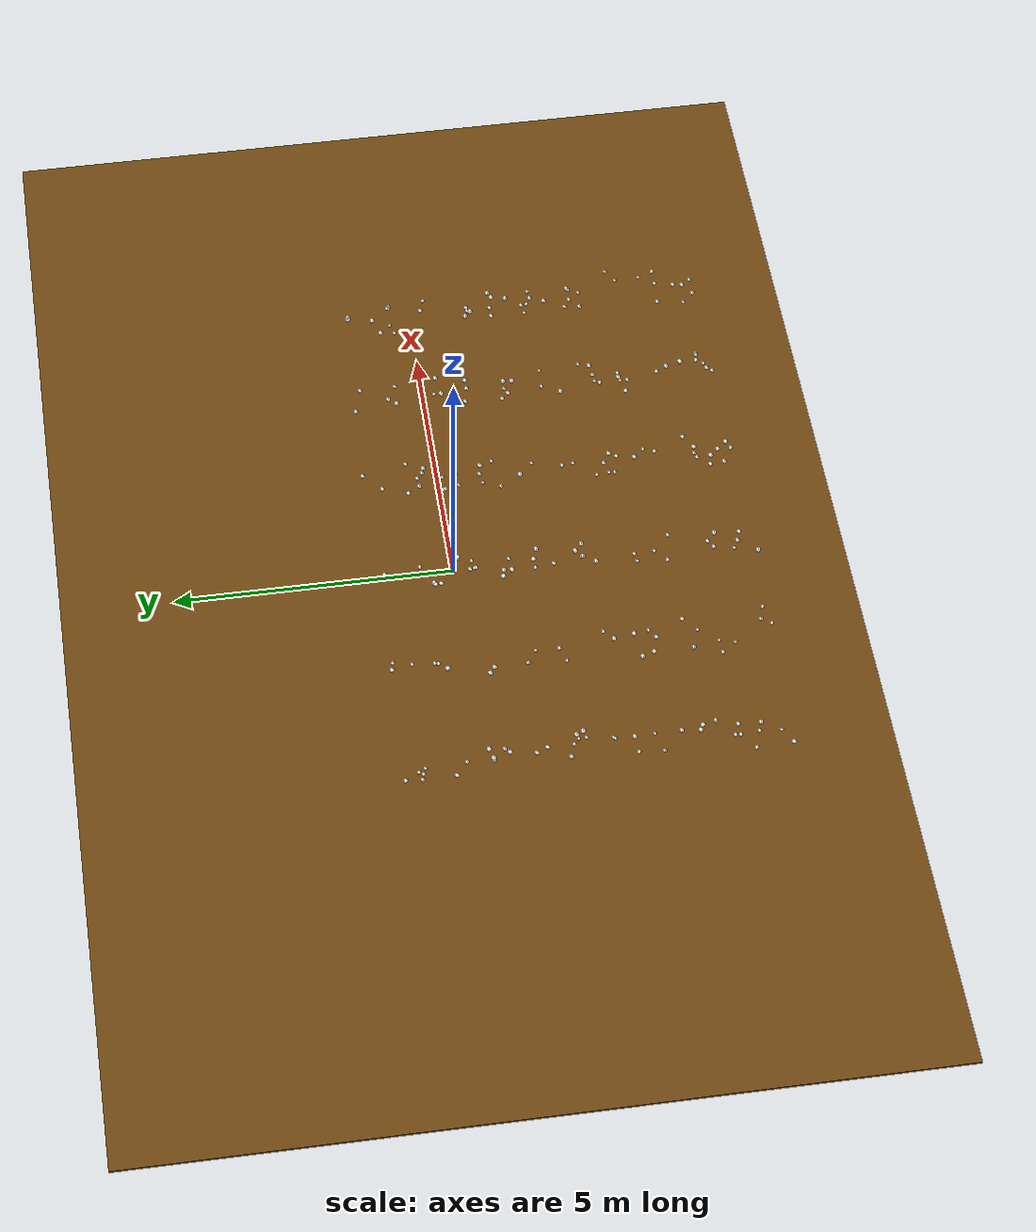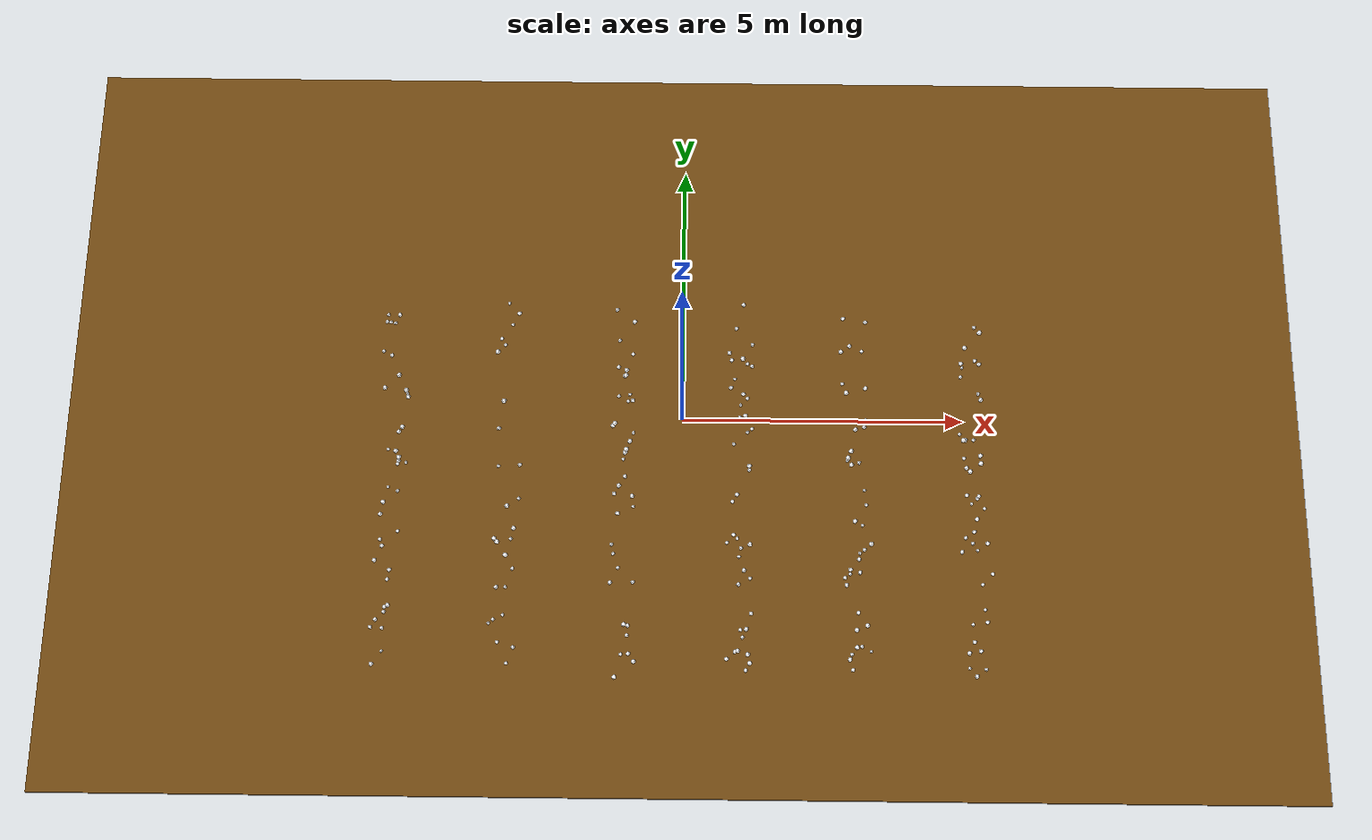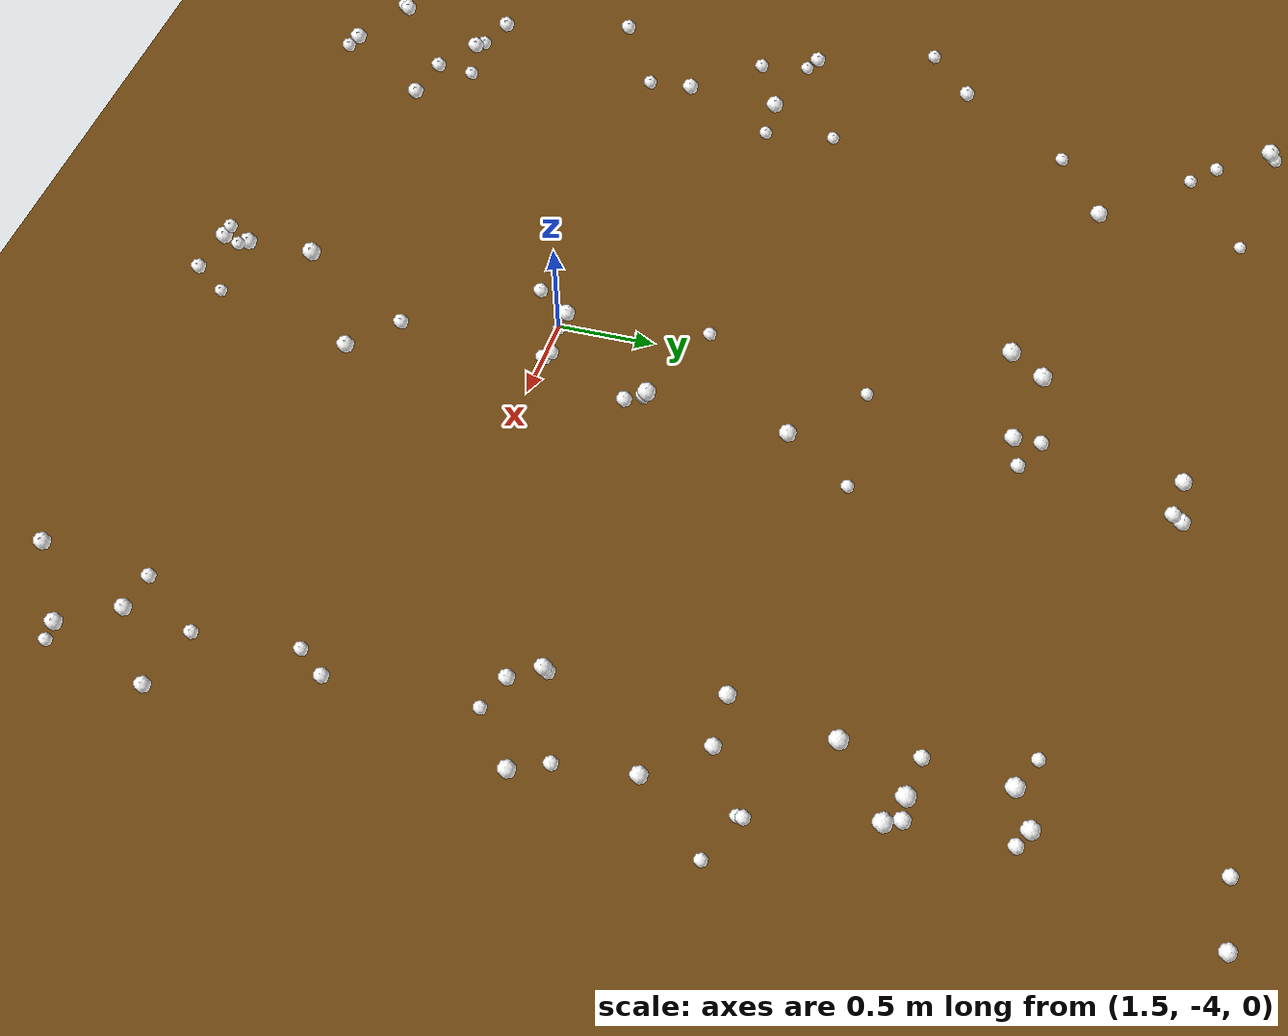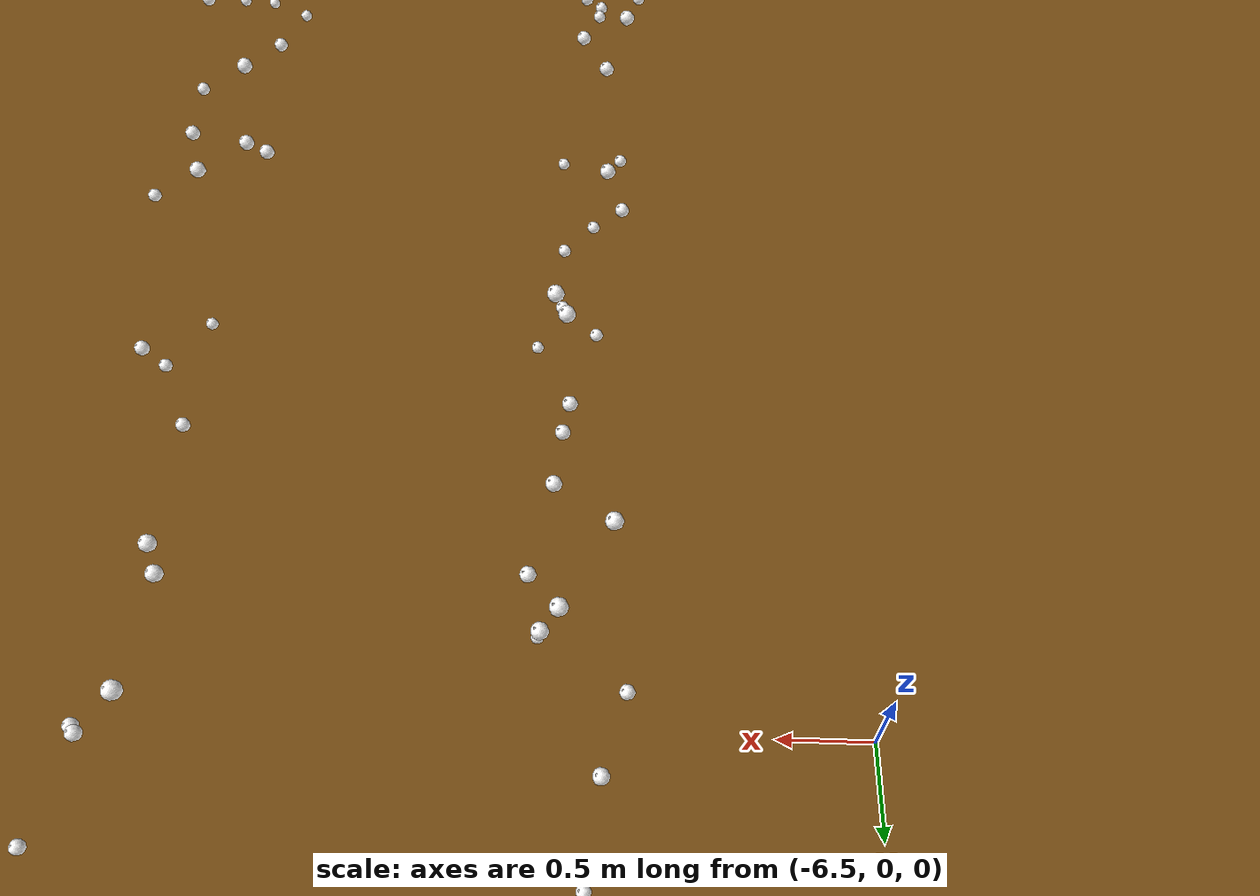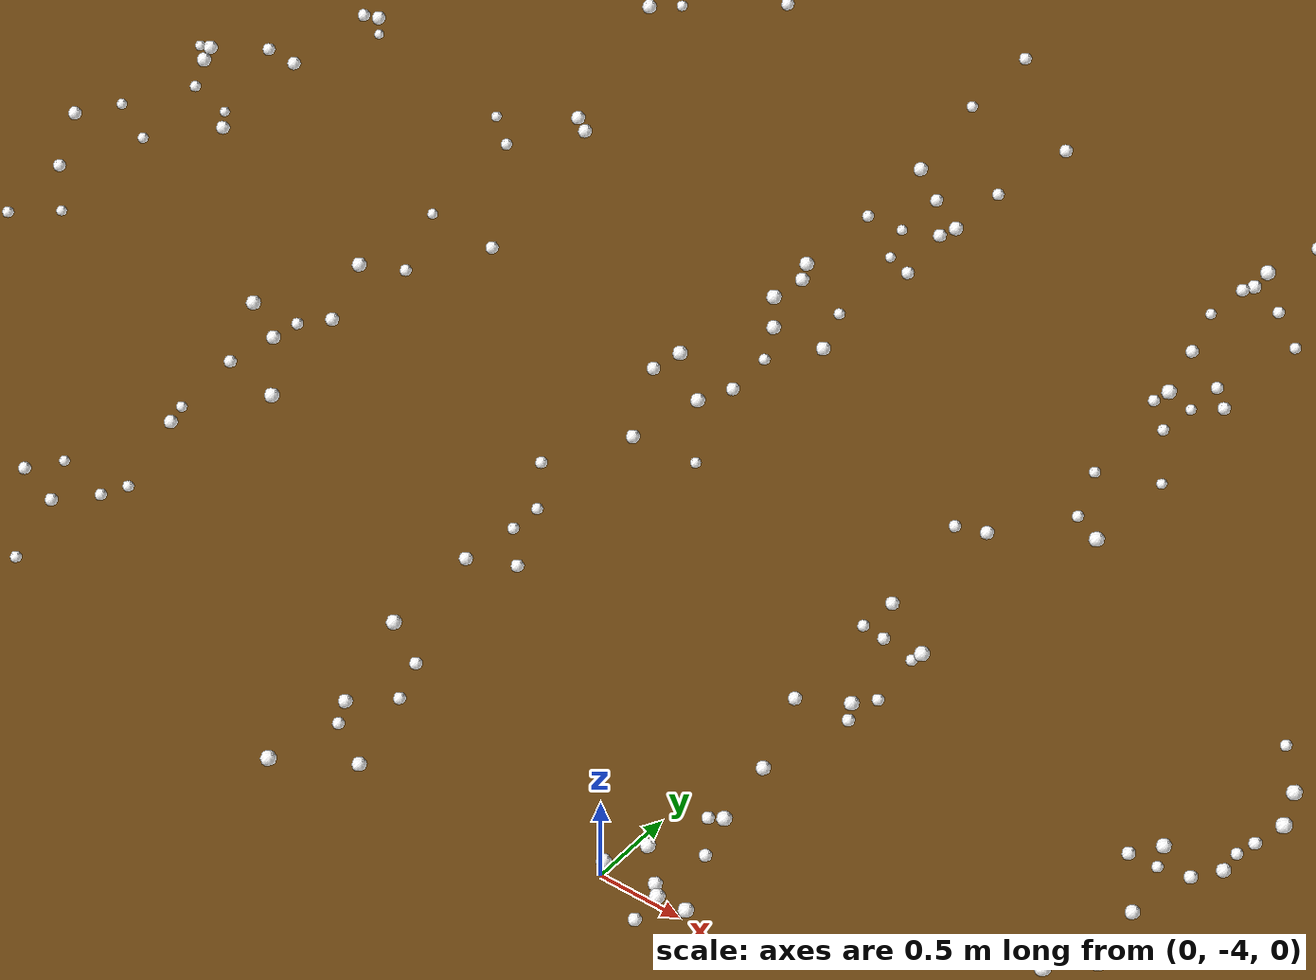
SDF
<sdf version="1.10">
 <world name="field">
  <gravity>0 0 -9.81</gravity>
  <physics name="default_physics" type="ode">
   <max_step_size>0.001</max_step_size>
   <real_time_factor>1.0</real_time_factor>
   <real_time_update_rate>1000</real_time_update_rate>
  </physics>
  <plugin filename="gz-sim-physics-system" name="gz::sim::systems::Physics"/>
  <plugin filename="gz-sim-user-commands-system" name="gz::sim::systems::UserCommands"/>
  <plugin filename="gz-sim-scene-broadcaster-system" name="gz::sim::systems::SceneBroadcaster"/>
  <light name="sun" type="directional">
   <pose>0 0 10 0 0 0</pose>
   <diffuse>0.8 0.8 0.8 1</diffuse>
   <specular>0.2 0.2 0.2 1</specular>
   <direction>-0.5 0.1 -0.9</direction>
  </light>
  <model name="ground_plane">
   <static>true</static>
   <pose>0 0 -0.025 0 0 0</pose>
   <link name="ground_link">
    <collision name="collision"><geometry><box><size>22 14 0.05</size></box></geometry></collision>
    <visual name="visual">
     <geometry><box><size>22 14 0.05</size></box></geometry>
     <material><ambient>0.45 0.29 0.07 1</ambient><diffuse>0.45 0.29 0.07 1</diffuse></material>
    </visual>
   </link>
  </model>
  <model name="tomato_0_fruit_0">
   <static>true</static>
   <pose>-4.9923227652214948 -4.8511804973645578 1.1925205228583835 0 0 0</pose>
   <link name="fruit_link">
    <collision name="fruit_collision">
     <geometry><sphere><radius>0.030375161328340002</radius></sphere></geometry>
    </collision>
    <visual name="fruit_visual">
     <geometry>
      <mesh>
       <uri>model://tomato_fruit/meshes/fruit.dae</uri>
       <scale>0.060750322656680004 0.060750322656680004 0.060750322656680004</scale>
      </mesh>
     </geometry>
     <material>
      <ambient>1 1 1 1</ambient>
      <diffuse>1 1 1 1</diffuse>
      <pbr>
       <metal>
        <albedo_map>model://tomato_0/materials/textures/AG15frt1.png</albedo_map>
        <metalness>0</metalness>
        <roughness>0.4</roughness>
       </metal>
      </pbr>
     </material>
    </visual>
   </link>
  </model>
  <model name="tomato_0_fruit_1">
   <static>true</static>
   <pose>-5.1706093909267485 -5.0382740260796099 1.0608571828405913 0 0 0</pose>
   <link name="fruit_link">
    <collision name="fruit_collision">
     <geometry><sphere><radius>0.043382693515572682</radius></sphere></geometry>
    </collision>
    <visual name="fruit_visual">
     <geometry>
      <mesh>
       <uri>model://tomato_fruit/meshes/fruit.dae</uri>
       <scale>0.086765387031145363 0.086765387031145363 0.086765387031145363</scale>
      </mesh>
     </geometry>
     <material>
      <ambient>1 1 1 1</ambient>
      <diffuse>1 1 1 1</diffuse>
      <pbr>
       <metal>
        <albedo_map>model://tomato_0/materials/textures/AG15frt1.png</albedo_map>
        <metalness>0</metalness>
        <roughness>0.4</roughness>
       </metal>
      </pbr>
     </material>
    </visual>
   </link>
  </model>
  <model name="tomato_1_fruit_0">
   <static>true</static>
   <pose>-4.9131462044349368 -4.105422017756287 1.3928715440570292 0 0 0</pose>
   <link name="fruit_link">
    <collision name="fruit_collision">
     <geometry><sphere><radius>0.0390302809357497</radius></sphere></geometry>
    </collision>
    <visual name="fruit_visual">
     <geometry>
      <mesh>
       <uri>model://tomato_fruit/meshes/fruit.dae</uri>
       <scale>0.078060561871499401 0.078060561871499401 0.078060561871499401</scale>
      </mesh>
     </geometry>
     <material>
      <ambient>1 1 1 1</ambient>
      <diffuse>1 1 1 1</diffuse>
      <pbr>
       <metal>
        <albedo_map>model://tomato_0/materials/textures/AG15frt1.png</albedo_map>
        <metalness>0</metalness>
        <roughness>0.4</roughness>
       </metal>
      </pbr>
     </material>
    </visual>
   </link>
  </model>
  <model name="tomato_1_fruit_1">
   <static>true</static>
   <pose>-4.9863398340146672 -4.0673917168700964 1.1947334957614639 0 0 0</pose>
   <link name="fruit_link">
    <collision name="fruit_collision">
     <geometry><sphere><radius>0.036738135694257802</radius></sphere></geometry>
    </collision>
    <visual name="fruit_visual">
     <geometry>
      <mesh>
       <uri>model://tomato_fruit/meshes/fruit.dae</uri>
       <scale>0.073476271388515604 0.073476271388515604 0.073476271388515604</scale>
      </mesh>
     </geometry>
     <material>
      <ambient>1 1 1 1</ambient>
      <diffuse>1 1 1 1</diffuse>
      <pbr>
       <metal>
        <albedo_map>model://tomato_0/materials/textures/AG15frt1.png</albedo_map>
        <metalness>0</metalness>
        <roughness>0.4</roughness>
       </metal>
      </pbr>
     </material>
    </visual>
   </link>
  </model>
  <model name="tomato_1_fruit_2">
   <static>true</static>
   <pose>-4.9956776725499976 -4.1520723449244326 1.1945099391701492 0 0 0</pose>
   <link name="fruit_link">
    <collision name="fruit_collision">
     <geometry><sphere><radius>0.036339215972302538</radius></sphere></geometry>
    </collision>
    <visual name="fruit_visual">
     <geometry>
      <mesh>
       <uri>model://tomato_fruit/meshes/fruit.dae</uri>
       <scale>0.072678431944605076 0.072678431944605076 0.072678431944605076</scale>
      </mesh>
     </geometry>
     <material>
      <ambient>1 1 1 1</ambient>
      <diffuse>1 1 1 1</diffuse>
      <pbr>
       <metal>
        <albedo_map>model://tomato_0/materials/textures/AG15frt1.png</albedo_map>
        <metalness>0</metalness>
        <roughness>0.4</roughness>
       </metal>
      </pbr>
     </material>
    </visual>
   </link>
  </model>
  <model name="tomato_1_fruit_3">
   <static>true</static>
   <pose>-5.0037485232025567 -4.464671584448209 1.2512855663392399 0 0 0</pose>
   <link name="fruit_link">
    <collision name="fruit_collision">
     <geometry><sphere><radius>0.035698909509560062</radius></sphere></geometry>
    </collision>
    <visual name="fruit_visual">
     <geometry>
      <mesh>
       <uri>model://tomato_fruit/meshes/fruit.dae</uri>
       <scale>0.071397819019120123 0.071397819019120123 0.071397819019120123</scale>
      </mesh>
     </geometry>
     <material>
      <ambient>1 1 1 1</ambient>
      <diffuse>1 1 1 1</diffuse>
      <pbr>
       <metal>
        <albedo_map>model://tomato_0/materials/textures/AG15frt1.png</albedo_map>
        <metalness>0</metalness>
        <roughness>0.4</roughness>
       </metal>
      </pbr>
     </material>
    </visual>
   </link>
  </model>
  <model name="tomato_1_fruit_4">
   <static>true</static>
   <pose>-5.2226854249807886 -4.3892325223143178 1.0873783139972466 0 0 0</pose>
   <link name="fruit_link">
    <collision name="fruit_collision">
     <geometry><sphere><radius>0.03689137319507764</radius></sphere></geometry>
    </collision>
    <visual name="fruit_visual">
     <geometry>
      <mesh>
       <uri>model://tomato_fruit/meshes/fruit.dae</uri>
       <scale>0.073782746390155279 0.073782746390155279 0.073782746390155279</scale>
      </mesh>
     </geometry>
     <material>
      <ambient>1 1 1 1</ambient>
      <diffuse>1 1 1 1</diffuse>
      <pbr>
       <metal>
        <albedo_map>model://tomato_0/materials/textures/AG15frt1.png</albedo_map>
        <metalness>0</metalness>
        <roughness>0.4</roughness>
       </metal>
      </pbr>
     </material>
    </visual>
   </link>
  </model>
  <model name="tomato_1_fruit_5">
   <static>true</static>
   <pose>-5.0766200595351263 -4.4483999982162787 1.6198162235557647 0 0 0</pose>
   <link name="fruit_link">
    <collision name="fruit_collision">
     <geometry><sphere><radius>0.039429596992416646</radius></sphere></geometry>
    </collision>
    <visual name="fruit_visual">
     <geometry>
      <mesh>
       <uri>model://tomato_fruit/meshes/fruit.dae</uri>
       <scale>0.078859193984833292 0.078859193984833292 0.078859193984833292</scale>
      </mesh>
     </geometry>
     <material>
      <ambient>1 1 1 1</ambient>
      <diffuse>1 1 1 1</diffuse>
      <pbr>
       <metal>
        <albedo_map>model://tomato_0/materials/textures/AG15frt1.png</albedo_map>
        <metalness>0</metalness>
        <roughness>0.4</roughness>
       </metal>
      </pbr>
     </material>
    </visual>
   </link>
  </model>
  <model name="tomato_2_fruit_0">
   <static>true</static>
   <pose>-5.1449928289222289 -3.4199264081481773 1.6896550644625303 0 0 0</pose>
   <link name="fruit_link">
    <collision name="fruit_collision">
     <geometry><sphere><radius>0.041596025111830373</radius></sphere></geometry>
    </collision>
    <visual name="fruit_visual">
     <geometry>
      <mesh>
       <uri>model://tomato_fruit/meshes/fruit.dae</uri>
       <scale>0.083192050223660746 0.083192050223660746 0.083192050223660746</scale>
      </mesh>
     </geometry>
     <material>
      <ambient>1 1 1 1</ambient>
      <diffuse>1 1 1 1</diffuse>
      <pbr>
       <metal>
        <albedo_map>model://tomato_0/materials/textures/AG15frt1.png</albedo_map>
        <metalness>0</metalness>
        <roughness>0.4</roughness>
       </metal>
      </pbr>
     </material>
    </visual>
   </link>
  </model>
  <model name="tomato_2_fruit_1">
   <static>true</static>
   <pose>-4.9194387642272552 -3.7158956751866703 1.5838772986485252 0 0 0</pose>
   <link name="fruit_link">
    <collision name="fruit_collision">
     <geometry><sphere><radius>0.036801154535526528</radius></sphere></geometry>
    </collision>
    <visual name="fruit_visual">
     <geometry>
      <mesh>
       <uri>model://tomato_fruit/meshes/fruit.dae</uri>
       <scale>0.073602309071053057 0.073602309071053057 0.073602309071053057</scale>
      </mesh>
     </geometry>
     <material>
      <ambient>1 1 1 1</ambient>
      <diffuse>1 1 1 1</diffuse>
      <pbr>
       <metal>
        <albedo_map>model://tomato_0/materials/textures/AG15frt1.png</albedo_map>
        <metalness>0</metalness>
        <roughness>0.4</roughness>
       </metal>
      </pbr>
     </material>
    </visual>
   </link>
  </model>
  <model name="tomato_2_fruit_2">
   <static>true</static>
   <pose>-4.909382587202856 -3.5077915167822113 1.4784833658756671 0 0 0</pose>
   <link name="fruit_link">
    <collision name="fruit_collision">
     <geometry><sphere><radius>0.040527304701878271</radius></sphere></geometry>
    </collision>
    <visual name="fruit_visual">
     <geometry>
      <mesh>
       <uri>model://tomato_fruit/meshes/fruit.dae</uri>
       <scale>0.081054609403756542 0.081054609403756542 0.081054609403756542</scale>
      </mesh>
     </geometry>
     <material>
      <ambient>1 1 1 1</ambient>
      <diffuse>1 1 1 1</diffuse>
      <pbr>
       <metal>
        <albedo_map>model://tomato_0/materials/textures/AG15frt1.png</albedo_map>
        <metalness>0</metalness>
        <roughness>0.4</roughness>
       </metal>
      </pbr>
     </material>
    </visual>
   </link>
  </model>
  <model name="tomato_3_fruit_0">
   <static>true</static>
   <pose>-4.8291444018805469 -2.7193643519963557 1.2656188092303533 0 0 0</pose>
   <link name="fruit_link">
    <collision name="fruit_collision">
     <geometry><sphere><radius>0.032451037406428927</radius></sphere></geometry>
    </collision>
    <visual name="fruit_visual">
     <geometry>
      <mesh>
       <uri>model://tomato_fruit/meshes/fruit.dae</uri>
       <scale>0.064902074812857855 0.064902074812857855 0.064902074812857855</scale>
      </mesh>
     </geometry>
     <material>
      <ambient>1 1 1 1</ambient>
      <diffuse>1 1 1 1</diffuse>
      <pbr>
       <metal>
        <albedo_map>model://tomato_0/materials/textures/AG15frt1.png</albedo_map>
        <metalness>0</metalness>
        <roughness>0.4</roughness>
       </metal>
      </pbr>
     </material>
    </visual>
   </link>
  </model>
  <model name="tomato_3_fruit_1">
   <static>true</static>
   <pose>-5.0434650302201645 -3.1165612164450671 1.5899963441328668 0 0 0</pose>
   <link name="fruit_link">
    <collision name="fruit_collision">
     <geometry><sphere><radius>0.040269213764848114</radius></sphere></geometry>
    </collision>
    <visual name="fruit_visual">
     <geometry>
      <mesh>
       <uri>model://tomato_fruit/meshes/fruit.dae</uri>
       <scale>0.080538427529696227 0.080538427529696227 0.080538427529696227</scale>
      </mesh>
     </geometry>
     <material>
      <ambient>1 1 1 1</ambient>
      <diffuse>1 1 1 1</diffuse>
      <pbr>
       <metal>
        <albedo_map>model://tomato_0/materials/textures/AG15frt1.png</albedo_map>
        <metalness>0</metalness>
        <roughness>0.4</roughness>
       </metal>
      </pbr>
     </material>
    </visual>
   </link>
  </model>
  <model name="tomato_3_fruit_2">
   <static>true</static>
   <pose>-5.1343040280017975 -2.8391939531687087 1.187418613182992 0 0 0</pose>
   <link name="fruit_link">
    <collision name="fruit_collision">
     <geometry><sphere><radius>0.034731795720886229</radius></sphere></geometry>
    </collision>
    <visual name="fruit_visual">
     <geometry>
      <mesh>
       <uri>model://tomato_fruit/meshes/fruit.dae</uri>
       <scale>0.069463591441772457 0.069463591441772457 0.069463591441772457</scale>
      </mesh>
     </geometry>
     <material>
      <ambient>1 1 1 1</ambient>
      <diffuse>1 1 1 1</diffuse>
      <pbr>
       <metal>
        <albedo_map>model://tomato_0/materials/textures/AG15frt4.png</albedo_map>
        <metalness>0</metalness>
        <roughness>0.4</roughness>
       </metal>
      </pbr>
     </material>
    </visual>
   </link>
  </model>
  <model name="tomato_4_fruit_0">
   <static>true</static>
   <pose>-4.8641260055081057 -2.0082517316873232 1.349461881644594 0 0 0</pose>
   <link name="fruit_link">
    <collision name="fruit_collision">
     <geometry><sphere><radius>0.033189398160812109</radius></sphere></geometry>
    </collision>
    <visual name="fruit_visual">
     <geometry>
      <mesh>
       <uri>model://tomato_fruit/meshes/fruit.dae</uri>
       <scale>0.066378796321624217 0.066378796321624217 0.066378796321624217</scale>
      </mesh>
     </geometry>
     <material>
      <ambient>1 1 1 1</ambient>
      <diffuse>1 1 1 1</diffuse>
      <pbr>
       <metal>
        <albedo_map>model://tomato_0/materials/textures/AG15frt1.png</albedo_map>
        <metalness>0</metalness>
        <roughness>0.4</roughness>
       </metal>
      </pbr>
     </material>
    </visual>
   </link>
  </model>
  <model name="tomato_4_fruit_1">
   <static>true</static>
   <pose>-5.0072189531927478 -2.0100700936667599 1.5214922874641246 0 0 0</pose>
   <link name="fruit_link">
    <collision name="fruit_collision">
     <geometry><sphere><radius>0.032094454792882594</radius></sphere></geometry>
    </collision>
    <visual name="fruit_visual">
     <geometry>
      <mesh>
       <uri>model://tomato_fruit/meshes/fruit.dae</uri>
       <scale>0.064188909585765189 0.064188909585765189 0.064188909585765189</scale>
      </mesh>
     </geometry>
     <material>
      <ambient>1 1 1 1</ambient>
      <diffuse>1 1 1 1</diffuse>
      <pbr>
       <metal>
        <albedo_map>model://tomato_0/materials/textures/AG15frt1.png</albedo_map>
        <metalness>0</metalness>
        <roughness>0.4</roughness>
       </metal>
      </pbr>
     </material>
    </visual>
   </link>
  </model>
  <model name="tomato_4_fruit_2">
   <static>true</static>
   <pose>-5.1500665312151206 -2.3995152441245717 1.2533975105995276 0 0 0</pose>
   <link name="fruit_link">
    <collision name="fruit_collision">
     <geometry><sphere><radius>0.038752993874184842</radius></sphere></geometry>
    </collision>
    <visual name="fruit_visual">
     <geometry>
      <mesh>
       <uri>model://tomato_fruit/meshes/fruit.dae</uri>
       <scale>0.077505987748369684 0.077505987748369684 0.077505987748369684</scale>
      </mesh>
     </geometry>
     <material>
      <ambient>1 1 1 1</ambient>
      <diffuse>1 1 1 1</diffuse>
      <pbr>
       <metal>
        <albedo_map>model://tomato_0/materials/textures/AG15frt1.png</albedo_map>
        <metalness>0</metalness>
        <roughness>0.4</roughness>
       </metal>
      </pbr>
     </material>
    </visual>
   </link>
  </model>
  <model name="tomato_4_fruit_3">
   <static>true</static>
   <pose>-5.068140223576032 -2.3221488887345529 1.602772036766666 0 0 0</pose>
   <link name="fruit_link">
    <collision name="fruit_collision">
     <geometry><sphere><radius>0.041336732363006064</radius></sphere></geometry>
    </collision>
    <visual name="fruit_visual">
     <geometry>
      <mesh>
       <uri>model://tomato_fruit/meshes/fruit.dae</uri>
       <scale>0.082673464726012127 0.082673464726012127 0.082673464726012127</scale>
      </mesh>
     </geometry>
     <material>
      <ambient>1 1 1 1</ambient>
      <diffuse>1 1 1 1</diffuse>
      <pbr>
       <metal>
        <albedo_map>model://tomato_0/materials/textures/AG15frt1.png</albedo_map>
        <metalness>0</metalness>
        <roughness>0.4</roughness>
       </metal>
      </pbr>
     </material>
    </visual>
   </link>
  </model>
  <model name="tomato_5_fruit_0">
   <static>true</static>
   <pose>-4.7568118588389163 -1.4442535027772587 1.2671335005545756 0 0 0</pose>
   <link name="fruit_link">
    <collision name="fruit_collision">
     <geometry><sphere><radius>0.030952915592279355</radius></sphere></geometry>
    </collision>
    <visual name="fruit_visual">
     <geometry>
      <mesh>
       <uri>model://tomato_fruit/meshes/fruit.dae</uri>
       <scale>0.06190583118455871 0.06190583118455871 0.06190583118455871</scale>
      </mesh>
     </geometry>
     <material>
      <ambient>1 1 1 1</ambient>
      <diffuse>1 1 1 1</diffuse>
      <pbr>
       <metal>
        <albedo_map>model://tomato_0/materials/textures/AG15frt4.png</albedo_map>
        <metalness>0</metalness>
        <roughness>0.4</roughness>
       </metal>
      </pbr>
     </material>
    </visual>
   </link>
  </model>
  <model name="tomato_5_fruit_1">
   <static>true</static>
   <pose>-4.9194150094224538 -1.3020830602022744 1.0080367153599736 0 0 0</pose>
   <link name="fruit_link">
    <collision name="fruit_collision">
     <geometry><sphere><radius>0.042911695533517466</radius></sphere></geometry>
    </collision>
    <visual name="fruit_visual">
     <geometry>
      <mesh>
       <uri>model://tomato_fruit/meshes/fruit.dae</uri>
       <scale>0.085823391067034932 0.085823391067034932 0.085823391067034932</scale>
      </mesh>
     </geometry>
     <material>
      <ambient>1 1 1 1</ambient>
      <diffuse>1 1 1 1</diffuse>
      <pbr>
       <metal>
        <albedo_map>model://tomato_0/materials/textures/AG15frt1.png</albedo_map>
        <metalness>0</metalness>
        <roughness>0.4</roughness>
       </metal>
      </pbr>
     </material>
    </visual>
   </link>
  </model>
  <model name="tomato_5_fruit_2">
   <static>true</static>
   <pose>-4.8744778517855876 -1.5483210080758307 1.4486732590058655 0 0 0</pose>
   <link name="fruit_link">
    <collision name="fruit_collision">
     <geometry><sphere><radius>0.03400237784928814</radius></sphere></geometry>
    </collision>
    <visual name="fruit_visual">
     <geometry>
      <mesh>
       <uri>model://tomato_fruit/meshes/fruit.dae</uri>
       <scale>0.06800475569857628 0.06800475569857628 0.06800475569857628</scale>
      </mesh>
     </geometry>
     <material>
      <ambient>1 1 1 1</ambient>
      <diffuse>1 1 1 1</diffuse>
      <pbr>
       <metal>
        <albedo_map>model://tomato_0/materials/textures/AG15frt1.png</albedo_map>
        <metalness>0</metalness>
        <roughness>0.4</roughness>
       </metal>
      </pbr>
     </material>
    </visual>
   </link>
  </model>
  <model name="tomato_5_fruit_3">
   <static>true</static>
   <pose>-4.8459232247823198 -1.4928934672523417 1.6130970582647359 0 0 0</pose>
   <link name="fruit_link">
    <collision name="fruit_collision">
     <geometry><sphere><radius>0.044307238912816196</radius></sphere></geometry>
    </collision>
    <visual name="fruit_visual">
     <geometry>
      <mesh>
       <uri>model://tomato_fruit/meshes/fruit.dae</uri>
       <scale>0.088614477825632393 0.088614477825632393 0.088614477825632393</scale>
      </mesh>
     </geometry>
     <material>
      <ambient>1 1 1 1</ambient>
      <diffuse>1 1 1 1</diffuse>
      <pbr>
       <metal>
        <albedo_map>model://tomato_0/materials/textures/AG15frt1.png</albedo_map>
        <metalness>0</metalness>
        <roughness>0.4</roughness>
       </metal>
      </pbr>
     </material>
    </visual>
   </link>
  </model>
  <model name="tomato_5_fruit_4">
   <static>true</static>
   <pose>-4.9032236609100766 -1.3740988929896836 1.6093629988857368 0 0 0</pose>
   <link name="fruit_link">
    <collision name="fruit_collision">
     <geometry><sphere><radius>0.043689417590172308</radius></sphere></geometry>
    </collision>
    <visual name="fruit_visual">
     <geometry>
      <mesh>
       <uri>model://tomato_fruit/meshes/fruit.dae</uri>
       <scale>0.087378835180344616 0.087378835180344616 0.087378835180344616</scale>
      </mesh>
     </geometry>
     <material>
      <ambient>1 1 1 1</ambient>
      <diffuse>1 1 1 1</diffuse>
      <pbr>
       <metal>
        <albedo_map>model://tomato_0/materials/textures/AG15frt1.png</albedo_map>
        <metalness>0</metalness>
        <roughness>0.4</roughness>
       </metal>
      </pbr>
     </material>
    </visual>
   </link>
  </model>
  <model name="tomato_5_fruit_5">
   <static>true</static>
   <pose>-5.0419113624961724 -1.3145578904135016 1.5337575600526059 0 0 0</pose>
   <link name="fruit_link">
    <collision name="fruit_collision">
     <geometry><sphere><radius>0.032292589028244521</radius></sphere></geometry>
    </collision>
    <visual name="fruit_visual">
     <geometry>
      <mesh>
       <uri>model://tomato_fruit/meshes/fruit.dae</uri>
       <scale>0.064585178056489043 0.064585178056489043 0.064585178056489043</scale>
      </mesh>
     </geometry>
     <material>
      <ambient>1 1 1 1</ambient>
      <diffuse>1 1 1 1</diffuse>
      <pbr>
       <metal>
        <albedo_map>model://tomato_0/materials/textures/AG15frt1.png</albedo_map>
        <metalness>0</metalness>
        <roughness>0.4</roughness>
       </metal>
      </pbr>
     </material>
    </visual>
   </link>
  </model>
  <model name="tomato_6_fruit_0">
   <static>true</static>
   <pose>-4.9031105297827473 -0.89334986206577494 1.3420239956202635 0 0 0</pose>
   <link name="fruit_link">
    <collision name="fruit_collision">
     <geometry><sphere><radius>0.038984168766903436</radius></sphere></geometry>
    </collision>
    <visual name="fruit_visual">
     <geometry>
      <mesh>
       <uri>model://tomato_fruit/meshes/fruit.dae</uri>
       <scale>0.077968337533806872 0.077968337533806872 0.077968337533806872</scale>
      </mesh>
     </geometry>
     <material>
      <ambient>1 1 1 1</ambient>
      <diffuse>1 1 1 1</diffuse>
      <pbr>
       <metal>
        <albedo_map>model://tomato_0/materials/textures/AG15frt4.png</albedo_map>
        <metalness>0</metalness>
        <roughness>0.4</roughness>
       </metal>
      </pbr>
     </material>
    </visual>
   </link>
  </model>
  <model name="tomato_6_fruit_1">
   <static>true</static>
   <pose>-4.8684878209060454 -0.72516509082837299 1.1676166172366411 0 0 0</pose>
   <link name="fruit_link">
    <collision name="fruit_collision">
     <geometry><sphere><radius>0.042101622071956932</radius></sphere></geometry>
    </collision>
    <visual name="fruit_visual">
     <geometry>
      <mesh>
       <uri>model://tomato_fruit/meshes/fruit.dae</uri>
       <scale>0.084203244143913863 0.084203244143913863 0.084203244143913863</scale>
      </mesh>
     </geometry>
     <material>
      <ambient>1 1 1 1</ambient>
      <diffuse>1 1 1 1</diffuse>
      <pbr>
       <metal>
        <albedo_map>model://tomato_0/materials/textures/AG15frt1.png</albedo_map>
        <metalness>0</metalness>
        <roughness>0.4</roughness>
       </metal>
      </pbr>
     </material>
    </visual>
   </link>
  </model>
  <model name="tomato_7_fruit_0">
   <static>true</static>
   <pose>-5.1458341420277272 -0.22061777478458078 1.684589145574134 0 0 0</pose>
   <link name="fruit_link">
    <collision name="fruit_collision">
     <geometry><sphere><radius>0.042240348801301328</radius></sphere></geometry>
    </collision>
    <visual name="fruit_visual">
     <geometry>
      <mesh>
       <uri>model://tomato_fruit/meshes/fruit.dae</uri>
       <scale>0.084480697602602656 0.084480697602602656 0.084480697602602656</scale>
      </mesh>
     </geometry>
     <material>
      <ambient>1 1 1 1</ambient>
      <diffuse>1 1 1 1</diffuse>
      <pbr>
       <metal>
        <albedo_map>model://tomato_0/materials/textures/AG15frt1.png</albedo_map>
        <metalness>0</metalness>
        <roughness>0.4</roughness>
       </metal>
      </pbr>
     </material>
    </visual>
   </link>
  </model>
  <model name="tomato_7_fruit_1">
   <static>true</static>
   <pose>-4.841282056055471 0.0018708305436815065 1.1155888712818893 0 0 0</pose>
   <link name="fruit_link">
    <collision name="fruit_collision">
     <geometry><sphere><radius>0.044202730195574857</radius></sphere></geometry>
    </collision>
    <visual name="fruit_visual">
     <geometry>
      <mesh>
       <uri>model://tomato_fruit/meshes/fruit.dae</uri>
       <scale>0.088405460391149715 0.088405460391149715 0.088405460391149715</scale>
      </mesh>
     </geometry>
     <material>
      <ambient>1 1 1 1</ambient>
      <diffuse>1 1 1 1</diffuse>
      <pbr>
       <metal>
        <albedo_map>model://tomato_0/materials/textures/AG15frt4.png</albedo_map>
        <metalness>0</metalness>
        <roughness>0.4</roughness>
       </metal>
      </pbr>
     </material>
    </visual>
   </link>
  </model>
  <model name="tomato_7_fruit_2">
   <static>true</static>
   <pose>-4.9316703402184432 0.098237057402448258 1.5286856376450637 0 0 0</pose>
   <link name="fruit_link">
    <collision name="fruit_collision">
     <geometry><sphere><radius>0.043933702395032651</radius></sphere></geometry>
    </collision>
    <visual name="fruit_visual">
     <geometry>
      <mesh>
       <uri>model://tomato_fruit/meshes/fruit.dae</uri>
       <scale>0.087867404790065301 0.087867404790065301 0.087867404790065301</scale>
      </mesh>
     </geometry>
     <material>
      <ambient>1 1 1 1</ambient>
      <diffuse>1 1 1 1</diffuse>
      <pbr>
       <metal>
        <albedo_map>model://tomato_0/materials/textures/AG15frt1.png</albedo_map>
        <metalness>0</metalness>
        <roughness>0.4</roughness>
       </metal>
      </pbr>
     </material>
    </visual>
   </link>
  </model>
  <model name="tomato_7_fruit_3">
   <static>true</static>
   <pose>-4.7821215428731083 -0.19313538711269645 1.2613943517705057 0 0 0</pose>
   <link name="fruit_link">
    <collision name="fruit_collision">
     <geometry><sphere><radius>0.04007530439457424</radius></sphere></geometry>
    </collision>
    <visual name="fruit_visual">
     <geometry>
      <mesh>
       <uri>model://tomato_fruit/meshes/fruit.dae</uri>
       <scale>0.080150608789148481 0.080150608789148481 0.080150608789148481</scale>
      </mesh>
     </geometry>
     <material>
      <ambient>1 1 1 1</ambient>
      <diffuse>1 1 1 1</diffuse>
      <pbr>
       <metal>
        <albedo_map>model://tomato_0/materials/textures/AG15frt1.png</albedo_map>
        <metalness>0</metalness>
        <roughness>0.4</roughness>
       </metal>
      </pbr>
     </material>
    </visual>
   </link>
  </model>
  <model name="tomato_7_fruit_4">
   <static>true</static>
   <pose>-4.8276561324068199 -0.015351587147463708 1.0147239820049412 0 0 0</pose>
   <link name="fruit_link">
    <collision name="fruit_collision">
     <geometry><sphere><radius>0.030960388444895171</radius></sphere></geometry>
    </collision>
    <visual name="fruit_visual">
     <geometry>
      <mesh>
       <uri>model://tomato_fruit/meshes/fruit.dae</uri>
       <scale>0.061920776889790342 0.061920776889790342 0.061920776889790342</scale>
      </mesh>
     </geometry>
     <material>
      <ambient>1 1 1 1</ambient>
      <diffuse>1 1 1 1</diffuse>
      <pbr>
       <metal>
        <albedo_map>model://tomato_0/materials/textures/AG15frt1.png</albedo_map>
        <metalness>0</metalness>
        <roughness>0.4</roughness>
       </metal>
      </pbr>
     </material>
    </visual>
   </link>
  </model>
  <model name="tomato_8_fruit_0">
   <static>true</static>
   <pose>-5.2109948184963049 0.50413313858912778 1.6337940091042895 0 0 0</pose>
   <link name="fruit_link">
    <collision name="fruit_collision">
     <geometry><sphere><radius>0.033434126757167316</radius></sphere></geometry>
    </collision>
    <visual name="fruit_visual">
     <geometry>
      <mesh>
       <uri>model://tomato_fruit/meshes/fruit.dae</uri>
       <scale>0.066868253514334633 0.066868253514334633 0.066868253514334633</scale>
      </mesh>
     </geometry>
     <material>
      <ambient>1 1 1 1</ambient>
      <diffuse>1 1 1 1</diffuse>
      <pbr>
       <metal>
        <albedo_map>model://tomato_0/materials/textures/AG15frt1.png</albedo_map>
        <metalness>0</metalness>
        <roughness>0.4</roughness>
       </metal>
      </pbr>
     </material>
    </visual>
   </link>
  </model>
  <model name="tomato_8_fruit_1">
   <static>true</static>
   <pose>-5.125056313327474 0.65643497820458185 1.1499657651593069 0 0 0</pose>
   <link name="fruit_link">
    <collision name="fruit_collision">
     <geometry><sphere><radius>0.040034666674444205</radius></sphere></geometry>
    </collision>
    <visual name="fruit_visual">
     <geometry>
      <mesh>
       <uri>model://tomato_fruit/meshes/fruit.dae</uri>
       <scale>0.080069333348888411 0.080069333348888411 0.080069333348888411</scale>
      </mesh>
     </geometry>
     <material>
      <ambient>1 1 1 1</ambient>
      <diffuse>1 1 1 1</diffuse>
      <pbr>
       <metal>
        <albedo_map>model://tomato_0/materials/textures/AG15frt1.png</albedo_map>
        <metalness>0</metalness>
        <roughness>0.4</roughness>
       </metal>
      </pbr>
     </material>
    </visual>
   </link>
  </model>
  <model name="tomato_9_fruit_0">
   <static>true</static>
   <pose>-5.1533917795622202 1.2201781622108596 1.3310810600612155 0 0 0</pose>
   <link name="fruit_link">
    <collision name="fruit_collision">
     <geometry><sphere><radius>0.033644958635935869</radius></sphere></geometry>
    </collision>
    <visual name="fruit_visual">
     <geometry>
      <mesh>
       <uri>model://tomato_fruit/meshes/fruit.dae</uri>
       <scale>0.067289917271871738 0.067289917271871738 0.067289917271871738</scale>
      </mesh>
     </geometry>
     <material>
      <ambient>1 1 1 1</ambient>
      <diffuse>1 1 1 1</diffuse>
      <pbr>
       <metal>
        <albedo_map>model://tomato_0/materials/textures/AG15frt1.png</albedo_map>
        <metalness>0</metalness>
        <roughness>0.4</roughness>
       </metal>
      </pbr>
     </material>
    </visual>
   </link>
  </model>
  <model name="tomato_9_fruit_1">
   <static>true</static>
   <pose>-5.2263122283842547 1.2476025075669157 1.2877715932348166 0 0 0</pose>
   <link name="fruit_link">
    <collision name="fruit_collision">
     <geometry><sphere><radius>0.035314463498843304</radius></sphere></geometry>
    </collision>
    <visual name="fruit_visual">
     <geometry>
      <mesh>
       <uri>model://tomato_fruit/meshes/fruit.dae</uri>
       <scale>0.070628926997686609 0.070628926997686609 0.070628926997686609</scale>
      </mesh>
     </geometry>
     <material>
      <ambient>1 1 1 1</ambient>
      <diffuse>1 1 1 1</diffuse>
      <pbr>
       <metal>
        <albedo_map>model://tomato_0/materials/textures/AG15frt1.png</albedo_map>
        <metalness>0</metalness>
        <roughness>0.4</roughness>
       </metal>
      </pbr>
     </material>
    </visual>
   </link>
  </model>
  <model name="tomato_9_fruit_2">
   <static>true</static>
   <pose>-5.0437062686383483 1.5101713873358478 1.0424288718539096 0 0 0</pose>
   <link name="fruit_link">
    <collision name="fruit_collision">
     <geometry><sphere><radius>0.039692696269424767</radius></sphere></geometry>
    </collision>
    <visual name="fruit_visual">
     <geometry>
      <mesh>
       <uri>model://tomato_fruit/meshes/fruit.dae</uri>
       <scale>0.079385392538849534 0.079385392538849534 0.079385392538849534</scale>
      </mesh>
     </geometry>
     <material>
      <ambient>1 1 1 1</ambient>
      <diffuse>1 1 1 1</diffuse>
      <pbr>
       <metal>
        <albedo_map>model://tomato_0/materials/textures/AG15frt1.png</albedo_map>
        <metalness>0</metalness>
        <roughness>0.4</roughness>
       </metal>
      </pbr>
     </material>
    </visual>
   </link>
  </model>
  <model name="tomato_9_fruit_3">
   <static>true</static>
   <pose>-5.0699668286299291 1.1807924761086608 1.3754000277372411 0 0 0</pose>
   <link name="fruit_link">
    <collision name="fruit_collision">
     <geometry><sphere><radius>0.032873851082124809</radius></sphere></geometry>
    </collision>
    <visual name="fruit_visual">
     <geometry>
      <mesh>
       <uri>model://tomato_fruit/meshes/fruit.dae</uri>
       <scale>0.065747702164249619 0.065747702164249619 0.065747702164249619</scale>
      </mesh>
     </geometry>
     <material>
      <ambient>1 1 1 1</ambient>
      <diffuse>1 1 1 1</diffuse>
      <pbr>
       <metal>
        <albedo_map>model://tomato_0/materials/textures/AG15frt1.png</albedo_map>
        <metalness>0</metalness>
        <roughness>0.4</roughness>
       </metal>
      </pbr>
     </material>
    </visual>
   </link>
  </model>
  <model name="tomato_9_fruit_4">
   <static>true</static>
   <pose>-5.1902379097761839 1.3038286082024917 1.4565014257989655 0 0 0</pose>
   <link name="fruit_link">
    <collision name="fruit_collision">
     <geometry><sphere><radius>0.031468630923024002</radius></sphere></geometry>
    </collision>
    <visual name="fruit_visual">
     <geometry>
      <mesh>
       <uri>model://tomato_fruit/meshes/fruit.dae</uri>
       <scale>0.062937261846048004 0.062937261846048004 0.062937261846048004</scale>
      </mesh>
     </geometry>
     <material>
      <ambient>1 1 1 1</ambient>
      <diffuse>1 1 1 1</diffuse>
      <pbr>
       <metal>
        <albedo_map>model://tomato_0/materials/textures/AG15frt1.png</albedo_map>
        <metalness>0</metalness>
        <roughness>0.4</roughness>
       </metal>
      </pbr>
     </material>
    </visual>
   </link>
  </model>
  <model name="tomato_10_fruit_0">
   <static>true</static>
   <pose>-2.8859547907057963 -5.093993253033493 1.339948787815503 0 0 0</pose>
   <link name="fruit_link">
    <collision name="fruit_collision">
     <geometry><sphere><radius>0.032494666659058709</radius></sphere></geometry>
    </collision>
    <visual name="fruit_visual">
     <geometry>
      <mesh>
       <uri>model://tomato_fruit/meshes/fruit.dae</uri>
       <scale>0.064989333318117418 0.064989333318117418 0.064989333318117418</scale>
      </mesh>
     </geometry>
     <material>
      <ambient>1 1 1 1</ambient>
      <diffuse>1 1 1 1</diffuse>
      <pbr>
       <metal>
        <albedo_map>model://tomato_0/materials/textures/AG15frt1.png</albedo_map>
        <metalness>0</metalness>
        <roughness>0.4</roughness>
       </metal>
      </pbr>
     </material>
    </visual>
   </link>
  </model>
  <model name="tomato_10_fruit_1">
   <static>true</static>
   <pose>-3.0225567903023252 -4.8471793580202354 1.6897161906458082 0 0 0</pose>
   <link name="fruit_link">
    <collision name="fruit_collision">
     <geometry><sphere><radius>0.035684596784653744</radius></sphere></geometry>
    </collision>
    <visual name="fruit_visual">
     <geometry>
      <mesh>
       <uri>model://tomato_fruit/meshes/fruit.dae</uri>
       <scale>0.071369193569307487 0.071369193569307487 0.071369193569307487</scale>
      </mesh>
     </geometry>
     <material>
      <ambient>1 1 1 1</ambient>
      <diffuse>1 1 1 1</diffuse>
      <pbr>
       <metal>
        <albedo_map>model://tomato_0/materials/textures/AG15frt1.png</albedo_map>
        <metalness>0</metalness>
        <roughness>0.4</roughness>
       </metal>
      </pbr>
     </material>
    </visual>
   </link>
  </model>
  <model name="tomato_10_fruit_2">
   <static>true</static>
   <pose>-2.7605072144238232 -4.9303865346435929 1.6701223486017711 0 0 0</pose>
   <link name="fruit_link">
    <collision name="fruit_collision">
     <geometry><sphere><radius>0.03634511228985244</radius></sphere></geometry>
    </collision>
    <visual name="fruit_visual">
     <geometry>
      <mesh>
       <uri>model://tomato_fruit/meshes/fruit.dae</uri>
       <scale>0.072690224579704879 0.072690224579704879 0.072690224579704879</scale>
      </mesh>
     </geometry>
     <material>
      <ambient>1 1 1 1</ambient>
      <diffuse>1 1 1 1</diffuse>
      <pbr>
       <metal>
        <albedo_map>model://tomato_0/materials/textures/AG15frt4.png</albedo_map>
        <metalness>0</metalness>
        <roughness>0.4</roughness>
       </metal>
      </pbr>
     </material>
    </visual>
   </link>
  </model>
  <model name="tomato_11_fruit_0">
   <static>true</static>
   <pose>-2.9887433725253825 -4.1728946498312158 1.1523906288899224 0 0 0</pose>
   <link name="fruit_link">
    <collision name="fruit_collision">
     <geometry><sphere><radius>0.032848468009014559</radius></sphere></geometry>
    </collision>
    <visual name="fruit_visual">
     <geometry>
      <mesh>
       <uri>model://tomato_fruit/meshes/fruit.dae</uri>
       <scale>0.065696936018029117 0.065696936018029117 0.065696936018029117</scale>
      </mesh>
     </geometry>
     <material>
      <ambient>1 1 1 1</ambient>
      <diffuse>1 1 1 1</diffuse>
      <pbr>
       <metal>
        <albedo_map>model://tomato_0/materials/textures/AG15frt1.png</albedo_map>
        <metalness>0</metalness>
        <roughness>0.4</roughness>
       </metal>
      </pbr>
     </material>
    </visual>
   </link>
  </model>
  <model name="tomato_11_fruit_1">
   <static>true</static>
   <pose>-3.1592470190541548 -4.211920377737199 1.0350996360847675 0 0 0</pose>
   <link name="fruit_link">
    <collision name="fruit_collision">
     <geometry><sphere><radius>0.034704072146545938</radius></sphere></geometry>
    </collision>
    <visual name="fruit_visual">
     <geometry>
      <mesh>
       <uri>model://tomato_fruit/meshes/fruit.dae</uri>
       <scale>0.069408144293091875 0.069408144293091875 0.069408144293091875</scale>
      </mesh>
     </geometry>
     <material>
      <ambient>1 1 1 1</ambient>
      <diffuse>1 1 1 1</diffuse>
      <pbr>
       <metal>
        <albedo_map>model://tomato_0/materials/textures/AG15frt1.png</albedo_map>
        <metalness>0</metalness>
        <roughness>0.4</roughness>
       </metal>
      </pbr>
     </material>
    </visual>
   </link>
  </model>
  <model name="tomato_11_fruit_2">
   <static>true</static>
   <pose>-3.2095001541892771 -4.3965423461397926 1.3554799478953929 0 0 0</pose>
   <link name="fruit_link">
    <collision name="fruit_collision">
     <geometry><sphere><radius>0.030853193695930266</radius></sphere></geometry>
    </collision>
    <visual name="fruit_visual">
     <geometry>
      <mesh>
       <uri>model://tomato_fruit/meshes/fruit.dae</uri>
       <scale>0.061706387391860532 0.061706387391860532 0.061706387391860532</scale>
      </mesh>
     </geometry>
     <material>
      <ambient>1 1 1 1</ambient>
      <diffuse>1 1 1 1</diffuse>
      <pbr>
       <metal>
        <albedo_map>model://tomato_0/materials/textures/AG15frt1.png</albedo_map>
        <metalness>0</metalness>
        <roughness>0.4</roughness>
       </metal>
      </pbr>
     </material>
    </visual>
   </link>
  </model>
  <model name="tomato_12_fruit_0">
   <static>true</static>
   <pose>-2.8199464934818756 -3.5276179178309901 1.6591172890603625 0 0 0</pose>
   <link name="fruit_link">
    <collision name="fruit_collision">
     <geometry><sphere><radius>0.036056633269774159</radius></sphere></geometry>
    </collision>
    <visual name="fruit_visual">
     <geometry>
      <mesh>
       <uri>model://tomato_fruit/meshes/fruit.dae</uri>
       <scale>0.072113266539548318 0.072113266539548318 0.072113266539548318</scale>
      </mesh>
     </geometry>
     <material>
      <ambient>1 1 1 1</ambient>
      <diffuse>1 1 1 1</diffuse>
      <pbr>
       <metal>
        <albedo_map>model://tomato_0/materials/textures/AG15frt1.png</albedo_map>
        <metalness>0</metalness>
        <roughness>0.4</roughness>
       </metal>
      </pbr>
     </material>
    </visual>
   </link>
  </model>
  <model name="tomato_12_fruit_1">
   <static>true</static>
   <pose>-2.9421979118968844 -3.7846435364960329 1.4601612151307657 0 0 0</pose>
   <link name="fruit_link">
    <collision name="fruit_collision">
     <geometry><sphere><radius>0.031229751082423131</radius></sphere></geometry>
    </collision>
    <visual name="fruit_visual">
     <geometry>
      <mesh>
       <uri>model://tomato_fruit/meshes/fruit.dae</uri>
       <scale>0.062459502164846262 0.062459502164846262 0.062459502164846262</scale>
      </mesh>
     </geometry>
     <material>
      <ambient>1 1 1 1</ambient>
      <diffuse>1 1 1 1</diffuse>
      <pbr>
       <metal>
        <albedo_map>model://tomato_0/materials/textures/AG15frt1.png</albedo_map>
        <metalness>0</metalness>
        <roughness>0.4</roughness>
       </metal>
      </pbr>
     </material>
    </visual>
   </link>
  </model>
  <model name="tomato_12_fruit_2">
   <static>true</static>
   <pose>-3.1173202710049353 -3.7005755431152307 1.2199287039569033 0 0 0</pose>
   <link name="fruit_link">
    <collision name="fruit_collision">
     <geometry><sphere><radius>0.04004588962154744</radius></sphere></geometry>
    </collision>
    <visual name="fruit_visual">
     <geometry>
      <mesh>
       <uri>model://tomato_fruit/meshes/fruit.dae</uri>
       <scale>0.080091779243094879 0.080091779243094879 0.080091779243094879</scale>
      </mesh>
     </geometry>
     <material>
      <ambient>1 1 1 1</ambient>
      <diffuse>1 1 1 1</diffuse>
      <pbr>
       <metal>
        <albedo_map>model://tomato_0/materials/textures/AG15frt1.png</albedo_map>
        <metalness>0</metalness>
        <roughness>0.4</roughness>
       </metal>
      </pbr>
     </material>
    </visual>
   </link>
  </model>
  <model name="tomato_13_fruit_0">
   <static>true</static>
   <pose>-2.8777379917909851 -2.9424768505113721 1.5263051446900815 0 0 0</pose>
   <link name="fruit_link">
    <collision name="fruit_collision">
     <geometry><sphere><radius>0.034742657944077812</radius></sphere></geometry>
    </collision>
    <visual name="fruit_visual">
     <geometry>
      <mesh>
       <uri>model://tomato_fruit/meshes/fruit.dae</uri>
       <scale>0.069485315888155624 0.069485315888155624 0.069485315888155624</scale>
      </mesh>
     </geometry>
     <material>
      <ambient>1 1 1 1</ambient>
      <diffuse>1 1 1 1</diffuse>
      <pbr>
       <metal>
        <albedo_map>model://tomato_0/materials/textures/AG15frt4.png</albedo_map>
        <metalness>0</metalness>
        <roughness>0.4</roughness>
       </metal>
      </pbr>
     </material>
    </visual>
   </link>
  </model>
  <model name="tomato_13_fruit_1">
   <static>true</static>
   <pose>-2.9965692958912582 -3.0476702145668271 1.0512825047697432 0 0 0</pose>
   <link name="fruit_link">
    <collision name="fruit_collision">
     <geometry><sphere><radius>0.044941446717826412</radius></sphere></geometry>
    </collision>
    <visual name="fruit_visual">
     <geometry>
      <mesh>
       <uri>model://tomato_fruit/meshes/fruit.dae</uri>
       <scale>0.089882893435652825 0.089882893435652825 0.089882893435652825</scale>
      </mesh>
     </geometry>
     <material>
      <ambient>1 1 1 1</ambient>
      <diffuse>1 1 1 1</diffuse>
      <pbr>
       <metal>
        <albedo_map>model://tomato_0/materials/textures/AG15frt4.png</albedo_map>
        <metalness>0</metalness>
        <roughness>0.4</roughness>
       </metal>
      </pbr>
     </material>
    </visual>
   </link>
  </model>
  <model name="tomato_13_fruit_2">
   <static>true</static>
   <pose>-3.1019516519414045 -3.0335769642806794 1.6154891697391798 0 0 0</pose>
   <link name="fruit_link">
    <collision name="fruit_collision">
     <geometry><sphere><radius>0.043212962605296591</radius></sphere></geometry>
    </collision>
    <visual name="fruit_visual">
     <geometry>
      <mesh>
       <uri>model://tomato_fruit/meshes/fruit.dae</uri>
       <scale>0.086425925210593182 0.086425925210593182 0.086425925210593182</scale>
      </mesh>
     </geometry>
     <material>
      <ambient>1 1 1 1</ambient>
      <diffuse>1 1 1 1</diffuse>
      <pbr>
       <metal>
        <albedo_map>model://tomato_0/materials/textures/AG15frt4.png</albedo_map>
        <metalness>0</metalness>
        <roughness>0.4</roughness>
       </metal>
      </pbr>
     </material>
    </visual>
   </link>
  </model>
  <model name="tomato_13_fruit_3">
   <static>true</static>
   <pose>-2.8446938798121821 -2.7062142606431512 1.428174436008165 0 0 0</pose>
   <link name="fruit_link">
    <collision name="fruit_collision">
     <geometry><sphere><radius>0.040553098876310562</radius></sphere></geometry>
    </collision>
    <visual name="fruit_visual">
     <geometry>
      <mesh>
       <uri>model://tomato_fruit/meshes/fruit.dae</uri>
       <scale>0.081106197752621123 0.081106197752621123 0.081106197752621123</scale>
      </mesh>
     </geometry>
     <material>
      <ambient>1 1 1 1</ambient>
      <diffuse>1 1 1 1</diffuse>
      <pbr>
       <metal>
        <albedo_map>model://tomato_0/materials/textures/AG15frt1.png</albedo_map>
        <metalness>0</metalness>
        <roughness>0.4</roughness>
       </metal>
      </pbr>
     </material>
    </visual>
   </link>
  </model>
  <model name="tomato_13_fruit_4">
   <static>true</static>
   <pose>-3.1851677320900524 -2.8091811229847696 1.2095651265399845 0 0 0</pose>
   <link name="fruit_link">
    <collision name="fruit_collision">
     <geometry><sphere><radius>0.04225656202673192</radius></sphere></geometry>
    </collision>
    <visual name="fruit_visual">
     <geometry>
      <mesh>
       <uri>model://tomato_fruit/meshes/fruit.dae</uri>
       <scale>0.084513124053463839 0.084513124053463839 0.084513124053463839</scale>
      </mesh>
     </geometry>
     <material>
      <ambient>1 1 1 1</ambient>
      <diffuse>1 1 1 1</diffuse>
      <pbr>
       <metal>
        <albedo_map>model://tomato_0/materials/textures/AG15frt1.png</albedo_map>
        <metalness>0</metalness>
        <roughness>0.4</roughness>
       </metal>
      </pbr>
     </material>
    </visual>
   </link>
  </model>
  <model name="tomato_14_fruit_0">
   <static>true</static>
   <pose>-2.9672849783050803 -2.336338089433303 1.5196916787866992 0 0 0</pose>
   <link name="fruit_link">
    <collision name="fruit_collision">
     <geometry><sphere><radius>0.043345690605085634</radius></sphere></geometry>
    </collision>
    <visual name="fruit_visual">
     <geometry>
      <mesh>
       <uri>model://tomato_fruit/meshes/fruit.dae</uri>
       <scale>0.086691381210171267 0.086691381210171267 0.086691381210171267</scale>
      </mesh>
     </geometry>
     <material>
      <ambient>1 1 1 1</ambient>
      <diffuse>1 1 1 1</diffuse>
      <pbr>
       <metal>
        <albedo_map>model://tomato_0/materials/textures/AG15frt1.png</albedo_map>
        <metalness>0</metalness>
        <roughness>0.4</roughness>
       </metal>
      </pbr>
     </material>
    </visual>
   </link>
  </model>
  <model name="tomato_14_fruit_1">
   <static>true</static>
   <pose>-2.7696860796134035 -2.1838613355405978 1.4812479901609312 0 0 0</pose>
   <link name="fruit_link">
    <collision name="fruit_collision">
     <geometry><sphere><radius>0.035143204316898879</radius></sphere></geometry>
    </collision>
    <visual name="fruit_visual">
     <geometry>
      <mesh>
       <uri>model://tomato_fruit/meshes/fruit.dae</uri>
       <scale>0.070286408633797759 0.070286408633797759 0.070286408633797759</scale>
      </mesh>
     </geometry>
     <material>
      <ambient>1 1 1 1</ambient>
      <diffuse>1 1 1 1</diffuse>
      <pbr>
       <metal>
        <albedo_map>model://tomato_0/materials/textures/AG15frt1.png</albedo_map>
        <metalness>0</metalness>
        <roughness>0.4</roughness>
       </metal>
      </pbr>
     </material>
    </visual>
   </link>
  </model>
  <model name="tomato_15_fruit_0">
   <static>true</static>
   <pose>-3.1558831812061263 -1.5051560351136457 1.2965030407946085 0 0 0</pose>
   <link name="fruit_link">
    <collision name="fruit_collision">
     <geometry><sphere><radius>0.031384477015690998</radius></sphere></geometry>
    </collision>
    <visual name="fruit_visual">
     <geometry>
      <mesh>
       <uri>model://tomato_fruit/meshes/fruit.dae</uri>
       <scale>0.062768954031381996 0.062768954031381996 0.062768954031381996</scale>
      </mesh>
     </geometry>
     <material>
      <ambient>1 1 1 1</ambient>
      <diffuse>1 1 1 1</diffuse>
      <pbr>
       <metal>
        <albedo_map>model://tomato_0/materials/textures/AG15frt4.png</albedo_map>
        <metalness>0</metalness>
        <roughness>0.4</roughness>
       </metal>
      </pbr>
     </material>
    </visual>
   </link>
  </model>
  <model name="tomato_15_fruit_1">
   <static>true</static>
   <pose>-2.7957032210317339 -1.4287645907639126 1.1833686837040438 0 0 0</pose>
   <link name="fruit_link">
    <collision name="fruit_collision">
     <geometry><sphere><radius>0.039556700659520695</radius></sphere></geometry>
    </collision>
    <visual name="fruit_visual">
     <geometry>
      <mesh>
       <uri>model://tomato_fruit/meshes/fruit.dae</uri>
       <scale>0.07911340131904139 0.07911340131904139 0.07911340131904139</scale>
      </mesh>
     </geometry>
     <material>
      <ambient>1 1 1 1</ambient>
      <diffuse>1 1 1 1</diffuse>
      <pbr>
       <metal>
        <albedo_map>model://tomato_0/materials/textures/AG15frt1.png</albedo_map>
        <metalness>0</metalness>
        <roughness>0.4</roughness>
       </metal>
      </pbr>
     </material>
    </visual>
   </link>
  </model>
  <model name="tomato_16_fruit_0">
   <static>true</static>
   <pose>-3.1353951196503518 -0.96030552414397885 1.6615356573326472 0 0 0</pose>
   <link name="fruit_link">
    <collision name="fruit_collision">
     <geometry><sphere><radius>0.031678108208840025</radius></sphere></geometry>
    </collision>
    <visual name="fruit_visual">
     <geometry>
      <mesh>
       <uri>model://tomato_fruit/meshes/fruit.dae</uri>
       <scale>0.06335621641768005 0.06335621641768005 0.06335621641768005</scale>
      </mesh>
     </geometry>
     <material>
      <ambient>1 1 1 1</ambient>
      <diffuse>1 1 1 1</diffuse>
      <pbr>
       <metal>
        <albedo_map>model://tomato_0/materials/textures/AG15frt1.png</albedo_map>
        <metalness>0</metalness>
        <roughness>0.4</roughness>
       </metal>
      </pbr>
     </material>
    </visual>
   </link>
  </model>
  <model name="tomato_16_fruit_1">
   <static>true</static>
   <pose>-3.1725143494639729 -0.83420315080100016 1.3867675677214983 0 0 0</pose>
   <link name="fruit_link">
    <collision name="fruit_collision">
     <geometry><sphere><radius>0.035538239767682875</radius></sphere></geometry>
    </collision>
    <visual name="fruit_visual">
     <geometry>
      <mesh>
       <uri>model://tomato_fruit/meshes/fruit.dae</uri>
       <scale>0.07107647953536575 0.07107647953536575 0.07107647953536575</scale>
      </mesh>
     </geometry>
     <material>
      <ambient>1 1 1 1</ambient>
      <diffuse>1 1 1 1</diffuse>
      <pbr>
       <metal>
        <albedo_map>model://tomato_0/materials/textures/AG15frt1.png</albedo_map>
        <metalness>0</metalness>
        <roughness>0.4</roughness>
       </metal>
      </pbr>
     </material>
    </visual>
   </link>
  </model>
  <model name="tomato_17_fruit_0">
   <static>true</static>
   <pose>-3.119740475090647 -0.19433889188775189 1.1470535768378278 0 0 0</pose>
   <link name="fruit_link">
    <collision name="fruit_collision">
     <geometry><sphere><radius>0.043483869547897118</radius></sphere></geometry>
    </collision>
    <visual name="fruit_visual">
     <geometry>
      <mesh>
       <uri>model://tomato_fruit/meshes/fruit.dae</uri>
       <scale>0.086967739095794236 0.086967739095794236 0.086967739095794236</scale>
      </mesh>
     </geometry>
     <material>
      <ambient>1 1 1 1</ambient>
      <diffuse>1 1 1 1</diffuse>
      <pbr>
       <metal>
        <albedo_map>model://tomato_0/materials/textures/AG15frt4.png</albedo_map>
        <metalness>0</metalness>
        <roughness>0.4</roughness>
       </metal>
      </pbr>
     </material>
    </visual>
   </link>
  </model>
  <model name="tomato_17_fruit_1">
   <static>true</static>
   <pose>-3.1096926878453632 -0.26805470345112997 1.2844641728824817 0 0 0</pose>
   <link name="fruit_link">
    <collision name="fruit_collision">
     <geometry><sphere><radius>0.043262020521765129</radius></sphere></geometry>
    </collision>
    <visual name="fruit_visual">
     <geometry>
      <mesh>
       <uri>model://tomato_fruit/meshes/fruit.dae</uri>
       <scale>0.086524041043530259 0.086524041043530259 0.086524041043530259</scale>
      </mesh>
     </geometry>
     <material>
      <ambient>1 1 1 1</ambient>
      <diffuse>1 1 1 1</diffuse>
      <pbr>
       <metal>
        <albedo_map>model://tomato_0/materials/textures/AG15frt4.png</albedo_map>
        <metalness>0</metalness>
        <roughness>0.4</roughness>
       </metal>
      </pbr>
     </material>
    </visual>
   </link>
  </model>
  <model name="tomato_18_fruit_0">
   <static>true</static>
   <pose>-3.2284066450989664 0.54652002667466215 1.5675402039582778 0 0 0</pose>
   <link name="fruit_link">
    <collision name="fruit_collision">
     <geometry><sphere><radius>0.044643090493964442</radius></sphere></geometry>
    </collision>
    <visual name="fruit_visual">
     <geometry>
      <mesh>
       <uri>model://tomato_fruit/meshes/fruit.dae</uri>
       <scale>0.089286180987928884 0.089286180987928884 0.089286180987928884</scale>
      </mesh>
     </geometry>
     <material>
      <ambient>1 1 1 1</ambient>
      <diffuse>1 1 1 1</diffuse>
      <pbr>
       <metal>
        <albedo_map>model://tomato_0/materials/textures/AG15frt4.png</albedo_map>
        <metalness>0</metalness>
        <roughness>0.4</roughness>
       </metal>
      </pbr>
     </material>
    </visual>
   </link>
  </model>
  <model name="tomato_18_fruit_1">
   <static>true</static>
   <pose>-3.1594751915903747 0.75771468602736647 1.6515711202338279 0 0 0</pose>
   <link name="fruit_link">
    <collision name="fruit_collision">
     <geometry><sphere><radius>0.034982782019196426</radius></sphere></geometry>
    </collision>
    <visual name="fruit_visual">
     <geometry>
      <mesh>
       <uri>model://tomato_fruit/meshes/fruit.dae</uri>
       <scale>0.069965564038392852 0.069965564038392852 0.069965564038392852</scale>
      </mesh>
     </geometry>
     <material>
      <ambient>1 1 1 1</ambient>
      <diffuse>1 1 1 1</diffuse>
      <pbr>
       <metal>
        <albedo_map>model://tomato_0/materials/textures/AG15frt4.png</albedo_map>
        <metalness>0</metalness>
        <roughness>0.4</roughness>
       </metal>
      </pbr>
     </material>
    </visual>
   </link>
  </model>
  <model name="tomato_18_fruit_2">
   <static>true</static>
   <pose>-3.0999874300566934 0.68928923901339922 1.5511621563948297 0 0 0</pose>
   <link name="fruit_link">
    <collision name="fruit_collision">
     <geometry><sphere><radius>0.034002085643917081</radius></sphere></geometry>
    </collision>
    <visual name="fruit_visual">
     <geometry>
      <mesh>
       <uri>model://tomato_fruit/meshes/fruit.dae</uri>
       <scale>0.068004171287834161 0.068004171287834161 0.068004171287834161</scale>
      </mesh>
     </geometry>
     <material>
      <ambient>1 1 1 1</ambient>
      <diffuse>1 1 1 1</diffuse>
      <pbr>
       <metal>
        <albedo_map>model://tomato_0/materials/textures/AG15frt4.png</albedo_map>
        <metalness>0</metalness>
        <roughness>0.4</roughness>
       </metal>
      </pbr>
     </material>
    </visual>
   </link>
  </model>
  <model name="tomato_19_fruit_0">
   <static>true</static>
   <pose>-3.0527927193716264 1.456807151485654 1.6429163308606465 0 0 0</pose>
   <link name="fruit_link">
    <collision name="fruit_collision">
     <geometry><sphere><radius>0.032993592450386279</radius></sphere></geometry>
    </collision>
    <visual name="fruit_visual">
     <geometry>
      <mesh>
       <uri>model://tomato_fruit/meshes/fruit.dae</uri>
       <scale>0.065987184900772558 0.065987184900772558 0.065987184900772558</scale>
      </mesh>
     </geometry>
     <material>
      <ambient>1 1 1 1</ambient>
      <diffuse>1 1 1 1</diffuse>
      <pbr>
       <metal>
        <albedo_map>model://tomato_0/materials/textures/AG15frt4.png</albedo_map>
        <metalness>0</metalness>
        <roughness>0.4</roughness>
       </metal>
      </pbr>
     </material>
    </visual>
   </link>
  </model>
  <model name="tomato_19_fruit_1">
   <static>true</static>
   <pose>-2.9894789344401289 1.1285218803743469 1.4620232279240404 0 0 0</pose>
   <link name="fruit_link">
    <collision name="fruit_collision">
     <geometry><sphere><radius>0.033343853208087131</radius></sphere></geometry>
    </collision>
    <visual name="fruit_visual">
     <geometry>
      <mesh>
       <uri>model://tomato_fruit/meshes/fruit.dae</uri>
       <scale>0.066687706416174261 0.066687706416174261 0.066687706416174261</scale>
      </mesh>
     </geometry>
     <material>
      <ambient>1 1 1 1</ambient>
      <diffuse>1 1 1 1</diffuse>
      <pbr>
       <metal>
        <albedo_map>model://tomato_0/materials/textures/AG15frt1.png</albedo_map>
        <metalness>0</metalness>
        <roughness>0.4</roughness>
       </metal>
      </pbr>
     </material>
    </visual>
   </link>
  </model>
  <model name="tomato_19_fruit_2">
   <static>true</static>
   <pose>-2.9008774864554963 1.4576503580373079 1.2458022903579264 0 0 0</pose>
   <link name="fruit_link">
    <collision name="fruit_collision">
     <geometry><sphere><radius>0.041599899561605411</radius></sphere></geometry>
    </collision>
    <visual name="fruit_visual">
     <geometry>
      <mesh>
       <uri>model://tomato_fruit/meshes/fruit.dae</uri>
       <scale>0.083199799123210821 0.083199799123210821 0.083199799123210821</scale>
      </mesh>
     </geometry>
     <material>
      <ambient>1 1 1 1</ambient>
      <diffuse>1 1 1 1</diffuse>
      <pbr>
       <metal>
        <albedo_map>model://tomato_0/materials/textures/AG15frt4.png</albedo_map>
        <metalness>0</metalness>
        <roughness>0.4</roughness>
       </metal>
      </pbr>
     </material>
    </visual>
   </link>
  </model>
  <model name="tomato_20_fruit_0">
   <static>true</static>
   <pose>-1.0902560006051676 -5.2290080796912974 1.0807392262959994 0 0 0</pose>
   <link name="fruit_link">
    <collision name="fruit_collision">
     <geometry><sphere><radius>0.044088557104870738</radius></sphere></geometry>
    </collision>
    <visual name="fruit_visual">
     <geometry>
      <mesh>
       <uri>model://tomato_fruit/meshes/fruit.dae</uri>
       <scale>0.088177114209741475 0.088177114209741475 0.088177114209741475</scale>
      </mesh>
     </geometry>
     <material>
      <ambient>1 1 1 1</ambient>
      <diffuse>1 1 1 1</diffuse>
      <pbr>
       <metal>
        <albedo_map>model://tomato_0/materials/textures/AG15frt4.png</albedo_map>
        <metalness>0</metalness>
        <roughness>0.4</roughness>
       </metal>
      </pbr>
     </material>
    </visual>
   </link>
  </model>
  <model name="tomato_20_fruit_1">
   <static>true</static>
   <pose>-0.98916864713018327 -4.8238393837414737 1.0758817830502978 0 0 0</pose>
   <link name="fruit_link">
    <collision name="fruit_collision">
     <geometry><sphere><radius>0.033981995437844525</radius></sphere></geometry>
    </collision>
    <visual name="fruit_visual">
     <geometry>
      <mesh>
       <uri>model://tomato_fruit/meshes/fruit.dae</uri>
       <scale>0.067963990875689051 0.067963990875689051 0.067963990875689051</scale>
      </mesh>
     </geometry>
     <material>
      <ambient>1 1 1 1</ambient>
      <diffuse>1 1 1 1</diffuse>
      <pbr>
       <metal>
        <albedo_map>model://tomato_0/materials/textures/AG15frt1.png</albedo_map>
        <metalness>0</metalness>
        <roughness>0.4</roughness>
       </metal>
      </pbr>
     </material>
    </visual>
   </link>
  </model>
  <model name="tomato_20_fruit_2">
   <static>true</static>
   <pose>-0.85541824301041536 -4.910435724835418 1.3579961417686346 0 0 0</pose>
   <link name="fruit_link">
    <collision name="fruit_collision">
     <geometry><sphere><radius>0.039093132799592145</radius></sphere></geometry>
    </collision>
    <visual name="fruit_visual">
     <geometry>
      <mesh>
       <uri>model://tomato_fruit/meshes/fruit.dae</uri>
       <scale>0.07818626559918429 0.07818626559918429 0.07818626559918429</scale>
      </mesh>
     </geometry>
     <material>
      <ambient>1 1 1 1</ambient>
      <diffuse>1 1 1 1</diffuse>
      <pbr>
       <metal>
        <albedo_map>model://tomato_0/materials/textures/AG15frt1.png</albedo_map>
        <metalness>0</metalness>
        <roughness>0.4</roughness>
       </metal>
      </pbr>
     </material>
    </visual>
   </link>
  </model>
  <model name="tomato_20_fruit_3">
   <static>true</static>
   <pose>-0.77149993029240238 -4.9255438790474368 1.0011838947530407 0 0 0</pose>
   <link name="fruit_link">
    <collision name="fruit_collision">
     <geometry><sphere><radius>0.04063177925751256</radius></sphere></geometry>
    </collision>
    <visual name="fruit_visual">
     <geometry>
      <mesh>
       <uri>model://tomato_fruit/meshes/fruit.dae</uri>
       <scale>0.081263558515025119 0.081263558515025119 0.081263558515025119</scale>
      </mesh>
     </geometry>
     <material>
      <ambient>1 1 1 1</ambient>
      <diffuse>1 1 1 1</diffuse>
      <pbr>
       <metal>
        <albedo_map>model://tomato_0/materials/textures/AG15frt4.png</albedo_map>
        <metalness>0</metalness>
        <roughness>0.4</roughness>
       </metal>
      </pbr>
     </material>
    </visual>
   </link>
  </model>
  <model name="tomato_21_fruit_0">
   <static>true</static>
   <pose>-0.89188546941895419 -4.4757610361007893 1.0489816677884172 0 0 0</pose>
   <link name="fruit_link">
    <collision name="fruit_collision">
     <geometry><sphere><radius>0.035463322076718963</radius></sphere></geometry>
    </collision>
    <visual name="fruit_visual">
     <geometry>
      <mesh>
       <uri>model://tomato_fruit/meshes/fruit.dae</uri>
       <scale>0.070926644153437926 0.070926644153437926 0.070926644153437926</scale>
      </mesh>
     </geometry>
     <material>
      <ambient>1 1 1 1</ambient>
      <diffuse>1 1 1 1</diffuse>
      <pbr>
       <metal>
        <albedo_map>model://tomato_0/materials/textures/AG15frt1.png</albedo_map>
        <metalness>0</metalness>
        <roughness>0.4</roughness>
       </metal>
      </pbr>
     </material>
    </visual>
   </link>
  </model>
  <model name="tomato_21_fruit_1">
   <static>true</static>
   <pose>-0.93514181392184814 -4.4452161837457709 1.503827984109765 0 0 0</pose>
   <link name="fruit_link">
    <collision name="fruit_collision">
     <geometry><sphere><radius>0.042720229192595029</radius></sphere></geometry>
    </collision>
    <visual name="fruit_visual">
     <geometry>
      <mesh>
       <uri>model://tomato_fruit/meshes/fruit.dae</uri>
       <scale>0.085440458385190057 0.085440458385190057 0.085440458385190057</scale>
      </mesh>
     </geometry>
     <material>
      <ambient>1 1 1 1</ambient>
      <diffuse>1 1 1 1</diffuse>
      <pbr>
       <metal>
        <albedo_map>model://tomato_0/materials/textures/AG15frt1.png</albedo_map>
        <metalness>0</metalness>
        <roughness>0.4</roughness>
       </metal>
      </pbr>
     </material>
    </visual>
   </link>
  </model>
  <model name="tomato_21_fruit_2">
   <static>true</static>
   <pose>-0.87718305323556844 -4.3596757389912177 1.2069586417681628 0 0 0</pose>
   <link name="fruit_link">
    <collision name="fruit_collision">
     <geometry><sphere><radius>0.03603600580586587</radius></sphere></geometry>
    </collision>
    <visual name="fruit_visual">
     <geometry>
      <mesh>
       <uri>model://tomato_fruit/meshes/fruit.dae</uri>
       <scale>0.07207201161173174 0.07207201161173174 0.07207201161173174</scale>
      </mesh>
     </geometry>
     <material>
      <ambient>1 1 1 1</ambient>
      <diffuse>1 1 1 1</diffuse>
      <pbr>
       <metal>
        <albedo_map>model://tomato_0/materials/textures/AG15frt4.png</albedo_map>
        <metalness>0</metalness>
        <roughness>0.4</roughness>
       </metal>
      </pbr>
     </material>
    </visual>
   </link>
  </model>
  <model name="tomato_22_fruit_0">
   <static>true</static>
   <pose>-1.1911093781127791 -3.5931573871665639 1.2106649121958957 0 0 0</pose>
   <link name="fruit_link">
    <collision name="fruit_collision">
     <geometry><sphere><radius>0.039232723739270704</radius></sphere></geometry>
    </collision>
    <visual name="fruit_visual">
     <geometry>
      <mesh>
       <uri>model://tomato_fruit/meshes/fruit.dae</uri>
       <scale>0.078465447478541409 0.078465447478541409 0.078465447478541409</scale>
      </mesh>
     </geometry>
     <material>
      <ambient>1 1 1 1</ambient>
      <diffuse>1 1 1 1</diffuse>
      <pbr>
       <metal>
        <albedo_map>model://tomato_0/materials/textures/AG15frt1.png</albedo_map>
        <metalness>0</metalness>
        <roughness>0.4</roughness>
       </metal>
      </pbr>
     </material>
    </visual>
   </link>
  </model>
  <model name="tomato_22_fruit_1">
   <static>true</static>
   <pose>-0.80169406972424961 -3.6523982847493839 1.4059893468369773 0 0 0</pose>
   <link name="fruit_link">
    <collision name="fruit_collision">
     <geometry><sphere><radius>0.036448322249847516</radius></sphere></geometry>
    </collision>
    <visual name="fruit_visual">
     <geometry>
      <mesh>
       <uri>model://tomato_fruit/meshes/fruit.dae</uri>
       <scale>0.072896644499695032 0.072896644499695032 0.072896644499695032</scale>
      </mesh>
     </geometry>
     <material>
      <ambient>1 1 1 1</ambient>
      <diffuse>1 1 1 1</diffuse>
      <pbr>
       <metal>
        <albedo_map>model://tomato_0/materials/textures/AG15frt1.png</albedo_map>
        <metalness>0</metalness>
        <roughness>0.4</roughness>
       </metal>
      </pbr>
     </material>
    </visual>
   </link>
  </model>
  <model name="tomato_22_fruit_2">
   <static>true</static>
   <pose>-1.0588661936254564 -3.3702685104299017 1.3312303301365285 0 0 0</pose>
   <link name="fruit_link">
    <collision name="fruit_collision">
     <geometry><sphere><radius>0.033205521014836502</radius></sphere></geometry>
    </collision>
    <visual name="fruit_visual">
     <geometry>
      <mesh>
       <uri>model://tomato_fruit/meshes/fruit.dae</uri>
       <scale>0.066411042029673004 0.066411042029673004 0.066411042029673004</scale>
      </mesh>
     </geometry>
     <material>
      <ambient>1 1 1 1</ambient>
      <diffuse>1 1 1 1</diffuse>
      <pbr>
       <metal>
        <albedo_map>model://tomato_0/materials/textures/AG15frt1.png</albedo_map>
        <metalness>0</metalness>
        <roughness>0.4</roughness>
       </metal>
      </pbr>
     </material>
    </visual>
   </link>
  </model>
  <model name="tomato_23_fruit_0">
   <static>true</static>
   <pose>-1.1755646745453352 -2.9968445189495916 1.464697685413499 0 0 0</pose>
   <link name="fruit_link">
    <collision name="fruit_collision">
     <geometry><sphere><radius>0.034256796074895408</radius></sphere></geometry>
    </collision>
    <visual name="fruit_visual">
     <geometry>
      <mesh>
       <uri>model://tomato_fruit/meshes/fruit.dae</uri>
       <scale>0.068513592149790817 0.068513592149790817 0.068513592149790817</scale>
      </mesh>
     </geometry>
     <material>
      <ambient>1 1 1 1</ambient>
      <diffuse>1 1 1 1</diffuse>
      <pbr>
       <metal>
        <albedo_map>model://tomato_0/materials/textures/AG15frt4.png</albedo_map>
        <metalness>0</metalness>
        <roughness>0.4</roughness>
       </metal>
      </pbr>
     </material>
    </visual>
   </link>
  </model>
  <model name="tomato_23_fruit_1">
   <static>true</static>
   <pose>-1.1495500748008829 -3.0679098746856845 1.2172936250064408 0 0 0</pose>
   <link name="fruit_link">
    <collision name="fruit_collision">
     <geometry><sphere><radius>0.033523028977900257</radius></sphere></geometry>
    </collision>
    <visual name="fruit_visual">
     <geometry>
      <mesh>
       <uri>model://tomato_fruit/meshes/fruit.dae</uri>
       <scale>0.067046057955800514 0.067046057955800514 0.067046057955800514</scale>
      </mesh>
     </geometry>
     <material>
      <ambient>1 1 1 1</ambient>
      <diffuse>1 1 1 1</diffuse>
      <pbr>
       <metal>
        <albedo_map>model://tomato_0/materials/textures/AG15frt1.png</albedo_map>
        <metalness>0</metalness>
        <roughness>0.4</roughness>
       </metal>
      </pbr>
     </material>
    </visual>
   </link>
  </model>
  <model name="tomato_24_fruit_0">
   <static>true</static>
   <pose>-1.1473251928651602 -2.0979735442091911 1.5379425373001379 0 0 0</pose>
   <link name="fruit_link">
    <collision name="fruit_collision">
     <geometry><sphere><radius>0.039169109595910204</radius></sphere></geometry>
    </collision>
    <visual name="fruit_visual">
     <geometry>
      <mesh>
       <uri>model://tomato_fruit/meshes/fruit.dae</uri>
       <scale>0.078338219191820407 0.078338219191820407 0.078338219191820407</scale>
      </mesh>
     </geometry>
     <material>
      <ambient>1 1 1 1</ambient>
      <diffuse>1 1 1 1</diffuse>
      <pbr>
       <metal>
        <albedo_map>model://tomato_0/materials/textures/AG15frt1.png</albedo_map>
        <metalness>0</metalness>
        <roughness>0.4</roughness>
       </metal>
      </pbr>
     </material>
    </visual>
   </link>
  </model>
  <model name="tomato_24_fruit_1">
   <static>true</static>
   <pose>-1.0874990647563163 -2.3480283477281612 1.2687849271749259 0 0 0</pose>
   <link name="fruit_link">
    <collision name="fruit_collision">
     <geometry><sphere><radius>0.040775188732484827</radius></sphere></geometry>
    </collision>
    <visual name="fruit_visual">
     <geometry>
      <mesh>
       <uri>model://tomato_fruit/meshes/fruit.dae</uri>
       <scale>0.081550377464969653 0.081550377464969653 0.081550377464969653</scale>
      </mesh>
     </geometry>
     <material>
      <ambient>1 1 1 1</ambient>
      <diffuse>1 1 1 1</diffuse>
      <pbr>
       <metal>
        <albedo_map>model://tomato_0/materials/textures/AG15frt1.png</albedo_map>
        <metalness>0</metalness>
        <roughness>0.4</roughness>
       </metal>
      </pbr>
     </material>
    </visual>
   </link>
  </model>
  <model name="tomato_24_fruit_2">
   <static>true</static>
   <pose>-1.0668476477879796 -1.9745929720550581 1.6023083957957649 0 0 0</pose>
   <link name="fruit_link">
    <collision name="fruit_collision">
     <geometry><sphere><radius>0.043389897393170493</radius></sphere></geometry>
    </collision>
    <visual name="fruit_visual">
     <geometry>
      <mesh>
       <uri>model://tomato_fruit/meshes/fruit.dae</uri>
       <scale>0.086779794786340986 0.086779794786340986 0.086779794786340986</scale>
      </mesh>
     </geometry>
     <material>
      <ambient>1 1 1 1</ambient>
      <diffuse>1 1 1 1</diffuse>
      <pbr>
       <metal>
        <albedo_map>model://tomato_0/materials/textures/AG15frt1.png</albedo_map>
        <metalness>0</metalness>
        <roughness>0.4</roughness>
       </metal>
      </pbr>
     </material>
    </visual>
   </link>
  </model>
  <model name="tomato_24_fruit_3">
   <static>true</static>
   <pose>-0.83920318265588922 -2.1182352680516794 1.4871382434857667 0 0 0</pose>
   <link name="fruit_link">
    <collision name="fruit_collision">
     <geometry><sphere><radius>0.042061647842597145</radius></sphere></geometry>
    </collision>
    <visual name="fruit_visual">
     <geometry>
      <mesh>
       <uri>model://tomato_fruit/meshes/fruit.dae</uri>
       <scale>0.084123295685194291 0.084123295685194291 0.084123295685194291</scale>
      </mesh>
     </geometry>
     <material>
      <ambient>1 1 1 1</ambient>
      <diffuse>1 1 1 1</diffuse>
      <pbr>
       <metal>
        <albedo_map>model://tomato_0/materials/textures/AG15frt4.png</albedo_map>
        <metalness>0</metalness>
        <roughness>0.4</roughness>
       </metal>
      </pbr>
     </material>
    </visual>
   </link>
  </model>
  <model name="tomato_24_fruit_4">
   <static>true</static>
   <pose>-0.82794089874488708 -2.14576779462339 1.0933373738899201 0 0 0</pose>
   <link name="fruit_link">
    <collision name="fruit_collision">
     <geometry><sphere><radius>0.031820378987840764</radius></sphere></geometry>
    </collision>
    <visual name="fruit_visual">
     <geometry>
      <mesh>
       <uri>model://tomato_fruit/meshes/fruit.dae</uri>
       <scale>0.063640757975681528 0.063640757975681528 0.063640757975681528</scale>
      </mesh>
     </geometry>
     <material>
      <ambient>1 1 1 1</ambient>
      <diffuse>1 1 1 1</diffuse>
      <pbr>
       <metal>
        <albedo_map>model://tomato_0/materials/textures/AG15frt1.png</albedo_map>
        <metalness>0</metalness>
        <roughness>0.4</roughness>
       </metal>
      </pbr>
     </material>
    </visual>
   </link>
  </model>
  <model name="tomato_25_fruit_0">
   <static>true</static>
   <pose>-0.95404347674352163 -1.3057165860927991 1.6239981480673058 0 0 0</pose>
   <link name="fruit_link">
    <collision name="fruit_collision">
     <geometry><sphere><radius>0.044250594126647336</radius></sphere></geometry>
    </collision>
    <visual name="fruit_visual">
     <geometry>
      <mesh>
       <uri>model://tomato_fruit/meshes/fruit.dae</uri>
       <scale>0.088501188253294671 0.088501188253294671 0.088501188253294671</scale>
      </mesh>
     </geometry>
     <material>
      <ambient>1 1 1 1</ambient>
      <diffuse>1 1 1 1</diffuse>
      <pbr>
       <metal>
        <albedo_map>model://tomato_0/materials/textures/AG15frt1.png</albedo_map>
        <metalness>0</metalness>
        <roughness>0.4</roughness>
       </metal>
      </pbr>
     </material>
    </visual>
   </link>
  </model>
  <model name="tomato_25_fruit_1">
   <static>true</static>
   <pose>-0.98130599647913053 -1.26410250259103 1.3835103654275798 0 0 0</pose>
   <link name="fruit_link">
    <collision name="fruit_collision">
     <geometry><sphere><radius>0.042458537545821226</radius></sphere></geometry>
    </collision>
    <visual name="fruit_visual">
     <geometry>
      <mesh>
       <uri>model://tomato_fruit/meshes/fruit.dae</uri>
       <scale>0.084917075091642452 0.084917075091642452 0.084917075091642452</scale>
      </mesh>
     </geometry>
     <material>
      <ambient>1 1 1 1</ambient>
      <diffuse>1 1 1 1</diffuse>
      <pbr>
       <metal>
        <albedo_map>model://tomato_0/materials/textures/AG15frt1.png</albedo_map>
        <metalness>0</metalness>
        <roughness>0.4</roughness>
       </metal>
      </pbr>
     </material>
    </visual>
   </link>
  </model>
  <model name="tomato_25_fruit_2">
   <static>true</static>
   <pose>-1.0121954806045723 -1.2974708620849367 1.1730678162567616 0 0 0</pose>
   <link name="fruit_link">
    <collision name="fruit_collision">
     <geometry><sphere><radius>0.033887873226975292</radius></sphere></geometry>
    </collision>
    <visual name="fruit_visual">
     <geometry>
      <mesh>
       <uri>model://tomato_fruit/meshes/fruit.dae</uri>
       <scale>0.067775746453950583 0.067775746453950583 0.067775746453950583</scale>
      </mesh>
     </geometry>
     <material>
      <ambient>1 1 1 1</ambient>
      <diffuse>1 1 1 1</diffuse>
      <pbr>
       <metal>
        <albedo_map>model://tomato_0/materials/textures/AG15frt1.png</albedo_map>
        <metalness>0</metalness>
        <roughness>0.4</roughness>
       </metal>
      </pbr>
     </material>
    </visual>
   </link>
  </model>
  <model name="tomato_25_fruit_3">
   <static>true</static>
   <pose>-0.97603908528160899 -1.6278468506908532 1.1922182128422767 0 0 0</pose>
   <link name="fruit_link">
    <collision name="fruit_collision">
     <geometry><sphere><radius>0.03940122655472672</radius></sphere></geometry>
    </collision>
    <visual name="fruit_visual">
     <geometry>
      <mesh>
       <uri>model://tomato_fruit/meshes/fruit.dae</uri>
       <scale>0.078802453109453441 0.078802453109453441 0.078802453109453441</scale>
      </mesh>
     </geometry>
     <material>
      <ambient>1 1 1 1</ambient>
      <diffuse>1 1 1 1</diffuse>
      <pbr>
       <metal>
        <albedo_map>model://tomato_0/materials/textures/AG15frt1.png</albedo_map>
        <metalness>0</metalness>
        <roughness>0.4</roughness>
       </metal>
      </pbr>
     </material>
    </visual>
   </link>
  </model>
  <model name="tomato_26_fruit_0">
   <static>true</static>
   <pose>-0.90605549062042945 -0.90327060949003668 1.0564043603603679 0 0 0</pose>
   <link name="fruit_link">
    <collision name="fruit_collision">
     <geometry><sphere><radius>0.043395402491854751</radius></sphere></geometry>
    </collision>
    <visual name="fruit_visual">
     <geometry>
      <mesh>
       <uri>model://tomato_fruit/meshes/fruit.dae</uri>
       <scale>0.086790804983709502 0.086790804983709502 0.086790804983709502</scale>
      </mesh>
     </geometry>
     <material>
      <ambient>1 1 1 1</ambient>
      <diffuse>1 1 1 1</diffuse>
      <pbr>
       <metal>
        <albedo_map>model://tomato_0/materials/textures/AG15frt1.png</albedo_map>
        <metalness>0</metalness>
        <roughness>0.4</roughness>
       </metal>
      </pbr>
     </material>
    </visual>
   </link>
  </model>
  <model name="tomato_26_fruit_1">
   <static>true</static>
   <pose>-0.84484775230569298 -0.85001533365078275 1.2904075271287527 0 0 0</pose>
   <link name="fruit_link">
    <collision name="fruit_collision">
     <geometry><sphere><radius>0.033209293156589811</radius></sphere></geometry>
    </collision>
    <visual name="fruit_visual">
     <geometry>
      <mesh>
       <uri>model://tomato_fruit/meshes/fruit.dae</uri>
       <scale>0.066418586313179623 0.066418586313179623 0.066418586313179623</scale>
      </mesh>
     </geometry>
     <material>
      <ambient>1 1 1 1</ambient>
      <diffuse>1 1 1 1</diffuse>
      <pbr>
       <metal>
        <albedo_map>model://tomato_0/materials/textures/AG15frt1.png</albedo_map>
        <metalness>0</metalness>
        <roughness>0.4</roughness>
       </metal>
      </pbr>
     </material>
    </visual>
   </link>
  </model>
  <model name="tomato_26_fruit_2">
   <static>true</static>
   <pose>-1.1994253539535378 -0.70693093010099284 1.272633768866859 0 0 0</pose>
   <link name="fruit_link">
    <collision name="fruit_collision">
     <geometry><sphere><radius>0.04249336754010731</radius></sphere></geometry>
    </collision>
    <visual name="fruit_visual">
     <geometry>
      <mesh>
       <uri>model://tomato_fruit/meshes/fruit.dae</uri>
       <scale>0.08498673508021462 0.08498673508021462 0.08498673508021462</scale>
      </mesh>
     </geometry>
     <material>
      <ambient>1 1 1 1</ambient>
      <diffuse>1 1 1 1</diffuse>
      <pbr>
       <metal>
        <albedo_map>model://tomato_0/materials/textures/AG15frt1.png</albedo_map>
        <metalness>0</metalness>
        <roughness>0.4</roughness>
       </metal>
      </pbr>
     </material>
    </visual>
   </link>
  </model>
  <model name="tomato_26_fruit_3">
   <static>true</static>
   <pose>-1.1632891844712809 -0.71960520393977745 1.4029832427670561 0 0 0</pose>
   <link name="fruit_link">
    <collision name="fruit_collision">
     <geometry><sphere><radius>0.043209850091367352</radius></sphere></geometry>
    </collision>
    <visual name="fruit_visual">
     <geometry>
      <mesh>
       <uri>model://tomato_fruit/meshes/fruit.dae</uri>
       <scale>0.086419700182734704 0.086419700182734704 0.086419700182734704</scale>
      </mesh>
     </geometry>
     <material>
      <ambient>1 1 1 1</ambient>
      <diffuse>1 1 1 1</diffuse>
      <pbr>
       <metal>
        <albedo_map>model://tomato_0/materials/textures/AG15frt1.png</albedo_map>
        <metalness>0</metalness>
        <roughness>0.4</roughness>
       </metal>
      </pbr>
     </material>
    </visual>
   </link>
  </model>
  <model name="tomato_27_fruit_0">
   <static>true</static>
   <pose>-0.98043095915550227 0.073371851737794341 1.6674012369290745 0 0 0</pose>
   <link name="fruit_link">
    <collision name="fruit_collision">
     <geometry><sphere><radius>0.042801719258536569</radius></sphere></geometry>
    </collision>
    <visual name="fruit_visual">
     <geometry>
      <mesh>
       <uri>model://tomato_fruit/meshes/fruit.dae</uri>
       <scale>0.085603438517073138 0.085603438517073138 0.085603438517073138</scale>
      </mesh>
     </geometry>
     <material>
      <ambient>1 1 1 1</ambient>
      <diffuse>1 1 1 1</diffuse>
      <pbr>
       <metal>
        <albedo_map>model://tomato_0/materials/textures/AG15frt1.png</albedo_map>
        <metalness>0</metalness>
        <roughness>0.4</roughness>
       </metal>
      </pbr>
     </material>
    </visual>
   </link>
  </model>
  <model name="tomato_27_fruit_1">
   <static>true</static>
   <pose>-0.86965311699976189 -0.17119908721687438 1.1543770860266731 0 0 0</pose>
   <link name="fruit_link">
    <collision name="fruit_collision">
     <geometry><sphere><radius>0.039048788834118622</radius></sphere></geometry>
    </collision>
    <visual name="fruit_visual">
     <geometry>
      <mesh>
       <uri>model://tomato_fruit/meshes/fruit.dae</uri>
       <scale>0.078097577668237245 0.078097577668237245 0.078097577668237245</scale>
      </mesh>
     </geometry>
     <material>
      <ambient>1 1 1 1</ambient>
      <diffuse>1 1 1 1</diffuse>
      <pbr>
       <metal>
        <albedo_map>model://tomato_0/materials/textures/AG15frt1.png</albedo_map>
        <metalness>0</metalness>
        <roughness>0.4</roughness>
       </metal>
      </pbr>
     </material>
    </visual>
   </link>
  </model>
  <model name="tomato_27_fruit_2">
   <static>true</static>
   <pose>-1.1017440406421002 -0.23937541585962027 1.4753993195198447 0 0 0</pose>
   <link name="fruit_link">
    <collision name="fruit_collision">
     <geometry><sphere><radius>0.035041943155475735</radius></sphere></geometry>
    </collision>
    <visual name="fruit_visual">
     <geometry>
      <mesh>
       <uri>model://tomato_fruit/meshes/fruit.dae</uri>
       <scale>0.070083886310951471 0.070083886310951471 0.070083886310951471</scale>
      </mesh>
     </geometry>
     <material>
      <ambient>1 1 1 1</ambient>
      <diffuse>1 1 1 1</diffuse>
      <pbr>
       <metal>
        <albedo_map>model://tomato_0/materials/textures/AG15frt1.png</albedo_map>
        <metalness>0</metalness>
        <roughness>0.4</roughness>
       </metal>
      </pbr>
     </material>
    </visual>
   </link>
  </model>
  <model name="tomato_27_fruit_3">
   <static>true</static>
   <pose>-0.91070687712120513 -0.18532514874889988 1.4355798726818452 0 0 0</pose>
   <link name="fruit_link">
    <collision name="fruit_collision">
     <geometry><sphere><radius>0.031914416959217408</radius></sphere></geometry>
    </collision>
    <visual name="fruit_visual">
     <geometry>
      <mesh>
       <uri>model://tomato_fruit/meshes/fruit.dae</uri>
       <scale>0.063828833918434816 0.063828833918434816 0.063828833918434816</scale>
      </mesh>
     </geometry>
     <material>
      <ambient>1 1 1 1</ambient>
      <diffuse>1 1 1 1</diffuse>
      <pbr>
       <metal>
        <albedo_map>model://tomato_0/materials/textures/AG15frt1.png</albedo_map>
        <metalness>0</metalness>
        <roughness>0.4</roughness>
       </metal>
      </pbr>
     </material>
    </visual>
   </link>
  </model>
  <model name="tomato_27_fruit_4">
   <static>true</static>
   <pose>-0.94445577112812851 -0.23665928724147653 1.2653727049316976 0 0 0</pose>
   <link name="fruit_link">
    <collision name="fruit_collision">
     <geometry><sphere><radius>0.030754269502329411</radius></sphere></geometry>
    </collision>
    <visual name="fruit_visual">
     <geometry>
      <mesh>
       <uri>model://tomato_fruit/meshes/fruit.dae</uri>
       <scale>0.061508539004658823 0.061508539004658823 0.061508539004658823</scale>
      </mesh>
     </geometry>
     <material>
      <ambient>1 1 1 1</ambient>
      <diffuse>1 1 1 1</diffuse>
      <pbr>
       <metal>
        <albedo_map>model://tomato_0/materials/textures/AG15frt4.png</albedo_map>
        <metalness>0</metalness>
        <roughness>0.4</roughness>
       </metal>
      </pbr>
     </material>
    </visual>
   </link>
  </model>
  <model name="tomato_28_fruit_0">
   <static>true</static>
   <pose>-1.1011268447964293 0.74258190460152251 1.6658428839023931 0 0 0</pose>
   <link name="fruit_link">
    <collision name="fruit_collision">
     <geometry><sphere><radius>0.034173849234582089</radius></sphere></geometry>
    </collision>
    <visual name="fruit_visual">
     <geometry>
      <mesh>
       <uri>model://tomato_fruit/meshes/fruit.dae</uri>
       <scale>0.068347698469164178 0.068347698469164178 0.068347698469164178</scale>
      </mesh>
     </geometry>
     <material>
      <ambient>1 1 1 1</ambient>
      <diffuse>1 1 1 1</diffuse>
      <pbr>
       <metal>
        <albedo_map>model://tomato_0/materials/textures/AG15frt1.png</albedo_map>
        <metalness>0</metalness>
        <roughness>0.4</roughness>
       </metal>
      </pbr>
     </material>
    </visual>
   </link>
  </model>
  <model name="tomato_28_fruit_1">
   <static>true</static>
   <pose>-1.019131196665604 0.35700237589836437 1.0364599257702789 0 0 0</pose>
   <link name="fruit_link">
    <collision name="fruit_collision">
     <geometry><sphere><radius>0.041235363916242759</radius></sphere></geometry>
    </collision>
    <visual name="fruit_visual">
     <geometry>
      <mesh>
       <uri>model://tomato_fruit/meshes/fruit.dae</uri>
       <scale>0.082470727832485519 0.082470727832485519 0.082470727832485519</scale>
      </mesh>
     </geometry>
     <material>
      <ambient>1 1 1 1</ambient>
      <diffuse>1 1 1 1</diffuse>
      <pbr>
       <metal>
        <albedo_map>model://tomato_0/materials/textures/AG15frt1.png</albedo_map>
        <metalness>0</metalness>
        <roughness>0.4</roughness>
       </metal>
      </pbr>
     </material>
    </visual>
   </link>
  </model>
  <model name="tomato_28_fruit_2">
   <static>true</static>
   <pose>-0.99177892553038949 0.47623885000663813 1.0281806962785367 0 0 0</pose>
   <link name="fruit_link">
    <collision name="fruit_collision">
     <geometry><sphere><radius>0.044359284041645519</radius></sphere></geometry>
    </collision>
    <visual name="fruit_visual">
     <geometry>
      <mesh>
       <uri>model://tomato_fruit/meshes/fruit.dae</uri>
       <scale>0.088718568083291038 0.088718568083291038 0.088718568083291038</scale>
      </mesh>
     </geometry>
     <material>
      <ambient>1 1 1 1</ambient>
      <diffuse>1 1 1 1</diffuse>
      <pbr>
       <metal>
        <albedo_map>model://tomato_0/materials/textures/AG15frt4.png</albedo_map>
        <metalness>0</metalness>
        <roughness>0.4</roughness>
       </metal>
      </pbr>
     </material>
    </visual>
   </link>
  </model>
  <model name="tomato_28_fruit_3">
   <static>true</static>
   <pose>-1.12621852698219 0.46948569475465107 1.1669814593222341 0 0 0</pose>
   <link name="fruit_link">
    <collision name="fruit_collision">
     <geometry><sphere><radius>0.039320034848792366</radius></sphere></geometry>
    </collision>
    <visual name="fruit_visual">
     <geometry>
      <mesh>
       <uri>model://tomato_fruit/meshes/fruit.dae</uri>
       <scale>0.078640069697584733 0.078640069697584733 0.078640069697584733</scale>
      </mesh>
     </geometry>
     <material>
      <ambient>1 1 1 1</ambient>
      <diffuse>1 1 1 1</diffuse>
      <pbr>
       <metal>
        <albedo_map>model://tomato_0/materials/textures/AG15frt4.png</albedo_map>
        <metalness>0</metalness>
        <roughness>0.4</roughness>
       </metal>
      </pbr>
     </material>
    </visual>
   </link>
  </model>
  <model name="tomato_28_fruit_4">
   <static>true</static>
   <pose>-0.87696431297467103 0.71433093560351901 1.1793705875935305 0 0 0</pose>
   <link name="fruit_link">
    <collision name="fruit_collision">
     <geometry><sphere><radius>0.036975509751528308</radius></sphere></geometry>
    </collision>
    <visual name="fruit_visual">
     <geometry>
      <mesh>
       <uri>model://tomato_fruit/meshes/fruit.dae</uri>
       <scale>0.073951019503056617 0.073951019503056617 0.073951019503056617</scale>
      </mesh>
     </geometry>
     <material>
      <ambient>1 1 1 1</ambient>
      <diffuse>1 1 1 1</diffuse>
      <pbr>
       <metal>
        <albedo_map>model://tomato_0/materials/textures/AG15frt4.png</albedo_map>
        <metalness>0</metalness>
        <roughness>0.4</roughness>
       </metal>
      </pbr>
     </material>
    </visual>
   </link>
  </model>
  <model name="tomato_29_fruit_0">
   <static>true</static>
   <pose>-0.86071439668381167 1.3796173915734327 1.1146360671170394 0 0 0</pose>
   <link name="fruit_link">
    <collision name="fruit_collision">
     <geometry><sphere><radius>0.041666878292631486</radius></sphere></geometry>
    </collision>
    <visual name="fruit_visual">
     <geometry>
      <mesh>
       <uri>model://tomato_fruit/meshes/fruit.dae</uri>
       <scale>0.083333756585262972 0.083333756585262972 0.083333756585262972</scale>
      </mesh>
     </geometry>
     <material>
      <ambient>1 1 1 1</ambient>
      <diffuse>1 1 1 1</diffuse>
      <pbr>
       <metal>
        <albedo_map>model://tomato_0/materials/textures/AG15frt4.png</albedo_map>
        <metalness>0</metalness>
        <roughness>0.4</roughness>
       </metal>
      </pbr>
     </material>
    </visual>
   </link>
  </model>
  <model name="tomato_29_fruit_1">
   <static>true</static>
   <pose>-1.1589659982861626 1.3567436633119212 1.6356183057332112 0 0 0</pose>
   <link name="fruit_link">
    <collision name="fruit_collision">
     <geometry><sphere><radius>0.038636950926186214</radius></sphere></geometry>
    </collision>
    <visual name="fruit_visual">
     <geometry>
      <mesh>
       <uri>model://tomato_fruit/meshes/fruit.dae</uri>
       <scale>0.077273901852372429 0.077273901852372429 0.077273901852372429</scale>
      </mesh>
     </geometry>
     <material>
      <ambient>1 1 1 1</ambient>
      <diffuse>1 1 1 1</diffuse>
      <pbr>
       <metal>
        <albedo_map>model://tomato_0/materials/textures/AG15frt1.png</albedo_map>
        <metalness>0</metalness>
        <roughness>0.4</roughness>
       </metal>
      </pbr>
     </material>
    </visual>
   </link>
  </model>
  <model name="tomato_30_fruit_0">
   <static>true</static>
   <pose>0.97157693216541974 -4.8698195965206086 1.439069676920731 0 0 0</pose>
   <link name="fruit_link">
    <collision name="fruit_collision">
     <geometry><sphere><radius>0.040359216238994702</radius></sphere></geometry>
    </collision>
    <visual name="fruit_visual">
     <geometry>
      <mesh>
       <uri>model://tomato_fruit/meshes/fruit.dae</uri>
       <scale>0.080718432477989405 0.080718432477989405 0.080718432477989405</scale>
      </mesh>
     </geometry>
     <material>
      <ambient>1 1 1 1</ambient>
      <diffuse>1 1 1 1</diffuse>
      <pbr>
       <metal>
        <albedo_map>model://tomato_0/materials/textures/AG15frt4.png</albedo_map>
        <metalness>0</metalness>
        <roughness>0.4</roughness>
       </metal>
      </pbr>
     </material>
    </visual>
   </link>
  </model>
  <model name="tomato_30_fruit_1">
   <static>true</static>
   <pose>0.93178580171471626 -4.7616701508730443 1.0847385455471206 0 0 0</pose>
   <link name="fruit_link">
    <collision name="fruit_collision">
     <geometry><sphere><radius>0.039006174222252658</radius></sphere></geometry>
    </collision>
    <visual name="fruit_visual">
     <geometry>
      <mesh>
       <uri>model://tomato_fruit/meshes/fruit.dae</uri>
       <scale>0.078012348444505317 0.078012348444505317 0.078012348444505317</scale>
      </mesh>
     </geometry>
     <material>
      <ambient>1 1 1 1</ambient>
      <diffuse>1 1 1 1</diffuse>
      <pbr>
       <metal>
        <albedo_map>model://tomato_0/materials/textures/AG15frt1.png</albedo_map>
        <metalness>0</metalness>
        <roughness>0.4</roughness>
       </metal>
      </pbr>
     </material>
    </visual>
   </link>
  </model>
  <model name="tomato_30_fruit_2">
   <static>true</static>
   <pose>1.1119743875390766 -5.1482364698474887 1.2593996133526393 0 0 0</pose>
   <link name="fruit_link">
    <collision name="fruit_collision">
     <geometry><sphere><radius>0.036425670198521165</radius></sphere></geometry>
    </collision>
    <visual name="fruit_visual">
     <geometry>
      <mesh>
       <uri>model://tomato_fruit/meshes/fruit.dae</uri>
       <scale>0.07285134039704233 0.07285134039704233 0.07285134039704233</scale>
      </mesh>
     </geometry>
     <material>
      <ambient>1 1 1 1</ambient>
      <diffuse>1 1 1 1</diffuse>
      <pbr>
       <metal>
        <albedo_map>model://tomato_0/materials/textures/AG15frt4.png</albedo_map>
        <metalness>0</metalness>
        <roughness>0.4</roughness>
       </metal>
      </pbr>
     </material>
    </visual>
   </link>
  </model>
  <model name="tomato_30_fruit_3">
   <static>true</static>
   <pose>1.147269955028515 -4.8043249175127238 1.0738772094507989 0 0 0</pose>
   <link name="fruit_link">
    <collision name="fruit_collision">
     <geometry><sphere><radius>0.042334963771350868</radius></sphere></geometry>
    </collision>
    <visual name="fruit_visual">
     <geometry>
      <mesh>
       <uri>model://tomato_fruit/meshes/fruit.dae</uri>
       <scale>0.084669927542701737 0.084669927542701737 0.084669927542701737</scale>
      </mesh>
     </geometry>
     <material>
      <ambient>1 1 1 1</ambient>
      <diffuse>1 1 1 1</diffuse>
      <pbr>
       <metal>
        <albedo_map>model://tomato_0/materials/textures/AG15frt4.png</albedo_map>
        <metalness>0</metalness>
        <roughness>0.4</roughness>
       </metal>
      </pbr>
     </material>
    </visual>
   </link>
  </model>
  <model name="tomato_30_fruit_4">
   <static>true</static>
   <pose>0.78681202949713902 -4.9692558707630914 1.304841001505374 0 0 0</pose>
   <link name="fruit_link">
    <collision name="fruit_collision">
     <geometry><sphere><radius>0.040609629655591152</radius></sphere></geometry>
    </collision>
    <visual name="fruit_visual">
     <geometry>
      <mesh>
       <uri>model://tomato_fruit/meshes/fruit.dae</uri>
       <scale>0.081219259311182304 0.081219259311182304 0.081219259311182304</scale>
      </mesh>
     </geometry>
     <material>
      <ambient>1 1 1 1</ambient>
      <diffuse>1 1 1 1</diffuse>
      <pbr>
       <metal>
        <albedo_map>model://tomato_0/materials/textures/AG15frt1.png</albedo_map>
        <metalness>0</metalness>
        <roughness>0.4</roughness>
       </metal>
      </pbr>
     </material>
    </visual>
   </link>
  </model>
  <model name="tomato_30_fruit_5">
   <static>true</static>
   <pose>1.1729237915046253 -5.0594406820757989 1.376721034513779 0 0 0</pose>
   <link name="fruit_link">
    <collision name="fruit_collision">
     <geometry><sphere><radius>0.042122988282101335</radius></sphere></geometry>
    </collision>
    <visual name="fruit_visual">
     <geometry>
      <mesh>
       <uri>model://tomato_fruit/meshes/fruit.dae</uri>
       <scale>0.084245976564202671 0.084245976564202671 0.084245976564202671</scale>
      </mesh>
     </geometry>
     <material>
      <ambient>1 1 1 1</ambient>
      <diffuse>1 1 1 1</diffuse>
      <pbr>
       <metal>
        <albedo_map>model://tomato_0/materials/textures/AG15frt4.png</albedo_map>
        <metalness>0</metalness>
        <roughness>0.4</roughness>
       </metal>
      </pbr>
     </material>
    </visual>
   </link>
  </model>
  <model name="tomato_31_fruit_0">
   <static>true</static>
   <pose>1.0566773404864809 -4.5347559090507952 1.1718466183655836 0 0 0</pose>
   <link name="fruit_link">
    <collision name="fruit_collision">
     <geometry><sphere><radius>0.034834568744716771</radius></sphere></geometry>
    </collision>
    <visual name="fruit_visual">
     <geometry>
      <mesh>
       <uri>model://tomato_fruit/meshes/fruit.dae</uri>
       <scale>0.069669137489433541 0.069669137489433541 0.069669137489433541</scale>
      </mesh>
     </geometry>
     <material>
      <ambient>1 1 1 1</ambient>
      <diffuse>1 1 1 1</diffuse>
      <pbr>
       <metal>
        <albedo_map>model://tomato_0/materials/textures/AG15frt1.png</albedo_map>
        <metalness>0</metalness>
        <roughness>0.4</roughness>
       </metal>
      </pbr>
     </material>
    </visual>
   </link>
  </model>
  <model name="tomato_31_fruit_1">
   <static>true</static>
   <pose>1.1164597028555676 -4.4709680070952036 1.3988947512748255 0 0 0</pose>
   <link name="fruit_link">
    <collision name="fruit_collision">
     <geometry><sphere><radius>0.04125714422740509</radius></sphere></geometry>
    </collision>
    <visual name="fruit_visual">
     <geometry>
      <mesh>
       <uri>model://tomato_fruit/meshes/fruit.dae</uri>
       <scale>0.082514288454810181 0.082514288454810181 0.082514288454810181</scale>
      </mesh>
     </geometry>
     <material>
      <ambient>1 1 1 1</ambient>
      <diffuse>1 1 1 1</diffuse>
      <pbr>
       <metal>
        <albedo_map>model://tomato_0/materials/textures/AG15frt1.png</albedo_map>
        <metalness>0</metalness>
        <roughness>0.4</roughness>
       </metal>
      </pbr>
     </material>
    </visual>
   </link>
  </model>
  <model name="tomato_31_fruit_2">
   <static>true</static>
   <pose>1.0178434174487081 -4.4651662017040863 1.341284952673941 0 0 0</pose>
   <link name="fruit_link">
    <collision name="fruit_collision">
     <geometry><sphere><radius>0.034875212518331394</radius></sphere></geometry>
    </collision>
    <visual name="fruit_visual">
     <geometry>
      <mesh>
       <uri>model://tomato_fruit/meshes/fruit.dae</uri>
       <scale>0.069750425036662789 0.069750425036662789 0.069750425036662789</scale>
      </mesh>
     </geometry>
     <material>
      <ambient>1 1 1 1</ambient>
      <diffuse>1 1 1 1</diffuse>
      <pbr>
       <metal>
        <albedo_map>model://tomato_0/materials/textures/AG15frt1.png</albedo_map>
        <metalness>0</metalness>
        <roughness>0.4</roughness>
       </metal>
      </pbr>
     </material>
    </visual>
   </link>
  </model>
  <model name="tomato_31_fruit_3">
   <static>true</static>
   <pose>1.1898092316304498 -4.2694450065218774 1.6160751416786612 0 0 0</pose>
   <link name="fruit_link">
    <collision name="fruit_collision">
     <geometry><sphere><radius>0.038942325119061441</radius></sphere></geometry>
    </collision>
    <visual name="fruit_visual">
     <geometry>
      <mesh>
       <uri>model://tomato_fruit/meshes/fruit.dae</uri>
       <scale>0.077884650238122882 0.077884650238122882 0.077884650238122882</scale>
      </mesh>
     </geometry>
     <material>
      <ambient>1 1 1 1</ambient>
      <diffuse>1 1 1 1</diffuse>
      <pbr>
       <metal>
        <albedo_map>model://tomato_0/materials/textures/AG15frt1.png</albedo_map>
        <metalness>0</metalness>
        <roughness>0.4</roughness>
       </metal>
      </pbr>
     </material>
    </visual>
   </link>
  </model>
  <model name="tomato_32_fruit_0">
   <static>true</static>
   <pose>1.0779066164936864 -3.3957950861477304 1.342004492794151 0 0 0</pose>
   <link name="fruit_link">
    <collision name="fruit_collision">
     <geometry><sphere><radius>0.040801119961562909</radius></sphere></geometry>
    </collision>
    <visual name="fruit_visual">
     <geometry>
      <mesh>
       <uri>model://tomato_fruit/meshes/fruit.dae</uri>
       <scale>0.081602239923125819 0.081602239923125819 0.081602239923125819</scale>
      </mesh>
     </geometry>
     <material>
      <ambient>1 1 1 1</ambient>
      <diffuse>1 1 1 1</diffuse>
      <pbr>
       <metal>
        <albedo_map>model://tomato_0/materials/textures/AG15frt1.png</albedo_map>
        <metalness>0</metalness>
        <roughness>0.4</roughness>
       </metal>
      </pbr>
     </material>
    </visual>
   </link>
  </model>
  <model name="tomato_32_fruit_1">
   <static>true</static>
   <pose>0.97768146473899042 -3.7301978623916097 1.5550530076926221 0 0 0</pose>
   <link name="fruit_link">
    <collision name="fruit_collision">
     <geometry><sphere><radius>0.037362320026178793</radius></sphere></geometry>
    </collision>
    <visual name="fruit_visual">
     <geometry>
      <mesh>
       <uri>model://tomato_fruit/meshes/fruit.dae</uri>
       <scale>0.074724640052357585 0.074724640052357585 0.074724640052357585</scale>
      </mesh>
     </geometry>
     <material>
      <ambient>1 1 1 1</ambient>
      <diffuse>1 1 1 1</diffuse>
      <pbr>
       <metal>
        <albedo_map>model://tomato_0/materials/textures/AG15frt1.png</albedo_map>
        <metalness>0</metalness>
        <roughness>0.4</roughness>
       </metal>
      </pbr>
     </material>
    </visual>
   </link>
  </model>
  <model name="tomato_32_fruit_2">
   <static>true</static>
   <pose>1.1777970955925621 -3.5634062049948381 1.4070889097326571 0 0 0</pose>
   <link name="fruit_link">
    <collision name="fruit_collision">
     <geometry><sphere><radius>0.034593090451951324</radius></sphere></geometry>
    </collision>
    <visual name="fruit_visual">
     <geometry>
      <mesh>
       <uri>model://tomato_fruit/meshes/fruit.dae</uri>
       <scale>0.069186180903902647 0.069186180903902647 0.069186180903902647</scale>
      </mesh>
     </geometry>
     <material>
      <ambient>1 1 1 1</ambient>
      <diffuse>1 1 1 1</diffuse>
      <pbr>
       <metal>
        <albedo_map>model://tomato_0/materials/textures/AG15frt1.png</albedo_map>
        <metalness>0</metalness>
        <roughness>0.4</roughness>
       </metal>
      </pbr>
     </material>
    </visual>
   </link>
  </model>
  <model name="tomato_33_fruit_0">
   <static>true</static>
   <pose>1.0189464204064955 -3.0540584732537988 1.4919984595300382 0 0 0</pose>
   <link name="fruit_link">
    <collision name="fruit_collision">
     <geometry><sphere><radius>0.03496186945793895</radius></sphere></geometry>
    </collision>
    <visual name="fruit_visual">
     <geometry>
      <mesh>
       <uri>model://tomato_fruit/meshes/fruit.dae</uri>
       <scale>0.0699237389158779 0.0699237389158779 0.0699237389158779</scale>
      </mesh>
     </geometry>
     <material>
      <ambient>1 1 1 1</ambient>
      <diffuse>1 1 1 1</diffuse>
      <pbr>
       <metal>
        <albedo_map>model://tomato_0/materials/textures/AG15frt1.png</albedo_map>
        <metalness>0</metalness>
        <roughness>0.4</roughness>
       </metal>
      </pbr>
     </material>
    </visual>
   </link>
  </model>
  <model name="tomato_33_fruit_1">
   <static>true</static>
   <pose>0.96415496174252147 -2.7137557325631234 1.0836883188785369 0 0 0</pose>
   <link name="fruit_link">
    <collision name="fruit_collision">
     <geometry><sphere><radius>0.032888764401772762</radius></sphere></geometry>
    </collision>
    <visual name="fruit_visual">
     <geometry>
      <mesh>
       <uri>model://tomato_fruit/meshes/fruit.dae</uri>
       <scale>0.065777528803545524 0.065777528803545524 0.065777528803545524</scale>
      </mesh>
     </geometry>
     <material>
      <ambient>1 1 1 1</ambient>
      <diffuse>1 1 1 1</diffuse>
      <pbr>
       <metal>
        <albedo_map>model://tomato_0/materials/textures/AG15frt1.png</albedo_map>
        <metalness>0</metalness>
        <roughness>0.4</roughness>
       </metal>
      </pbr>
     </material>
    </visual>
   </link>
  </model>
  <model name="tomato_33_fruit_2">
   <static>true</static>
   <pose>0.78592365928044838 -2.8928398156027906 1.3389390110488961 0 0 0</pose>
   <link name="fruit_link">
    <collision name="fruit_collision">
     <geometry><sphere><radius>0.033245769598179084</radius></sphere></geometry>
    </collision>
    <visual name="fruit_visual">
     <geometry>
      <mesh>
       <uri>model://tomato_fruit/meshes/fruit.dae</uri>
       <scale>0.066491539196358168 0.066491539196358168 0.066491539196358168</scale>
      </mesh>
     </geometry>
     <material>
      <ambient>1 1 1 1</ambient>
      <diffuse>1 1 1 1</diffuse>
      <pbr>
       <metal>
        <albedo_map>model://tomato_0/materials/textures/AG15frt1.png</albedo_map>
        <metalness>0</metalness>
        <roughness>0.4</roughness>
       </metal>
      </pbr>
     </material>
    </visual>
   </link>
  </model>
  <model name="tomato_33_fruit_3">
   <static>true</static>
   <pose>0.99594418478071556 -3.0451786431126946 1.0703682756635535 0 0 0</pose>
   <link name="fruit_link">
    <collision name="fruit_collision">
     <geometry><sphere><radius>0.034244980549124324</radius></sphere></geometry>
    </collision>
    <visual name="fruit_visual">
     <geometry>
      <mesh>
       <uri>model://tomato_fruit/meshes/fruit.dae</uri>
       <scale>0.068489961098248647 0.068489961098248647 0.068489961098248647</scale>
      </mesh>
     </geometry>
     <material>
      <ambient>1 1 1 1</ambient>
      <diffuse>1 1 1 1</diffuse>
      <pbr>
       <metal>
        <albedo_map>model://tomato_0/materials/textures/AG15frt1.png</albedo_map>
        <metalness>0</metalness>
        <roughness>0.4</roughness>
       </metal>
      </pbr>
     </material>
    </visual>
   </link>
  </model>
  <model name="tomato_33_fruit_4">
   <static>true</static>
   <pose>0.89680845144180643 -2.8107760093290972 1.4881921750371361 0 0 0</pose>
   <link name="fruit_link">
    <collision name="fruit_collision">
     <geometry><sphere><radius>0.038300384501979125</radius></sphere></geometry>
    </collision>
    <visual name="fruit_visual">
     <geometry>
      <mesh>
       <uri>model://tomato_fruit/meshes/fruit.dae</uri>
       <scale>0.07660076900395825 0.07660076900395825 0.07660076900395825</scale>
      </mesh>
     </geometry>
     <material>
      <ambient>1 1 1 1</ambient>
      <diffuse>1 1 1 1</diffuse>
      <pbr>
       <metal>
        <albedo_map>model://tomato_0/materials/textures/AG15frt1.png</albedo_map>
        <metalness>0</metalness>
        <roughness>0.4</roughness>
       </metal>
      </pbr>
     </material>
    </visual>
   </link>
  </model>
  <model name="tomato_33_fruit_5">
   <static>true</static>
   <pose>1.1749142855417771 -2.9466241719339035 1.4018449537384325 0 0 0</pose>
   <link name="fruit_link">
    <collision name="fruit_collision">
     <geometry><sphere><radius>0.04309079602497802</radius></sphere></geometry>
    </collision>
    <visual name="fruit_visual">
     <geometry>
      <mesh>
       <uri>model://tomato_fruit/meshes/fruit.dae</uri>
       <scale>0.086181592049956041 0.086181592049956041 0.086181592049956041</scale>
      </mesh>
     </geometry>
     <material>
      <ambient>1 1 1 1</ambient>
      <diffuse>1 1 1 1</diffuse>
      <pbr>
       <metal>
        <albedo_map>model://tomato_0/materials/textures/AG15frt1.png</albedo_map>
        <metalness>0</metalness>
        <roughness>0.4</roughness>
       </metal>
      </pbr>
     </material>
    </visual>
   </link>
  </model>
  <model name="tomato_34_fruit_0">
   <static>true</static>
   <pose>0.8748577007063133 -2.250188564604684 1.6032060752392592 0 0 0</pose>
   <link name="fruit_link">
    <collision name="fruit_collision">
     <geometry><sphere><radius>0.033787175857394589</radius></sphere></geometry>
    </collision>
    <visual name="fruit_visual">
     <geometry>
      <mesh>
       <uri>model://tomato_fruit/meshes/fruit.dae</uri>
       <scale>0.067574351714789177 0.067574351714789177 0.067574351714789177</scale>
      </mesh>
     </geometry>
     <material>
      <ambient>1 1 1 1</ambient>
      <diffuse>1 1 1 1</diffuse>
      <pbr>
       <metal>
        <albedo_map>model://tomato_0/materials/textures/AG15frt1.png</albedo_map>
        <metalness>0</metalness>
        <roughness>0.4</roughness>
       </metal>
      </pbr>
     </material>
    </visual>
   </link>
  </model>
  <model name="tomato_34_fruit_1">
   <static>true</static>
   <pose>0.9514311416606398 -2.0689885312391767 1.4805157127792117 0 0 0</pose>
   <link name="fruit_link">
    <collision name="fruit_collision">
     <geometry><sphere><radius>0.038655317347062269</radius></sphere></geometry>
    </collision>
    <visual name="fruit_visual">
     <geometry>
      <mesh>
       <uri>model://tomato_fruit/meshes/fruit.dae</uri>
       <scale>0.077310634694124539 0.077310634694124539 0.077310634694124539</scale>
      </mesh>
     </geometry>
     <material>
      <ambient>1 1 1 1</ambient>
      <diffuse>1 1 1 1</diffuse>
      <pbr>
       <metal>
        <albedo_map>model://tomato_0/materials/textures/AG15frt4.png</albedo_map>
        <metalness>0</metalness>
        <roughness>0.4</roughness>
       </metal>
      </pbr>
     </material>
    </visual>
   </link>
  </model>
  <model name="tomato_35_fruit_0">
   <static>true</static>
   <pose>1.1705125975397506 -1.3619709940807685 1.0829160935480231 0 0 0</pose>
   <link name="fruit_link">
    <collision name="fruit_collision">
     <geometry><sphere><radius>0.044908771840653297</radius></sphere></geometry>
    </collision>
    <visual name="fruit_visual">
     <geometry>
      <mesh>
       <uri>model://tomato_fruit/meshes/fruit.dae</uri>
       <scale>0.089817543681306594 0.089817543681306594 0.089817543681306594</scale>
      </mesh>
     </geometry>
     <material>
      <ambient>1 1 1 1</ambient>
      <diffuse>1 1 1 1</diffuse>
      <pbr>
       <metal>
        <albedo_map>model://tomato_0/materials/textures/AG15frt4.png</albedo_map>
        <metalness>0</metalness>
        <roughness>0.4</roughness>
       </metal>
      </pbr>
     </material>
    </visual>
   </link>
  </model>
  <model name="tomato_35_fruit_1">
   <static>true</static>
   <pose>1.1678992098870049 -1.5607946223592117 1.3658007745911525 0 0 0</pose>
   <link name="fruit_link">
    <collision name="fruit_collision">
     <geometry><sphere><radius>0.033385307055975519</radius></sphere></geometry>
    </collision>
    <visual name="fruit_visual">
     <geometry>
      <mesh>
       <uri>model://tomato_fruit/meshes/fruit.dae</uri>
       <scale>0.066770614111951038 0.066770614111951038 0.066770614111951038</scale>
      </mesh>
     </geometry>
     <material>
      <ambient>1 1 1 1</ambient>
      <diffuse>1 1 1 1</diffuse>
      <pbr>
       <metal>
        <albedo_map>model://tomato_0/materials/textures/AG15frt4.png</albedo_map>
        <metalness>0</metalness>
        <roughness>0.4</roughness>
       </metal>
      </pbr>
     </material>
    </visual>
   </link>
  </model>
  <model name="tomato_36_fruit_0">
   <static>true</static>
   <pose>0.9966554589257629 -0.60077605325178296 1.434719124750504 0 0 0</pose>
   <link name="fruit_link">
    <collision name="fruit_collision">
     <geometry><sphere><radius>0.034580703664790408</radius></sphere></geometry>
    </collision>
    <visual name="fruit_visual">
     <geometry>
      <mesh>
       <uri>model://tomato_fruit/meshes/fruit.dae</uri>
       <scale>0.069161407329580815 0.069161407329580815 0.069161407329580815</scale>
      </mesh>
     </geometry>
     <material>
      <ambient>1 1 1 1</ambient>
      <diffuse>1 1 1 1</diffuse>
      <pbr>
       <metal>
        <albedo_map>model://tomato_0/materials/textures/AG15frt4.png</albedo_map>
        <metalness>0</metalness>
        <roughness>0.4</roughness>
       </metal>
      </pbr>
     </material>
    </visual>
   </link>
  </model>
  <model name="tomato_36_fruit_1">
   <static>true</static>
   <pose>0.90041982316040592 -0.98016753382133326 1.1477176367137751 0 0 0</pose>
   <link name="fruit_link">
    <collision name="fruit_collision">
     <geometry><sphere><radius>0.033116818587353269</radius></sphere></geometry>
    </collision>
    <visual name="fruit_visual">
     <geometry>
      <mesh>
       <uri>model://tomato_fruit/meshes/fruit.dae</uri>
       <scale>0.066233637174706539 0.066233637174706539 0.066233637174706539</scale>
      </mesh>
     </geometry>
     <material>
      <ambient>1 1 1 1</ambient>
      <diffuse>1 1 1 1</diffuse>
      <pbr>
       <metal>
        <albedo_map>model://tomato_0/materials/textures/AG15frt1.png</albedo_map>
        <metalness>0</metalness>
        <roughness>0.4</roughness>
       </metal>
      </pbr>
     </material>
    </visual>
   </link>
  </model>
  <model name="tomato_36_fruit_2">
   <static>true</static>
   <pose>1.1401307588935738 -0.68932479215714748 1.00187300582202 0 0 0</pose>
   <link name="fruit_link">
    <collision name="fruit_collision">
     <geometry><sphere><radius>0.031125973033517516</radius></sphere></geometry>
    </collision>
    <visual name="fruit_visual">
     <geometry>
      <mesh>
       <uri>model://tomato_fruit/meshes/fruit.dae</uri>
       <scale>0.062251946067035033 0.062251946067035033 0.062251946067035033</scale>
      </mesh>
     </geometry>
     <material>
      <ambient>1 1 1 1</ambient>
      <diffuse>1 1 1 1</diffuse>
      <pbr>
       <metal>
        <albedo_map>model://tomato_0/materials/textures/AG15frt1.png</albedo_map>
        <metalness>0</metalness>
        <roughness>0.4</roughness>
       </metal>
      </pbr>
     </material>
    </visual>
   </link>
  </model>
  <model name="tomato_36_fruit_3">
   <static>true</static>
   <pose>1.2067543842524429 -0.84401900578638067 1.4948690809153233 0 0 0</pose>
   <link name="fruit_link">
    <collision name="fruit_collision">
     <geometry><sphere><radius>0.033472143518340387</radius></sphere></geometry>
    </collision>
    <visual name="fruit_visual">
     <geometry>
      <mesh>
       <uri>model://tomato_fruit/meshes/fruit.dae</uri>
       <scale>0.066944287036680775 0.066944287036680775 0.066944287036680775</scale>
      </mesh>
     </geometry>
     <material>
      <ambient>1 1 1 1</ambient>
      <diffuse>1 1 1 1</diffuse>
      <pbr>
       <metal>
        <albedo_map>model://tomato_0/materials/textures/AG15frt1.png</albedo_map>
        <metalness>0</metalness>
        <roughness>0.4</roughness>
       </metal>
      </pbr>
     </material>
    </visual>
   </link>
  </model>
  <model name="tomato_36_fruit_4">
   <static>true</static>
   <pose>1.0927573375112825 -0.62139240184261035 1.5514796186527118 0 0 0</pose>
   <link name="fruit_link">
    <collision name="fruit_collision">
     <geometry><sphere><radius>0.043858665667238228</radius></sphere></geometry>
    </collision>
    <visual name="fruit_visual">
     <geometry>
      <mesh>
       <uri>model://tomato_fruit/meshes/fruit.dae</uri>
       <scale>0.087717331334476456 0.087717331334476456 0.087717331334476456</scale>
      </mesh>
     </geometry>
     <material>
      <ambient>1 1 1 1</ambient>
      <diffuse>1 1 1 1</diffuse>
      <pbr>
       <metal>
        <albedo_map>model://tomato_0/materials/textures/AG15frt4.png</albedo_map>
        <metalness>0</metalness>
        <roughness>0.4</roughness>
       </metal>
      </pbr>
     </material>
    </visual>
   </link>
  </model>
  <model name="tomato_37_fruit_0">
   <static>true</static>
   <pose>1.0176061971088703 -0.23825206928110676 1.1573666151862168 0 0 0</pose>
   <link name="fruit_link">
    <collision name="fruit_collision">
     <geometry><sphere><radius>0.031721644536915686</radius></sphere></geometry>
    </collision>
    <visual name="fruit_visual">
     <geometry>
      <mesh>
       <uri>model://tomato_fruit/meshes/fruit.dae</uri>
       <scale>0.063443289073831372 0.063443289073831372 0.063443289073831372</scale>
      </mesh>
     </geometry>
     <material>
      <ambient>1 1 1 1</ambient>
      <diffuse>1 1 1 1</diffuse>
      <pbr>
       <metal>
        <albedo_map>model://tomato_0/materials/textures/AG15frt1.png</albedo_map>
        <metalness>0</metalness>
        <roughness>0.4</roughness>
       </metal>
      </pbr>
     </material>
    </visual>
   </link>
  </model>
  <model name="tomato_37_fruit_1">
   <static>true</static>
   <pose>0.90626531545946987 0.073675245921107579 1.5548399963626882 0 0 0</pose>
   <link name="fruit_link">
    <collision name="fruit_collision">
     <geometry><sphere><radius>0.030894570592707706</radius></sphere></geometry>
    </collision>
    <visual name="fruit_visual">
     <geometry>
      <mesh>
       <uri>model://tomato_fruit/meshes/fruit.dae</uri>
       <scale>0.061789141185415411 0.061789141185415411 0.061789141185415411</scale>
      </mesh>
     </geometry>
     <material>
      <ambient>1 1 1 1</ambient>
      <diffuse>1 1 1 1</diffuse>
      <pbr>
       <metal>
        <albedo_map>model://tomato_0/materials/textures/AG15frt4.png</albedo_map>
        <metalness>0</metalness>
        <roughness>0.4</roughness>
       </metal>
      </pbr>
     </material>
    </visual>
   </link>
  </model>
  <model name="tomato_37_fruit_2">
   <static>true</static>
   <pose>1.1330818063718235 -0.18797525504043952 1.3280885791933132 0 0 0</pose>
   <link name="fruit_link">
    <collision name="fruit_collision">
     <geometry><sphere><radius>0.036587301730106062</radius></sphere></geometry>
    </collision>
    <visual name="fruit_visual">
     <geometry>
      <mesh>
       <uri>model://tomato_fruit/meshes/fruit.dae</uri>
       <scale>0.073174603460212123 0.073174603460212123 0.073174603460212123</scale>
      </mesh>
     </geometry>
     <material>
      <ambient>1 1 1 1</ambient>
      <diffuse>1 1 1 1</diffuse>
      <pbr>
       <metal>
        <albedo_map>model://tomato_0/materials/textures/AG15frt1.png</albedo_map>
        <metalness>0</metalness>
        <roughness>0.4</roughness>
       </metal>
      </pbr>
     </material>
    </visual>
   </link>
  </model>
  <model name="tomato_37_fruit_3">
   <static>true</static>
   <pose>0.8445539294437292 0.022227295048415099 1.3064312045001185 0 0 0</pose>
   <link name="fruit_link">
    <collision name="fruit_collision">
     <geometry><sphere><radius>0.038099723438970209</radius></sphere></geometry>
    </collision>
    <visual name="fruit_visual">
     <geometry>
      <mesh>
       <uri>model://tomato_fruit/meshes/fruit.dae</uri>
       <scale>0.076199446877940419 0.076199446877940419 0.076199446877940419</scale>
      </mesh>
     </geometry>
     <material>
      <ambient>1 1 1 1</ambient>
      <diffuse>1 1 1 1</diffuse>
      <pbr>
       <metal>
        <albedo_map>model://tomato_0/materials/textures/AG15frt4.png</albedo_map>
        <metalness>0</metalness>
        <roughness>0.4</roughness>
       </metal>
      </pbr>
     </material>
    </visual>
   </link>
  </model>
  <model name="tomato_37_fruit_4">
   <static>true</static>
   <pose>1.0647629984517903 0.035032824754479219 1.0181054246718348 0 0 0</pose>
   <link name="fruit_link">
    <collision name="fruit_collision">
     <geometry><sphere><radius>0.039055704614188655</radius></sphere></geometry>
    </collision>
    <visual name="fruit_visual">
     <geometry>
      <mesh>
       <uri>model://tomato_fruit/meshes/fruit.dae</uri>
       <scale>0.07811140922837731 0.07811140922837731 0.07811140922837731</scale>
      </mesh>
     </geometry>
     <material>
      <ambient>1 1 1 1</ambient>
      <diffuse>1 1 1 1</diffuse>
      <pbr>
       <metal>
        <albedo_map>model://tomato_0/materials/textures/AG15frt4.png</albedo_map>
        <metalness>0</metalness>
        <roughness>0.4</roughness>
       </metal>
      </pbr>
     </material>
    </visual>
   </link>
  </model>
  <model name="tomato_38_fruit_0">
   <static>true</static>
   <pose>1.043112446082221 0.39713386394892081 1.6997006918142159 0 0 0</pose>
   <link name="fruit_link">
    <collision name="fruit_collision">
     <geometry><sphere><radius>0.044261794167095282</radius></sphere></geometry>
    </collision>
    <visual name="fruit_visual">
     <geometry>
      <mesh>
       <uri>model://tomato_fruit/meshes/fruit.dae</uri>
       <scale>0.088523588334190564 0.088523588334190564 0.088523588334190564</scale>
      </mesh>
     </geometry>
     <material>
      <ambient>1 1 1 1</ambient>
      <diffuse>1 1 1 1</diffuse>
      <pbr>
       <metal>
        <albedo_map>model://tomato_0/materials/textures/AG15frt1.png</albedo_map>
        <metalness>0</metalness>
        <roughness>0.4</roughness>
       </metal>
      </pbr>
     </material>
    </visual>
   </link>
  </model>
  <model name="tomato_38_fruit_1">
   <static>true</static>
   <pose>0.81484612478109764 0.68728453787612298 1.3293505762761435 0 0 0</pose>
   <link name="fruit_link">
    <collision name="fruit_collision">
     <geometry><sphere><radius>0.041344032456188354</radius></sphere></geometry>
    </collision>
    <visual name="fruit_visual">
     <geometry>
      <mesh>
       <uri>model://tomato_fruit/meshes/fruit.dae</uri>
       <scale>0.082688064912376708 0.082688064912376708 0.082688064912376708</scale>
      </mesh>
     </geometry>
     <material>
      <ambient>1 1 1 1</ambient>
      <diffuse>1 1 1 1</diffuse>
      <pbr>
       <metal>
        <albedo_map>model://tomato_0/materials/textures/AG15frt1.png</albedo_map>
        <metalness>0</metalness>
        <roughness>0.4</roughness>
       </metal>
      </pbr>
     </material>
    </visual>
   </link>
  </model>
  <model name="tomato_38_fruit_2">
   <static>true</static>
   <pose>0.85471279869536787 0.48721792147615117 1.4443493036178607 0 0 0</pose>
   <link name="fruit_link">
    <collision name="fruit_collision">
     <geometry><sphere><radius>0.038779944379167812</radius></sphere></geometry>
    </collision>
    <visual name="fruit_visual">
     <geometry>
      <mesh>
       <uri>model://tomato_fruit/meshes/fruit.dae</uri>
       <scale>0.077559888758335624 0.077559888758335624 0.077559888758335624</scale>
      </mesh>
     </geometry>
     <material>
      <ambient>1 1 1 1</ambient>
      <diffuse>1 1 1 1</diffuse>
      <pbr>
       <metal>
        <albedo_map>model://tomato_0/materials/textures/AG15frt1.png</albedo_map>
        <metalness>0</metalness>
        <roughness>0.4</roughness>
       </metal>
      </pbr>
     </material>
    </visual>
   </link>
  </model>
  <model name="tomato_38_fruit_3">
   <static>true</static>
   <pose>1.1284600676612926 0.40740530641648653 1.4690934566648297 0 0 0</pose>
   <link name="fruit_link">
    <collision name="fruit_collision">
     <geometry><sphere><radius>0.034999625904976378</radius></sphere></geometry>
    </collision>
    <visual name="fruit_visual">
     <geometry>
      <mesh>
       <uri>model://tomato_fruit/meshes/fruit.dae</uri>
       <scale>0.069999251809952756 0.069999251809952756 0.069999251809952756</scale>
      </mesh>
     </geometry>
     <material>
      <ambient>1 1 1 1</ambient>
      <diffuse>1 1 1 1</diffuse>
      <pbr>
       <metal>
        <albedo_map>model://tomato_0/materials/textures/AG15frt1.png</albedo_map>
        <metalness>0</metalness>
        <roughness>0.4</roughness>
       </metal>
      </pbr>
     </material>
    </visual>
   </link>
  </model>
  <model name="tomato_38_fruit_4">
   <static>true</static>
   <pose>1.2078031925251462 0.68824414581059379 1.6616354776942472 0 0 0</pose>
   <link name="fruit_link">
    <collision name="fruit_collision">
     <geometry><sphere><radius>0.034323266930421835</radius></sphere></geometry>
    </collision>
    <visual name="fruit_visual">
     <geometry>
      <mesh>
       <uri>model://tomato_fruit/meshes/fruit.dae</uri>
       <scale>0.06864653386084367 0.06864653386084367 0.06864653386084367</scale>
      </mesh>
     </geometry>
     <material>
      <ambient>1 1 1 1</ambient>
      <diffuse>1 1 1 1</diffuse>
      <pbr>
       <metal>
        <albedo_map>model://tomato_0/materials/textures/AG15frt1.png</albedo_map>
        <metalness>0</metalness>
        <roughness>0.4</roughness>
       </metal>
      </pbr>
     </material>
    </visual>
   </link>
  </model>
  <model name="tomato_38_fruit_5">
   <static>true</static>
   <pose>1.2141664877187197 0.47871625811966162 1.2262916503931962 0 0 0</pose>
   <link name="fruit_link">
    <collision name="fruit_collision">
     <geometry><sphere><radius>0.034717757357552517</radius></sphere></geometry>
    </collision>
    <visual name="fruit_visual">
     <geometry>
      <mesh>
       <uri>model://tomato_fruit/meshes/fruit.dae</uri>
       <scale>0.069435514715105034 0.069435514715105034 0.069435514715105034</scale>
      </mesh>
     </geometry>
     <material>
      <ambient>1 1 1 1</ambient>
      <diffuse>1 1 1 1</diffuse>
      <pbr>
       <metal>
        <albedo_map>model://tomato_0/materials/textures/AG15frt1.png</albedo_map>
        <metalness>0</metalness>
        <roughness>0.4</roughness>
       </metal>
      </pbr>
     </material>
    </visual>
   </link>
  </model>
  <model name="tomato_39_fruit_0">
   <static>true</static>
   <pose>0.93659420797679704 1.1382622405791147 1.3798155160500365 0 0 0</pose>
   <link name="fruit_link">
    <collision name="fruit_collision">
     <geometry><sphere><radius>0.039864905797246934</radius></sphere></geometry>
    </collision>
    <visual name="fruit_visual">
     <geometry>
      <mesh>
       <uri>model://tomato_fruit/meshes/fruit.dae</uri>
       <scale>0.079729811594493868 0.079729811594493868 0.079729811594493868</scale>
      </mesh>
     </geometry>
     <material>
      <ambient>1 1 1 1</ambient>
      <diffuse>1 1 1 1</diffuse>
      <pbr>
       <metal>
        <albedo_map>model://tomato_0/materials/textures/AG15frt1.png</albedo_map>
        <metalness>0</metalness>
        <roughness>0.4</roughness>
       </metal>
      </pbr>
     </material>
    </visual>
   </link>
  </model>
  <model name="tomato_39_fruit_1">
   <static>true</static>
   <pose>1.0534066543900571 1.4687033905373217 1.6493709325911134 0 0 0</pose>
   <link name="fruit_link">
    <collision name="fruit_collision">
     <geometry><sphere><radius>0.038238294586279975</radius></sphere></geometry>
    </collision>
    <visual name="fruit_visual">
     <geometry>
      <mesh>
       <uri>model://tomato_fruit/meshes/fruit.dae</uri>
       <scale>0.07647658917255995 0.07647658917255995 0.07647658917255995</scale>
      </mesh>
     </geometry>
     <material>
      <ambient>1 1 1 1</ambient>
      <diffuse>1 1 1 1</diffuse>
      <pbr>
       <metal>
        <albedo_map>model://tomato_0/materials/textures/AG15frt1.png</albedo_map>
        <metalness>0</metalness>
        <roughness>0.4</roughness>
       </metal>
      </pbr>
     </material>
    </visual>
   </link>
  </model>
  <model name="tomato_40_fruit_0">
   <static>true</static>
   <pose>2.8410622355214912 -5.0215905257066646 1.4968479775701813 0 0 0</pose>
   <link name="fruit_link">
    <collision name="fruit_collision">
     <geometry><sphere><radius>0.041989705999117055</radius></sphere></geometry>
    </collision>
    <visual name="fruit_visual">
     <geometry>
      <mesh>
       <uri>model://tomato_fruit/meshes/fruit.dae</uri>
       <scale>0.08397941199823411 0.08397941199823411 0.08397941199823411</scale>
      </mesh>
     </geometry>
     <material>
      <ambient>1 1 1 1</ambient>
      <diffuse>1 1 1 1</diffuse>
      <pbr>
       <metal>
        <albedo_map>model://tomato_0/materials/textures/AG15frt1.png</albedo_map>
        <metalness>0</metalness>
        <roughness>0.4</roughness>
       </metal>
      </pbr>
     </material>
    </visual>
   </link>
  </model>
  <model name="tomato_40_fruit_1">
   <static>true</static>
   <pose>2.8706300984101851 -4.9623041603300866 1.588983977131925 0 0 0</pose>
   <link name="fruit_link">
    <collision name="fruit_collision">
     <geometry><sphere><radius>0.033370509891836771</radius></sphere></geometry>
    </collision>
    <visual name="fruit_visual">
     <geometry>
      <mesh>
       <uri>model://tomato_fruit/meshes/fruit.dae</uri>
       <scale>0.066741019783673541 0.066741019783673541 0.066741019783673541</scale>
      </mesh>
     </geometry>
     <material>
      <ambient>1 1 1 1</ambient>
      <diffuse>1 1 1 1</diffuse>
      <pbr>
       <metal>
        <albedo_map>model://tomato_0/materials/textures/AG15frt1.png</albedo_map>
        <metalness>0</metalness>
        <roughness>0.4</roughness>
       </metal>
      </pbr>
     </material>
    </visual>
   </link>
  </model>
  <model name="tomato_40_fruit_2">
   <static>true</static>
   <pose>3.0361702149257996 -4.8462554332295058 1.6528571419538731 0 0 0</pose>
   <link name="fruit_link">
    <collision name="fruit_collision">
     <geometry><sphere><radius>0.032309566866424923</radius></sphere></geometry>
    </collision>
    <visual name="fruit_visual">
     <geometry>
      <mesh>
       <uri>model://tomato_fruit/meshes/fruit.dae</uri>
       <scale>0.064619133732849846 0.064619133732849846 0.064619133732849846</scale>
      </mesh>
     </geometry>
     <material>
      <ambient>1 1 1 1</ambient>
      <diffuse>1 1 1 1</diffuse>
      <pbr>
       <metal>
        <albedo_map>model://tomato_0/materials/textures/AG15frt1.png</albedo_map>
        <metalness>0</metalness>
        <roughness>0.4</roughness>
       </metal>
      </pbr>
     </material>
    </visual>
   </link>
  </model>
  <model name="tomato_40_fruit_3">
   <static>true</static>
   <pose>2.8968136980930286 -5.1467330080392797 1.3305538473323855 0 0 0</pose>
   <link name="fruit_link">
    <collision name="fruit_collision">
     <geometry><sphere><radius>0.037237493654367841</radius></sphere></geometry>
    </collision>
    <visual name="fruit_visual">
     <geometry>
      <mesh>
       <uri>model://tomato_fruit/meshes/fruit.dae</uri>
       <scale>0.074474987308735682 0.074474987308735682 0.074474987308735682</scale>
      </mesh>
     </geometry>
     <material>
      <ambient>1 1 1 1</ambient>
      <diffuse>1 1 1 1</diffuse>
      <pbr>
       <metal>
        <albedo_map>model://tomato_0/materials/textures/AG15frt1.png</albedo_map>
        <metalness>0</metalness>
        <roughness>0.4</roughness>
       </metal>
      </pbr>
     </material>
    </visual>
   </link>
  </model>
  <model name="tomato_40_fruit_4">
   <static>true</static>
   <pose>2.9536679817668468 -4.8424891805985553 1.5980886659805453 0 0 0</pose>
   <link name="fruit_link">
    <collision name="fruit_collision">
     <geometry><sphere><radius>0.041590126990155074</radius></sphere></geometry>
    </collision>
    <visual name="fruit_visual">
     <geometry>
      <mesh>
       <uri>model://tomato_fruit/meshes/fruit.dae</uri>
       <scale>0.083180253980310148 0.083180253980310148 0.083180253980310148</scale>
      </mesh>
     </geometry>
     <material>
      <ambient>1 1 1 1</ambient>
      <diffuse>1 1 1 1</diffuse>
      <pbr>
       <metal>
        <albedo_map>model://tomato_0/materials/textures/AG15frt1.png</albedo_map>
        <metalness>0</metalness>
        <roughness>0.4</roughness>
       </metal>
      </pbr>
     </material>
    </visual>
   </link>
  </model>
  <model name="tomato_40_fruit_5">
   <static>true</static>
   <pose>3.1949667444427576 -4.8801238079905298 1.5082356878294727 0 0 0</pose>
   <link name="fruit_link">
    <collision name="fruit_collision">
     <geometry><sphere><radius>0.030038478890378657</radius></sphere></geometry>
    </collision>
    <visual name="fruit_visual">
     <geometry>
      <mesh>
       <uri>model://tomato_fruit/meshes/fruit.dae</uri>
       <scale>0.060076957780757313 0.060076957780757313 0.060076957780757313</scale>
      </mesh>
     </geometry>
     <material>
      <ambient>1 1 1 1</ambient>
      <diffuse>1 1 1 1</diffuse>
      <pbr>
       <metal>
        <albedo_map>model://tomato_0/materials/textures/AG15frt1.png</albedo_map>
        <metalness>0</metalness>
        <roughness>0.4</roughness>
       </metal>
      </pbr>
     </material>
    </visual>
   </link>
  </model>
  <model name="tomato_41_fruit_0">
   <static>true</static>
   <pose>3.0045891574683266 -4.136847334897368 1.3390389698862042 0 0 0</pose>
   <link name="fruit_link">
    <collision name="fruit_collision">
     <geometry><sphere><radius>0.036698210895647912</radius></sphere></geometry>
    </collision>
    <visual name="fruit_visual">
     <geometry>
      <mesh>
       <uri>model://tomato_fruit/meshes/fruit.dae</uri>
       <scale>0.073396421791295824 0.073396421791295824 0.073396421791295824</scale>
      </mesh>
     </geometry>
     <material>
      <ambient>1 1 1 1</ambient>
      <diffuse>1 1 1 1</diffuse>
      <pbr>
       <metal>
        <albedo_map>model://tomato_0/materials/textures/AG15frt1.png</albedo_map>
        <metalness>0</metalness>
        <roughness>0.4</roughness>
       </metal>
      </pbr>
     </material>
    </visual>
   </link>
  </model>
  <model name="tomato_41_fruit_1">
   <static>true</static>
   <pose>2.9558510582421618 -4.543531247416853 1.6087211782638478 0 0 0</pose>
   <link name="fruit_link">
    <collision name="fruit_collision">
     <geometry><sphere><radius>0.04399278383572891</radius></sphere></geometry>
    </collision>
    <visual name="fruit_visual">
     <geometry>
      <mesh>
       <uri>model://tomato_fruit/meshes/fruit.dae</uri>
       <scale>0.087985567671457821 0.087985567671457821 0.087985567671457821</scale>
      </mesh>
     </geometry>
     <material>
      <ambient>1 1 1 1</ambient>
      <diffuse>1 1 1 1</diffuse>
      <pbr>
       <metal>
        <albedo_map>model://tomato_0/materials/textures/AG15frt1.png</albedo_map>
        <metalness>0</metalness>
        <roughness>0.4</roughness>
       </metal>
      </pbr>
     </material>
    </visual>
   </link>
  </model>
  <model name="tomato_41_fruit_2">
   <static>true</static>
   <pose>3.1551322379677127 -4.3444069984789122 1.2875425668847047 0 0 0</pose>
   <link name="fruit_link">
    <collision name="fruit_collision">
     <geometry><sphere><radius>0.042840194639810675</radius></sphere></geometry>
    </collision>
    <visual name="fruit_visual">
     <geometry>
      <mesh>
       <uri>model://tomato_fruit/meshes/fruit.dae</uri>
       <scale>0.08568038927962135 0.08568038927962135 0.08568038927962135</scale>
      </mesh>
     </geometry>
     <material>
      <ambient>1 1 1 1</ambient>
      <diffuse>1 1 1 1</diffuse>
      <pbr>
       <metal>
        <albedo_map>model://tomato_0/materials/textures/AG15frt4.png</albedo_map>
        <metalness>0</metalness>
        <roughness>0.4</roughness>
       </metal>
      </pbr>
     </material>
    </visual>
   </link>
  </model>
  <model name="tomato_42_fruit_0">
   <static>true</static>
   <pose>2.7772056923283439 -3.5581155318773812 1.4645821806391743 0 0 0</pose>
   <link name="fruit_link">
    <collision name="fruit_collision">
     <geometry><sphere><radius>0.035791181287364734</radius></sphere></geometry>
    </collision>
    <visual name="fruit_visual">
     <geometry>
      <mesh>
       <uri>model://tomato_fruit/meshes/fruit.dae</uri>
       <scale>0.071582362574729469 0.071582362574729469 0.071582362574729469</scale>
      </mesh>
     </geometry>
     <material>
      <ambient>1 1 1 1</ambient>
      <diffuse>1 1 1 1</diffuse>
      <pbr>
       <metal>
        <albedo_map>model://tomato_0/materials/textures/AG15frt1.png</albedo_map>
        <metalness>0</metalness>
        <roughness>0.4</roughness>
       </metal>
      </pbr>
     </material>
    </visual>
   </link>
  </model>
  <model name="tomato_42_fruit_1">
   <static>true</static>
   <pose>2.8752650796020545 -3.4478772939392575 1.3516038050930761 0 0 0</pose>
   <link name="fruit_link">
    <collision name="fruit_collision">
     <geometry><sphere><radius>0.030555294170183642</radius></sphere></geometry>
    </collision>
    <visual name="fruit_visual">
     <geometry>
      <mesh>
       <uri>model://tomato_fruit/meshes/fruit.dae</uri>
       <scale>0.061110588340367283 0.061110588340367283 0.061110588340367283</scale>
      </mesh>
     </geometry>
     <material>
      <ambient>1 1 1 1</ambient>
      <diffuse>1 1 1 1</diffuse>
      <pbr>
       <metal>
        <albedo_map>model://tomato_0/materials/textures/AG15frt4.png</albedo_map>
        <metalness>0</metalness>
        <roughness>0.4</roughness>
       </metal>
      </pbr>
     </material>
    </visual>
   </link>
  </model>
  <model name="tomato_42_fruit_2">
   <static>true</static>
   <pose>3.0423729013569401 -3.4256752159422144 1.3681657607652928 0 0 0</pose>
   <link name="fruit_link">
    <collision name="fruit_collision">
     <geometry><sphere><radius>0.036604593146560158</radius></sphere></geometry>
    </collision>
    <visual name="fruit_visual">
     <geometry>
      <mesh>
       <uri>model://tomato_fruit/meshes/fruit.dae</uri>
       <scale>0.073209186293120315 0.073209186293120315 0.073209186293120315</scale>
      </mesh>
     </geometry>
     <material>
      <ambient>1 1 1 1</ambient>
      <diffuse>1 1 1 1</diffuse>
      <pbr>
       <metal>
        <albedo_map>model://tomato_0/materials/textures/AG15frt1.png</albedo_map>
        <metalness>0</metalness>
        <roughness>0.4</roughness>
       </metal>
      </pbr>
     </material>
    </visual>
   </link>
  </model>
  <model name="tomato_42_fruit_3">
   <static>true</static>
   <pose>2.8249952014743007 -3.5536691321440785 1.1080528531400842 0 0 0</pose>
   <link name="fruit_link">
    <collision name="fruit_collision">
     <geometry><sphere><radius>0.039821719896416002</radius></sphere></geometry>
    </collision>
    <visual name="fruit_visual">
     <geometry>
      <mesh>
       <uri>model://tomato_fruit/meshes/fruit.dae</uri>
       <scale>0.079643439792832005 0.079643439792832005 0.079643439792832005</scale>
      </mesh>
     </geometry>
     <material>
      <ambient>1 1 1 1</ambient>
      <diffuse>1 1 1 1</diffuse>
      <pbr>
       <metal>
        <albedo_map>model://tomato_0/materials/textures/AG15frt1.png</albedo_map>
        <metalness>0</metalness>
        <roughness>0.4</roughness>
       </metal>
      </pbr>
     </material>
    </visual>
   </link>
  </model>
  <model name="tomato_42_fruit_4">
   <static>true</static>
   <pose>2.8739939992144308 -3.4067163110830387 1.4548856568054909 0 0 0</pose>
   <link name="fruit_link">
    <collision name="fruit_collision">
     <geometry><sphere><radius>0.040390568978803228</radius></sphere></geometry>
    </collision>
    <visual name="fruit_visual">
     <geometry>
      <mesh>
       <uri>model://tomato_fruit/meshes/fruit.dae</uri>
       <scale>0.080781137957606455 0.080781137957606455 0.080781137957606455</scale>
      </mesh>
     </geometry>
     <material>
      <ambient>1 1 1 1</ambient>
      <diffuse>1 1 1 1</diffuse>
      <pbr>
       <metal>
        <albedo_map>model://tomato_0/materials/textures/AG15frt4.png</albedo_map>
        <metalness>0</metalness>
        <roughness>0.4</roughness>
       </metal>
      </pbr>
     </material>
    </visual>
   </link>
  </model>
  <model name="tomato_43_fruit_0">
   <static>true</static>
   <pose>3.2334930076640762 -2.9296420918267798 1.4387594253055913 0 0 0</pose>
   <link name="fruit_link">
    <collision name="fruit_collision">
     <geometry><sphere><radius>0.04431209388934014</radius></sphere></geometry>
    </collision>
    <visual name="fruit_visual">
     <geometry>
      <mesh>
       <uri>model://tomato_fruit/meshes/fruit.dae</uri>
       <scale>0.08862418777868028 0.08862418777868028 0.08862418777868028</scale>
      </mesh>
     </geometry>
     <material>
      <ambient>1 1 1 1</ambient>
      <diffuse>1 1 1 1</diffuse>
      <pbr>
       <metal>
        <albedo_map>model://tomato_0/materials/textures/AG15frt1.png</albedo_map>
        <metalness>0</metalness>
        <roughness>0.4</roughness>
       </metal>
      </pbr>
     </material>
    </visual>
   </link>
  </model>
  <model name="tomato_43_fruit_1">
   <static>true</static>
   <pose>3.0382983792782285 -3.1054324896528778 1.1643391701714152 0 0 0</pose>
   <link name="fruit_link">
    <collision name="fruit_collision">
     <geometry><sphere><radius>0.039261891924040844</radius></sphere></geometry>
    </collision>
    <visual name="fruit_visual">
     <geometry>
      <mesh>
       <uri>model://tomato_fruit/meshes/fruit.dae</uri>
       <scale>0.078523783848081688 0.078523783848081688 0.078523783848081688</scale>
      </mesh>
     </geometry>
     <material>
      <ambient>1 1 1 1</ambient>
      <diffuse>1 1 1 1</diffuse>
      <pbr>
       <metal>
        <albedo_map>model://tomato_0/materials/textures/AG15frt1.png</albedo_map>
        <metalness>0</metalness>
        <roughness>0.4</roughness>
       </metal>
      </pbr>
     </material>
    </visual>
   </link>
  </model>
  <model name="tomato_43_fruit_2">
   <static>true</static>
   <pose>3.0730365332779686 -2.6936989136927143 1.6848364097543818 0 0 0</pose>
   <link name="fruit_link">
    <collision name="fruit_collision">
     <geometry><sphere><radius>0.031355689961534532</radius></sphere></geometry>
    </collision>
    <visual name="fruit_visual">
     <geometry>
      <mesh>
       <uri>model://tomato_fruit/meshes/fruit.dae</uri>
       <scale>0.062711379923069063 0.062711379923069063 0.062711379923069063</scale>
      </mesh>
     </geometry>
     <material>
      <ambient>1 1 1 1</ambient>
      <diffuse>1 1 1 1</diffuse>
      <pbr>
       <metal>
        <albedo_map>model://tomato_0/materials/textures/AG15frt1.png</albedo_map>
        <metalness>0</metalness>
        <roughness>0.4</roughness>
       </metal>
      </pbr>
     </material>
    </visual>
   </link>
  </model>
  <model name="tomato_43_fruit_3">
   <static>true</static>
   <pose>3.0500996272990184 -3.0131695310876094 1.2096262561708453 0 0 0</pose>
   <link name="fruit_link">
    <collision name="fruit_collision">
     <geometry><sphere><radius>0.032495471800938376</radius></sphere></geometry>
    </collision>
    <visual name="fruit_visual">
     <geometry>
      <mesh>
       <uri>model://tomato_fruit/meshes/fruit.dae</uri>
       <scale>0.064990943601876752 0.064990943601876752 0.064990943601876752</scale>
      </mesh>
     </geometry>
     <material>
      <ambient>1 1 1 1</ambient>
      <diffuse>1 1 1 1</diffuse>
      <pbr>
       <metal>
        <albedo_map>model://tomato_0/materials/textures/AG15frt1.png</albedo_map>
        <metalness>0</metalness>
        <roughness>0.4</roughness>
       </metal>
      </pbr>
     </material>
    </visual>
   </link>
  </model>
  <model name="tomato_43_fruit_4">
   <static>true</static>
   <pose>3.124971258303193 -2.9860751520690907 1.3014807514987801 0 0 0</pose>
   <link name="fruit_link">
    <collision name="fruit_collision">
     <geometry><sphere><radius>0.035376950134505453</radius></sphere></geometry>
    </collision>
    <visual name="fruit_visual">
     <geometry>
      <mesh>
       <uri>model://tomato_fruit/meshes/fruit.dae</uri>
       <scale>0.070753900269010905 0.070753900269010905 0.070753900269010905</scale>
      </mesh>
     </geometry>
     <material>
      <ambient>1 1 1 1</ambient>
      <diffuse>1 1 1 1</diffuse>
      <pbr>
       <metal>
        <albedo_map>model://tomato_0/materials/textures/AG15frt1.png</albedo_map>
        <metalness>0</metalness>
        <roughness>0.4</roughness>
       </metal>
      </pbr>
     </material>
    </visual>
   </link>
  </model>
  <model name="tomato_44_fruit_0">
   <static>true</static>
   <pose>3.1854686347835277 -2.0586214579921975 1.0552778454619962 0 0 0</pose>
   <link name="fruit_link">
    <collision name="fruit_collision">
     <geometry><sphere><radius>0.032549754736021459</radius></sphere></geometry>
    </collision>
    <visual name="fruit_visual">
     <geometry>
      <mesh>
       <uri>model://tomato_fruit/meshes/fruit.dae</uri>
       <scale>0.065099509472042918 0.065099509472042918 0.065099509472042918</scale>
      </mesh>
     </geometry>
     <material>
      <ambient>1 1 1 1</ambient>
      <diffuse>1 1 1 1</diffuse>
      <pbr>
       <metal>
        <albedo_map>model://tomato_0/materials/textures/AG15frt1.png</albedo_map>
        <metalness>0</metalness>
        <roughness>0.4</roughness>
       </metal>
      </pbr>
     </material>
    </visual>
   </link>
  </model>
  <model name="tomato_44_fruit_1">
   <static>true</static>
   <pose>2.9863621856757452 -2.3794319606894461 1.1001824040899568 0 0 0</pose>
   <link name="fruit_link">
    <collision name="fruit_collision">
     <geometry><sphere><radius>0.043692435240353322</radius></sphere></geometry>
    </collision>
    <visual name="fruit_visual">
     <geometry>
      <mesh>
       <uri>model://tomato_fruit/meshes/fruit.dae</uri>
       <scale>0.087384870480706645 0.087384870480706645 0.087384870480706645</scale>
      </mesh>
     </geometry>
     <material>
      <ambient>1 1 1 1</ambient>
      <diffuse>1 1 1 1</diffuse>
      <pbr>
       <metal>
        <albedo_map>model://tomato_0/materials/textures/AG15frt1.png</albedo_map>
        <metalness>0</metalness>
        <roughness>0.4</roughness>
       </metal>
      </pbr>
     </material>
    </visual>
   </link>
  </model>
  <model name="tomato_44_fruit_2">
   <static>true</static>
   <pose>3.1251062928589963 -1.9985255229837682 1.5632431538826024 0 0 0</pose>
   <link name="fruit_link">
    <collision name="fruit_collision">
     <geometry><sphere><radius>0.030140961471823064</radius></sphere></geometry>
    </collision>
    <visual name="fruit_visual">
     <geometry>
      <mesh>
       <uri>model://tomato_fruit/meshes/fruit.dae</uri>
       <scale>0.060281922943646128 0.060281922943646128 0.060281922943646128</scale>
      </mesh>
     </geometry>
     <material>
      <ambient>1 1 1 1</ambient>
      <diffuse>1 1 1 1</diffuse>
      <pbr>
       <metal>
        <albedo_map>model://tomato_0/materials/textures/AG15frt1.png</albedo_map>
        <metalness>0</metalness>
        <roughness>0.4</roughness>
       </metal>
      </pbr>
     </material>
    </visual>
   </link>
  </model>
  <model name="tomato_45_fruit_0">
   <static>true</static>
   <pose>2.8483342639579852 -1.4526338384699751 1.6913561866529299 0 0 0</pose>
   <link name="fruit_link">
    <collision name="fruit_collision">
     <geometry><sphere><radius>0.044178534524019687</radius></sphere></geometry>
    </collision>
    <visual name="fruit_visual">
     <geometry>
      <mesh>
       <uri>model://tomato_fruit/meshes/fruit.dae</uri>
       <scale>0.088357069048039374 0.088357069048039374 0.088357069048039374</scale>
      </mesh>
     </geometry>
     <material>
      <ambient>1 1 1 1</ambient>
      <diffuse>1 1 1 1</diffuse>
      <pbr>
       <metal>
        <albedo_map>model://tomato_0/materials/textures/AG15frt1.png</albedo_map>
        <metalness>0</metalness>
        <roughness>0.4</roughness>
       </metal>
      </pbr>
     </material>
    </visual>
   </link>
  </model>
  <model name="tomato_45_fruit_1">
   <static>true</static>
   <pose>2.8619647387451073 -1.291660001344662 1.2114851693768196 0 0 0</pose>
   <link name="fruit_link">
    <collision name="fruit_collision">
     <geometry><sphere><radius>0.036852537190016799</radius></sphere></geometry>
    </collision>
    <visual name="fruit_visual">
     <geometry>
      <mesh>
       <uri>model://tomato_fruit/meshes/fruit.dae</uri>
       <scale>0.073705074380033597 0.073705074380033597 0.073705074380033597</scale>
      </mesh>
     </geometry>
     <material>
      <ambient>1 1 1 1</ambient>
      <diffuse>1 1 1 1</diffuse>
      <pbr>
       <metal>
        <albedo_map>model://tomato_0/materials/textures/AG15frt1.png</albedo_map>
        <metalness>0</metalness>
        <roughness>0.4</roughness>
       </metal>
      </pbr>
     </material>
    </visual>
   </link>
  </model>
  <model name="tomato_45_fruit_2">
   <static>true</static>
   <pose>3.0591919223436528 -1.3530069087717715 1.2512714103040721 0 0 0</pose>
   <link name="fruit_link">
    <collision name="fruit_collision">
     <geometry><sphere><radius>0.035720464464864432</radius></sphere></geometry>
    </collision>
    <visual name="fruit_visual">
     <geometry>
      <mesh>
       <uri>model://tomato_fruit/meshes/fruit.dae</uri>
       <scale>0.071440928929728864 0.071440928929728864 0.071440928929728864</scale>
      </mesh>
     </geometry>
     <material>
      <ambient>1 1 1 1</ambient>
      <diffuse>1 1 1 1</diffuse>
      <pbr>
       <metal>
        <albedo_map>model://tomato_0/materials/textures/AG15frt1.png</albedo_map>
        <metalness>0</metalness>
        <roughness>0.4</roughness>
       </metal>
      </pbr>
     </material>
    </visual>
   </link>
  </model>
  <model name="tomato_45_fruit_3">
   <static>true</static>
   <pose>2.925889615896792 -1.4042847151601712 1.2770640186379572 0 0 0</pose>
   <link name="fruit_link">
    <collision name="fruit_collision">
     <geometry><sphere><radius>0.042450563422392659</radius></sphere></geometry>
    </collision>
    <visual name="fruit_visual">
     <geometry>
      <mesh>
       <uri>model://tomato_fruit/meshes/fruit.dae</uri>
       <scale>0.084901126844785318 0.084901126844785318 0.084901126844785318</scale>
      </mesh>
     </geometry>
     <material>
      <ambient>1 1 1 1</ambient>
      <diffuse>1 1 1 1</diffuse>
      <pbr>
       <metal>
        <albedo_map>model://tomato_0/materials/textures/AG15frt4.png</albedo_map>
        <metalness>0</metalness>
        <roughness>0.4</roughness>
       </metal>
      </pbr>
     </material>
    </visual>
   </link>
  </model>
  <model name="tomato_45_fruit_4">
   <static>true</static>
   <pose>2.9044274914233092 -1.3053219970632228 1.6374318676030972 0 0 0</pose>
   <link name="fruit_link">
    <collision name="fruit_collision">
     <geometry><sphere><radius>0.044604042252418874</radius></sphere></geometry>
    </collision>
    <visual name="fruit_visual">
     <geometry>
      <mesh>
       <uri>model://tomato_fruit/meshes/fruit.dae</uri>
       <scale>0.089208084504837748 0.089208084504837748 0.089208084504837748</scale>
      </mesh>
     </geometry>
     <material>
      <ambient>1 1 1 1</ambient>
      <diffuse>1 1 1 1</diffuse>
      <pbr>
       <metal>
        <albedo_map>model://tomato_0/materials/textures/AG15frt4.png</albedo_map>
        <metalness>0</metalness>
        <roughness>0.4</roughness>
       </metal>
      </pbr>
     </material>
    </visual>
   </link>
  </model>
  <model name="tomato_46_fruit_0">
   <static>true</static>
   <pose>3.1597028297591985 -0.67507300046598029 1.2466246690847216 0 0 0</pose>
   <link name="fruit_link">
    <collision name="fruit_collision">
     <geometry><sphere><radius>0.039105974972463986</radius></sphere></geometry>
    </collision>
    <visual name="fruit_visual">
     <geometry>
      <mesh>
       <uri>model://tomato_fruit/meshes/fruit.dae</uri>
       <scale>0.078211949944927972 0.078211949944927972 0.078211949944927972</scale>
      </mesh>
     </geometry>
     <material>
      <ambient>1 1 1 1</ambient>
      <diffuse>1 1 1 1</diffuse>
      <pbr>
       <metal>
        <albedo_map>model://tomato_0/materials/textures/AG15frt1.png</albedo_map>
        <metalness>0</metalness>
        <roughness>0.4</roughness>
       </metal>
      </pbr>
     </material>
    </visual>
   </link>
  </model>
  <model name="tomato_46_fruit_1">
   <static>true</static>
   <pose>3.1736456474645909 -0.65073251753253425 1.4614270782217276 0 0 0</pose>
   <link name="fruit_link">
    <collision name="fruit_collision">
     <geometry><sphere><radius>0.040813925650060631</radius></sphere></geometry>
    </collision>
    <visual name="fruit_visual">
     <geometry>
      <mesh>
       <uri>model://tomato_fruit/meshes/fruit.dae</uri>
       <scale>0.081627851300121262 0.081627851300121262 0.081627851300121262</scale>
      </mesh>
     </geometry>
     <material>
      <ambient>1 1 1 1</ambient>
      <diffuse>1 1 1 1</diffuse>
      <pbr>
       <metal>
        <albedo_map>model://tomato_0/materials/textures/AG15frt4.png</albedo_map>
        <metalness>0</metalness>
        <roughness>0.4</roughness>
       </metal>
      </pbr>
     </material>
    </visual>
   </link>
  </model>
  <model name="tomato_46_fruit_2">
   <static>true</static>
   <pose>3.0176349411334464 -0.64262058914388953 1.0630933630223534 0 0 0</pose>
   <link name="fruit_link">
    <collision name="fruit_collision">
     <geometry><sphere><radius>0.040985396519088571</radius></sphere></geometry>
    </collision>
    <visual name="fruit_visual">
     <geometry>
      <mesh>
       <uri>model://tomato_fruit/meshes/fruit.dae</uri>
       <scale>0.081970793038177142 0.081970793038177142 0.081970793038177142</scale>
      </mesh>
     </geometry>
     <material>
      <ambient>1 1 1 1</ambient>
      <diffuse>1 1 1 1</diffuse>
      <pbr>
       <metal>
        <albedo_map>model://tomato_0/materials/textures/AG15frt1.png</albedo_map>
        <metalness>0</metalness>
        <roughness>0.4</roughness>
       </metal>
      </pbr>
     </material>
    </visual>
   </link>
  </model>
  <model name="tomato_47_fruit_0">
   <static>true</static>
   <pose>3.1674136469135692 -0.1070370494564454 1.6135224176946483 0 0 0</pose>
   <link name="fruit_link">
    <collision name="fruit_collision">
     <geometry><sphere><radius>0.041797692165457576</radius></sphere></geometry>
    </collision>
    <visual name="fruit_visual">
     <geometry>
      <mesh>
       <uri>model://tomato_fruit/meshes/fruit.dae</uri>
       <scale>0.083595384330915151 0.083595384330915151 0.083595384330915151</scale>
      </mesh>
     </geometry>
     <material>
      <ambient>1 1 1 1</ambient>
      <diffuse>1 1 1 1</diffuse>
      <pbr>
       <metal>
        <albedo_map>model://tomato_0/materials/textures/AG15frt1.png</albedo_map>
        <metalness>0</metalness>
        <roughness>0.4</roughness>
       </metal>
      </pbr>
     </material>
    </visual>
   </link>
  </model>
  <model name="tomato_47_fruit_1">
   <static>true</static>
   <pose>2.7653033894822601 -0.038013287265423711 1.6398342674768185 0 0 0</pose>
   <link name="fruit_link">
    <collision name="fruit_collision">
     <geometry><sphere><radius>0.032468166305531197</radius></sphere></geometry>
    </collision>
    <visual name="fruit_visual">
     <geometry>
      <mesh>
       <uri>model://tomato_fruit/meshes/fruit.dae</uri>
       <scale>0.064936332611062395 0.064936332611062395 0.064936332611062395</scale>
      </mesh>
     </geometry>
     <material>
      <ambient>1 1 1 1</ambient>
      <diffuse>1 1 1 1</diffuse>
      <pbr>
       <metal>
        <albedo_map>model://tomato_0/materials/textures/AG15frt1.png</albedo_map>
        <metalness>0</metalness>
        <roughness>0.4</roughness>
       </metal>
      </pbr>
     </material>
    </visual>
   </link>
  </model>
  <model name="tomato_47_fruit_2">
   <static>true</static>
   <pose>2.8348254063409626 -0.17372952216810678 1.5629627770231573 0 0 0</pose>
   <link name="fruit_link">
    <collision name="fruit_collision">
     <geometry><sphere><radius>0.043055954389875598</radius></sphere></geometry>
    </collision>
    <visual name="fruit_visual">
     <geometry>
      <mesh>
       <uri>model://tomato_fruit/meshes/fruit.dae</uri>
       <scale>0.086111908779751195 0.086111908779751195 0.086111908779751195</scale>
      </mesh>
     </geometry>
     <material>
      <ambient>1 1 1 1</ambient>
      <diffuse>1 1 1 1</diffuse>
      <pbr>
       <metal>
        <albedo_map>model://tomato_0/materials/textures/AG15frt4.png</albedo_map>
        <metalness>0</metalness>
        <roughness>0.4</roughness>
       </metal>
      </pbr>
     </material>
    </visual>
   </link>
  </model>
  <model name="tomato_48_fruit_0">
   <static>true</static>
   <pose>2.7563040628485198 0.64260674942942353 1.5069516984528626 0 0 0</pose>
   <link name="fruit_link">
    <collision name="fruit_collision">
     <geometry><sphere><radius>0.042902108953482329</radius></sphere></geometry>
    </collision>
    <visual name="fruit_visual">
     <geometry>
      <mesh>
       <uri>model://tomato_fruit/meshes/fruit.dae</uri>
       <scale>0.085804217906964658 0.085804217906964658 0.085804217906964658</scale>
      </mesh>
     </geometry>
     <material>
      <ambient>1 1 1 1</ambient>
      <diffuse>1 1 1 1</diffuse>
      <pbr>
       <metal>
        <albedo_map>model://tomato_0/materials/textures/AG15frt4.png</albedo_map>
        <metalness>0</metalness>
        <roughness>0.4</roughness>
       </metal>
      </pbr>
     </material>
    </visual>
   </link>
  </model>
  <model name="tomato_48_fruit_1">
   <static>true</static>
   <pose>3.1176413478811091 0.63159191870217568 1.5534773780122562 0 0 0</pose>
   <link name="fruit_link">
    <collision name="fruit_collision">
     <geometry><sphere><radius>0.035486625741083494</radius></sphere></geometry>
    </collision>
    <visual name="fruit_visual">
     <geometry>
      <mesh>
       <uri>model://tomato_fruit/meshes/fruit.dae</uri>
       <scale>0.070973251482166988 0.070973251482166988 0.070973251482166988</scale>
      </mesh>
     </geometry>
     <material>
      <ambient>1 1 1 1</ambient>
      <diffuse>1 1 1 1</diffuse>
      <pbr>
       <metal>
        <albedo_map>model://tomato_0/materials/textures/AG15frt1.png</albedo_map>
        <metalness>0</metalness>
        <roughness>0.4</roughness>
       </metal>
      </pbr>
     </material>
    </visual>
   </link>
  </model>
  <model name="tomato_48_fruit_2">
   <static>true</static>
   <pose>2.9081802811082444 0.7731540399323733 1.4706385581457091 0 0 0</pose>
   <link name="fruit_link">
    <collision name="fruit_collision">
     <geometry><sphere><radius>0.040092425728106298</radius></sphere></geometry>
    </collision>
    <visual name="fruit_visual">
     <geometry>
      <mesh>
       <uri>model://tomato_fruit/meshes/fruit.dae</uri>
       <scale>0.080184851456212597 0.080184851456212597 0.080184851456212597</scale>
      </mesh>
     </geometry>
     <material>
      <ambient>1 1 1 1</ambient>
      <diffuse>1 1 1 1</diffuse>
      <pbr>
       <metal>
        <albedo_map>model://tomato_0/materials/textures/AG15frt4.png</albedo_map>
        <metalness>0</metalness>
        <roughness>0.4</roughness>
       </metal>
      </pbr>
     </material>
    </visual>
   </link>
  </model>
  <model name="tomato_49_fruit_0">
   <static>true</static>
   <pose>2.8144810633808373 1.3761541464618818 1.3300338075870071 0 0 0</pose>
   <link name="fruit_link">
    <collision name="fruit_collision">
     <geometry><sphere><radius>0.04012254833062983</radius></sphere></geometry>
    </collision>
    <visual name="fruit_visual">
     <geometry>
      <mesh>
       <uri>model://tomato_fruit/meshes/fruit.dae</uri>
       <scale>0.08024509666125966 0.08024509666125966 0.08024509666125966</scale>
      </mesh>
     </geometry>
     <material>
      <ambient>1 1 1 1</ambient>
      <diffuse>1 1 1 1</diffuse>
      <pbr>
       <metal>
        <albedo_map>model://tomato_0/materials/textures/AG15frt1.png</albedo_map>
        <metalness>0</metalness>
        <roughness>0.4</roughness>
       </metal>
      </pbr>
     </material>
    </visual>
   </link>
  </model>
  <model name="tomato_49_fruit_1">
   <static>true</static>
   <pose>3.1959507939159519 1.2485115218210117 1.453356666447609 0 0 0</pose>
   <link name="fruit_link">
    <collision name="fruit_collision">
     <geometry><sphere><radius>0.039151232937876194</radius></sphere></geometry>
    </collision>
    <visual name="fruit_visual">
     <geometry>
      <mesh>
       <uri>model://tomato_fruit/meshes/fruit.dae</uri>
       <scale>0.078302465875752389 0.078302465875752389 0.078302465875752389</scale>
      </mesh>
     </geometry>
     <material>
      <ambient>1 1 1 1</ambient>
      <diffuse>1 1 1 1</diffuse>
      <pbr>
       <metal>
        <albedo_map>model://tomato_0/materials/textures/AG15frt4.png</albedo_map>
        <metalness>0</metalness>
        <roughness>0.4</roughness>
       </metal>
      </pbr>
     </material>
    </visual>
   </link>
  </model>
  <model name="tomato_50_fruit_0">
   <static>true</static>
   <pose>4.875363365091351 -4.9929197607886859 1.0317427677093676 0 0 0</pose>
   <link name="fruit_link">
    <collision name="fruit_collision">
     <geometry><sphere><radius>0.031750139050905818</radius></sphere></geometry>
    </collision>
    <visual name="fruit_visual">
     <geometry>
      <mesh>
       <uri>model://tomato_fruit/meshes/fruit.dae</uri>
       <scale>0.063500278101811636 0.063500278101811636 0.063500278101811636</scale>
      </mesh>
     </geometry>
     <material>
      <ambient>1 1 1 1</ambient>
      <diffuse>1 1 1 1</diffuse>
      <pbr>
       <metal>
        <albedo_map>model://tomato_0/materials/textures/AG15frt1.png</albedo_map>
        <metalness>0</metalness>
        <roughness>0.4</roughness>
       </metal>
      </pbr>
     </material>
    </visual>
   </link>
  </model>
  <model name="tomato_50_fruit_1">
   <static>true</static>
   <pose>5.1136131126634696 -5.127163205762483 1.3762826241177679 0 0 0</pose>
   <link name="fruit_link">
    <collision name="fruit_collision">
     <geometry><sphere><radius>0.033522000486469937</radius></sphere></geometry>
    </collision>
    <visual name="fruit_visual">
     <geometry>
      <mesh>
       <uri>model://tomato_fruit/meshes/fruit.dae</uri>
       <scale>0.067044000972939874 0.067044000972939874 0.067044000972939874</scale>
      </mesh>
     </geometry>
     <material>
      <ambient>1 1 1 1</ambient>
      <diffuse>1 1 1 1</diffuse>
      <pbr>
       <metal>
        <albedo_map>model://tomato_0/materials/textures/AG15frt4.png</albedo_map>
        <metalness>0</metalness>
        <roughness>0.4</roughness>
       </metal>
      </pbr>
     </material>
    </visual>
   </link>
  </model>
  <model name="tomato_50_fruit_2">
   <static>true</static>
   <pose>5.0348032823930469 -4.8067547645262856 1.3781347468002791 0 0 0</pose>
   <link name="fruit_link">
    <collision name="fruit_collision">
     <geometry><sphere><radius>0.04044725987456449</radius></sphere></geometry>
    </collision>
    <visual name="fruit_visual">
     <geometry>
      <mesh>
       <uri>model://tomato_fruit/meshes/fruit.dae</uri>
       <scale>0.080894519749128979 0.080894519749128979 0.080894519749128979</scale>
      </mesh>
     </geometry>
     <material>
      <ambient>1 1 1 1</ambient>
      <diffuse>1 1 1 1</diffuse>
      <pbr>
       <metal>
        <albedo_map>model://tomato_0/materials/textures/AG15frt4.png</albedo_map>
        <metalness>0</metalness>
        <roughness>0.4</roughness>
       </metal>
      </pbr>
     </material>
    </visual>
   </link>
  </model>
  <model name="tomato_50_fruit_3">
   <static>true</static>
   <pose>4.8168722178598182 -4.9195131579121707 1.5835851583074252 0 0 0</pose>
   <link name="fruit_link">
    <collision name="fruit_collision">
     <geometry><sphere><radius>0.039823828462401956</radius></sphere></geometry>
    </collision>
    <visual name="fruit_visual">
     <geometry>
      <mesh>
       <uri>model://tomato_fruit/meshes/fruit.dae</uri>
       <scale>0.079647656924803911 0.079647656924803911 0.079647656924803911</scale>
      </mesh>
     </geometry>
     <material>
      <ambient>1 1 1 1</ambient>
      <diffuse>1 1 1 1</diffuse>
      <pbr>
       <metal>
        <albedo_map>model://tomato_0/materials/textures/AG15frt1.png</albedo_map>
        <metalness>0</metalness>
        <roughness>0.4</roughness>
       </metal>
      </pbr>
     </material>
    </visual>
   </link>
  </model>
  <model name="tomato_50_fruit_4">
   <static>true</static>
   <pose>4.9789939465794859 -5.176565302466285 1.152088779288293 0 0 0</pose>
   <link name="fruit_link">
    <collision name="fruit_collision">
     <geometry><sphere><radius>0.040354209956213451</radius></sphere></geometry>
    </collision>
    <visual name="fruit_visual">
     <geometry>
      <mesh>
       <uri>model://tomato_fruit/meshes/fruit.dae</uri>
       <scale>0.080708419912426901 0.080708419912426901 0.080708419912426901</scale>
      </mesh>
     </geometry>
     <material>
      <ambient>1 1 1 1</ambient>
      <diffuse>1 1 1 1</diffuse>
      <pbr>
       <metal>
        <albedo_map>model://tomato_0/materials/textures/AG15frt1.png</albedo_map>
        <metalness>0</metalness>
        <roughness>0.4</roughness>
       </metal>
      </pbr>
     </material>
    </visual>
   </link>
  </model>
  <model name="tomato_51_fruit_0">
   <static>true</static>
   <pose>5.126393828474189 -4.4085788054424739 1.6844897706164326 0 0 0</pose>
   <link name="fruit_link">
    <collision name="fruit_collision">
     <geometry><sphere><radius>0.038166987922232172</radius></sphere></geometry>
    </collision>
    <visual name="fruit_visual">
     <geometry>
      <mesh>
       <uri>model://tomato_fruit/meshes/fruit.dae</uri>
       <scale>0.076333975844464344 0.076333975844464344 0.076333975844464344</scale>
      </mesh>
     </geometry>
     <material>
      <ambient>1 1 1 1</ambient>
      <diffuse>1 1 1 1</diffuse>
      <pbr>
       <metal>
        <albedo_map>model://tomato_0/materials/textures/AG15frt1.png</albedo_map>
        <metalness>0</metalness>
        <roughness>0.4</roughness>
       </metal>
      </pbr>
     </material>
    </visual>
   </link>
  </model>
  <model name="tomato_51_fruit_1">
   <static>true</static>
   <pose>5.1037513356497035 -4.1539958236503844 1.5936232319245767 0 0 0</pose>
   <link name="fruit_link">
    <collision name="fruit_collision">
     <geometry><sphere><radius>0.031832395786308955</radius></sphere></geometry>
    </collision>
    <visual name="fruit_visual">
     <geometry>
      <mesh>
       <uri>model://tomato_fruit/meshes/fruit.dae</uri>
       <scale>0.06366479157261791 0.06366479157261791 0.06366479157261791</scale>
      </mesh>
     </geometry>
     <material>
      <ambient>1 1 1 1</ambient>
      <diffuse>1 1 1 1</diffuse>
      <pbr>
       <metal>
        <albedo_map>model://tomato_0/materials/textures/AG15frt1.png</albedo_map>
        <metalness>0</metalness>
        <roughness>0.4</roughness>
       </metal>
      </pbr>
     </material>
    </visual>
   </link>
  </model>
  <model name="tomato_51_fruit_2">
   <static>true</static>
   <pose>4.9755703209420901 -4.5209367665175302 1.0149502183154595 0 0 0</pose>
   <link name="fruit_link">
    <collision name="fruit_collision">
     <geometry><sphere><radius>0.038957189392793176</radius></sphere></geometry>
    </collision>
    <visual name="fruit_visual">
     <geometry>
      <mesh>
       <uri>model://tomato_fruit/meshes/fruit.dae</uri>
       <scale>0.077914378785586352 0.077914378785586352 0.077914378785586352</scale>
      </mesh>
     </geometry>
     <material>
      <ambient>1 1 1 1</ambient>
      <diffuse>1 1 1 1</diffuse>
      <pbr>
       <metal>
        <albedo_map>model://tomato_0/materials/textures/AG15frt1.png</albedo_map>
        <metalness>0</metalness>
        <roughness>0.4</roughness>
       </metal>
      </pbr>
     </material>
    </visual>
   </link>
  </model>
  <model name="tomato_51_fruit_3">
   <static>true</static>
   <pose>4.8935189092755129 -4.4230333845335119 1.6087867987386812 0 0 0</pose>
   <link name="fruit_link">
    <collision name="fruit_collision">
     <geometry><sphere><radius>0.033239270278780118</radius></sphere></geometry>
    </collision>
    <visual name="fruit_visual">
     <geometry>
      <mesh>
       <uri>model://tomato_fruit/meshes/fruit.dae</uri>
       <scale>0.066478540557560237 0.066478540557560237 0.066478540557560237</scale>
      </mesh>
     </geometry>
     <material>
      <ambient>1 1 1 1</ambient>
      <diffuse>1 1 1 1</diffuse>
      <pbr>
       <metal>
        <albedo_map>model://tomato_0/materials/textures/AG15frt4.png</albedo_map>
        <metalness>0</metalness>
        <roughness>0.4</roughness>
       </metal>
      </pbr>
     </material>
    </visual>
   </link>
  </model>
  <model name="tomato_52_fruit_0">
   <static>true</static>
   <pose>5.2435863016327318 -3.5514446960446793 1.6888196922934173 0 0 0</pose>
   <link name="fruit_link">
    <collision name="fruit_collision">
     <geometry><sphere><radius>0.034159122689635245</radius></sphere></geometry>
    </collision>
    <visual name="fruit_visual">
     <geometry>
      <mesh>
       <uri>model://tomato_fruit/meshes/fruit.dae</uri>
       <scale>0.06831824537927049 0.06831824537927049 0.06831824537927049</scale>
      </mesh>
     </geometry>
     <material>
      <ambient>1 1 1 1</ambient>
      <diffuse>1 1 1 1</diffuse>
      <pbr>
       <metal>
        <albedo_map>model://tomato_0/materials/textures/AG15frt4.png</albedo_map>
        <metalness>0</metalness>
        <roughness>0.4</roughness>
       </metal>
      </pbr>
     </material>
    </visual>
   </link>
  </model>
  <model name="tomato_52_fruit_1">
   <static>true</static>
   <pose>5.0801458996067135 -3.7112766097700667 1.6065135219547606 0 0 0</pose>
   <link name="fruit_link">
    <collision name="fruit_collision">
     <geometry><sphere><radius>0.031648895218341536</radius></sphere></geometry>
    </collision>
    <visual name="fruit_visual">
     <geometry>
      <mesh>
       <uri>model://tomato_fruit/meshes/fruit.dae</uri>
       <scale>0.063297790436683071 0.063297790436683071 0.063297790436683071</scale>
      </mesh>
     </geometry>
     <material>
      <ambient>1 1 1 1</ambient>
      <diffuse>1 1 1 1</diffuse>
      <pbr>
       <metal>
        <albedo_map>model://tomato_0/materials/textures/AG15frt4.png</albedo_map>
        <metalness>0</metalness>
        <roughness>0.4</roughness>
       </metal>
      </pbr>
     </material>
    </visual>
   </link>
  </model>
  <model name="tomato_53_fruit_0">
   <static>true</static>
   <pose>4.9933125070232274 -2.7733645847344239 1.1219723409843241 0 0 0</pose>
   <link name="fruit_link">
    <collision name="fruit_collision">
     <geometry><sphere><radius>0.034856571929430334</radius></sphere></geometry>
    </collision>
    <visual name="fruit_visual">
     <geometry>
      <mesh>
       <uri>model://tomato_fruit/meshes/fruit.dae</uri>
       <scale>0.069713143858860668 0.069713143858860668 0.069713143858860668</scale>
      </mesh>
     </geometry>
     <material>
      <ambient>1 1 1 1</ambient>
      <diffuse>1 1 1 1</diffuse>
      <pbr>
       <metal>
        <albedo_map>model://tomato_0/materials/textures/AG15frt1.png</albedo_map>
        <metalness>0</metalness>
        <roughness>0.4</roughness>
       </metal>
      </pbr>
     </material>
    </visual>
   </link>
  </model>
  <model name="tomato_53_fruit_1">
   <static>true</static>
   <pose>5.2172467802620091 -2.8586754822179108 1.3333721757962751 0 0 0</pose>
   <link name="fruit_link">
    <collision name="fruit_collision">
     <geometry><sphere><radius>0.041184979125509932</radius></sphere></geometry>
    </collision>
    <visual name="fruit_visual">
     <geometry>
      <mesh>
       <uri>model://tomato_fruit/meshes/fruit.dae</uri>
       <scale>0.082369958251019865 0.082369958251019865 0.082369958251019865</scale>
      </mesh>
     </geometry>
     <material>
      <ambient>1 1 1 1</ambient>
      <diffuse>1 1 1 1</diffuse>
      <pbr>
       <metal>
        <albedo_map>model://tomato_0/materials/textures/AG15frt1.png</albedo_map>
        <metalness>0</metalness>
        <roughness>0.4</roughness>
       </metal>
      </pbr>
     </material>
    </visual>
   </link>
  </model>
  <model name="tomato_53_fruit_2">
   <static>true</static>
   <pose>4.9612465028532462 -2.7804887599146517 1.6617909500790744 0 0 0</pose>
   <link name="fruit_link">
    <collision name="fruit_collision">
     <geometry><sphere><radius>0.037557580346787321</radius></sphere></geometry>
    </collision>
    <visual name="fruit_visual">
     <geometry>
      <mesh>
       <uri>model://tomato_fruit/meshes/fruit.dae</uri>
       <scale>0.075115160693574642 0.075115160693574642 0.075115160693574642</scale>
      </mesh>
     </geometry>
     <material>
      <ambient>1 1 1 1</ambient>
      <diffuse>1 1 1 1</diffuse>
      <pbr>
       <metal>
        <albedo_map>model://tomato_0/materials/textures/AG15frt4.png</albedo_map>
        <metalness>0</metalness>
        <roughness>0.4</roughness>
       </metal>
      </pbr>
     </material>
    </visual>
   </link>
  </model>
  <model name="tomato_53_fruit_3">
   <static>true</static>
   <pose>4.7831947581087375 -3.0148000851191585 1.3206297654683774 0 0 0</pose>
   <link name="fruit_link">
    <collision name="fruit_collision">
     <geometry><sphere><radius>0.037821768220696259</radius></sphere></geometry>
    </collision>
    <visual name="fruit_visual">
     <geometry>
      <mesh>
       <uri>model://tomato_fruit/meshes/fruit.dae</uri>
       <scale>0.075643536441392517 0.075643536441392517 0.075643536441392517</scale>
      </mesh>
     </geometry>
     <material>
      <ambient>1 1 1 1</ambient>
      <diffuse>1 1 1 1</diffuse>
      <pbr>
       <metal>
        <albedo_map>model://tomato_0/materials/textures/AG15frt1.png</albedo_map>
        <metalness>0</metalness>
        <roughness>0.4</roughness>
       </metal>
      </pbr>
     </material>
    </visual>
   </link>
  </model>
  <model name="tomato_53_fruit_4">
   <static>true</static>
   <pose>4.8355739662373809 -2.8180084659595539 1.4802682472435629 0 0 0</pose>
   <link name="fruit_link">
    <collision name="fruit_collision">
     <geometry><sphere><radius>0.036024258817688407</radius></sphere></geometry>
    </collision>
    <visual name="fruit_visual">
     <geometry>
      <mesh>
       <uri>model://tomato_fruit/meshes/fruit.dae</uri>
       <scale>0.072048517635376813 0.072048517635376813 0.072048517635376813</scale>
      </mesh>
     </geometry>
     <material>
      <ambient>1 1 1 1</ambient>
      <diffuse>1 1 1 1</diffuse>
      <pbr>
       <metal>
        <albedo_map>model://tomato_0/materials/textures/AG15frt1.png</albedo_map>
        <metalness>0</metalness>
        <roughness>0.4</roughness>
       </metal>
      </pbr>
     </material>
    </visual>
   </link>
  </model>
  <model name="tomato_53_fruit_5">
   <static>true</static>
   <pose>5.0332903326625473 -3.0241529245059642 1.425808196543408 0 0 0</pose>
   <link name="fruit_link">
    <collision name="fruit_collision">
     <geometry><sphere><radius>0.031211857161161878</radius></sphere></geometry>
    </collision>
    <visual name="fruit_visual">
     <geometry>
      <mesh>
       <uri>model://tomato_fruit/meshes/fruit.dae</uri>
       <scale>0.062423714322323756 0.062423714322323756 0.062423714322323756</scale>
      </mesh>
     </geometry>
     <material>
      <ambient>1 1 1 1</ambient>
      <diffuse>1 1 1 1</diffuse>
      <pbr>
       <metal>
        <albedo_map>model://tomato_0/materials/textures/AG15frt1.png</albedo_map>
        <metalness>0</metalness>
        <roughness>0.4</roughness>
       </metal>
      </pbr>
     </material>
    </visual>
   </link>
  </model>
  <model name="tomato_54_fruit_0">
   <static>true</static>
   <pose>5.0617324582940251 -2.3877736703042345 1.2666330791729645 0 0 0</pose>
   <link name="fruit_link">
    <collision name="fruit_collision">
     <geometry><sphere><radius>0.040682291946394604</radius></sphere></geometry>
    </collision>
    <visual name="fruit_visual">
     <geometry>
      <mesh>
       <uri>model://tomato_fruit/meshes/fruit.dae</uri>
       <scale>0.081364583892789208 0.081364583892789208 0.081364583892789208</scale>
      </mesh>
     </geometry>
     <material>
      <ambient>1 1 1 1</ambient>
      <diffuse>1 1 1 1</diffuse>
      <pbr>
       <metal>
        <albedo_map>model://tomato_0/materials/textures/AG15frt1.png</albedo_map>
        <metalness>0</metalness>
        <roughness>0.4</roughness>
       </metal>
      </pbr>
     </material>
    </visual>
   </link>
  </model>
  <model name="tomato_54_fruit_1">
   <static>true</static>
   <pose>5.0720059289508761 -2.0859557276438956 1.5551672651711521 0 0 0</pose>
   <link name="fruit_link">
    <collision name="fruit_collision">
     <geometry><sphere><radius>0.036452989887354348</radius></sphere></geometry>
    </collision>
    <visual name="fruit_visual">
     <geometry>
      <mesh>
       <uri>model://tomato_fruit/meshes/fruit.dae</uri>
       <scale>0.072905979774708696 0.072905979774708696 0.072905979774708696</scale>
      </mesh>
     </geometry>
     <material>
      <ambient>1 1 1 1</ambient>
      <diffuse>1 1 1 1</diffuse>
      <pbr>
       <metal>
        <albedo_map>model://tomato_0/materials/textures/AG15frt4.png</albedo_map>
        <metalness>0</metalness>
        <roughness>0.4</roughness>
       </metal>
      </pbr>
     </material>
    </visual>
   </link>
  </model>
  <model name="tomato_54_fruit_2">
   <static>true</static>
   <pose>4.8618587051822271 -2.0910918209641185 1.6058446209916184 0 0 0</pose>
   <link name="fruit_link">
    <collision name="fruit_collision">
     <geometry><sphere><radius>0.03827002842584698</radius></sphere></geometry>
    </collision>
    <visual name="fruit_visual">
     <geometry>
      <mesh>
       <uri>model://tomato_fruit/meshes/fruit.dae</uri>
       <scale>0.076540056851693961 0.076540056851693961 0.076540056851693961</scale>
      </mesh>
     </geometry>
     <material>
      <ambient>1 1 1 1</ambient>
      <diffuse>1 1 1 1</diffuse>
      <pbr>
       <metal>
        <albedo_map>model://tomato_0/materials/textures/AG15frt1.png</albedo_map>
        <metalness>0</metalness>
        <roughness>0.4</roughness>
       </metal>
      </pbr>
     </material>
    </visual>
   </link>
  </model>
  <model name="tomato_54_fruit_3">
   <static>true</static>
   <pose>5.0862713482533861 -1.9717957825203491 1.1784228575379454 0 0 0</pose>
   <link name="fruit_link">
    <collision name="fruit_collision">
     <geometry><sphere><radius>0.034687853567128016</radius></sphere></geometry>
    </collision>
    <visual name="fruit_visual">
     <geometry>
      <mesh>
       <uri>model://tomato_fruit/meshes/fruit.dae</uri>
       <scale>0.069375707134256032 0.069375707134256032 0.069375707134256032</scale>
      </mesh>
     </geometry>
     <material>
      <ambient>1 1 1 1</ambient>
      <diffuse>1 1 1 1</diffuse>
      <pbr>
       <metal>
        <albedo_map>model://tomato_0/materials/textures/AG15frt1.png</albedo_map>
        <metalness>0</metalness>
        <roughness>0.4</roughness>
       </metal>
      </pbr>
     </material>
    </visual>
   </link>
  </model>
  <model name="tomato_54_fruit_4">
   <static>true</static>
   <pose>4.9997305895703787 -2.0238562586186912 1.0597550501321336 0 0 0</pose>
   <link name="fruit_link">
    <collision name="fruit_collision">
     <geometry><sphere><radius>0.03136837182549073</radius></sphere></geometry>
    </collision>
    <visual name="fruit_visual">
     <geometry>
      <mesh>
       <uri>model://tomato_fruit/meshes/fruit.dae</uri>
       <scale>0.062736743650981461 0.062736743650981461 0.062736743650981461</scale>
      </mesh>
     </geometry>
     <material>
      <ambient>1 1 1 1</ambient>
      <diffuse>1 1 1 1</diffuse>
      <pbr>
       <metal>
        <albedo_map>model://tomato_0/materials/textures/AG15frt1.png</albedo_map>
        <metalness>0</metalness>
        <roughness>0.4</roughness>
       </metal>
      </pbr>
     </material>
    </visual>
   </link>
  </model>
  <model name="tomato_54_fruit_5">
   <static>true</static>
   <pose>5.2228139415775248 -2.0996688281650724 1.0419866845795926 0 0 0</pose>
   <link name="fruit_link">
    <collision name="fruit_collision">
     <geometry><sphere><radius>0.03195173180360765</radius></sphere></geometry>
    </collision>
    <visual name="fruit_visual">
     <geometry>
      <mesh>
       <uri>model://tomato_fruit/meshes/fruit.dae</uri>
       <scale>0.0639034636072153 0.0639034636072153 0.0639034636072153</scale>
      </mesh>
     </geometry>
     <material>
      <ambient>1 1 1 1</ambient>
      <diffuse>1 1 1 1</diffuse>
      <pbr>
       <metal>
        <albedo_map>model://tomato_0/materials/textures/AG15frt1.png</albedo_map>
        <metalness>0</metalness>
        <roughness>0.4</roughness>
       </metal>
      </pbr>
     </material>
    </visual>
   </link>
  </model>
  <model name="tomato_55_fruit_0">
   <static>true</static>
   <pose>4.8488484295637226 -1.343553432534115 1.4657383640020407 0 0 0</pose>
   <link name="fruit_link">
    <collision name="fruit_collision">
     <geometry><sphere><radius>0.035303971194506512</radius></sphere></geometry>
    </collision>
    <visual name="fruit_visual">
     <geometry>
      <mesh>
       <uri>model://tomato_fruit/meshes/fruit.dae</uri>
       <scale>0.070607942389013023 0.070607942389013023 0.070607942389013023</scale>
      </mesh>
     </geometry>
     <material>
      <ambient>1 1 1 1</ambient>
      <diffuse>1 1 1 1</diffuse>
      <pbr>
       <metal>
        <albedo_map>model://tomato_0/materials/textures/AG15frt4.png</albedo_map>
        <metalness>0</metalness>
        <roughness>0.4</roughness>
       </metal>
      </pbr>
     </material>
    </visual>
   </link>
  </model>
  <model name="tomato_55_fruit_1">
   <static>true</static>
   <pose>5.144157006850385 -1.4182694148798252 1.4202870638572738 0 0 0</pose>
   <link name="fruit_link">
    <collision name="fruit_collision">
     <geometry><sphere><radius>0.044525979379672113</radius></sphere></geometry>
    </collision>
    <visual name="fruit_visual">
     <geometry>
      <mesh>
       <uri>model://tomato_fruit/meshes/fruit.dae</uri>
       <scale>0.089051958759344227 0.089051958759344227 0.089051958759344227</scale>
      </mesh>
     </geometry>
     <material>
      <ambient>1 1 1 1</ambient>
      <diffuse>1 1 1 1</diffuse>
      <pbr>
       <metal>
        <albedo_map>model://tomato_0/materials/textures/AG15frt1.png</albedo_map>
        <metalness>0</metalness>
        <roughness>0.4</roughness>
       </metal>
      </pbr>
     </material>
    </visual>
   </link>
  </model>
  <model name="tomato_55_fruit_2">
   <static>true</static>
   <pose>4.9215091345843494 -1.3913099951707035 1.1569714083752958 0 0 0</pose>
   <link name="fruit_link">
    <collision name="fruit_collision">
     <geometry><sphere><radius>0.03985104454482228</radius></sphere></geometry>
    </collision>
    <visual name="fruit_visual">
     <geometry>
      <mesh>
       <uri>model://tomato_fruit/meshes/fruit.dae</uri>
       <scale>0.079702089089644559 0.079702089089644559 0.079702089089644559</scale>
      </mesh>
     </geometry>
     <material>
      <ambient>1 1 1 1</ambient>
      <diffuse>1 1 1 1</diffuse>
      <pbr>
       <metal>
        <albedo_map>model://tomato_0/materials/textures/AG15frt1.png</albedo_map>
        <metalness>0</metalness>
        <roughness>0.4</roughness>
       </metal>
      </pbr>
     </material>
    </visual>
   </link>
  </model>
  <model name="tomato_55_fruit_3">
   <static>true</static>
   <pose>5.1205764815205965 -1.3407292301150622 1.5728988016784688 0 0 0</pose>
   <link name="fruit_link">
    <collision name="fruit_collision">
     <geometry><sphere><radius>0.044618199031885623</radius></sphere></geometry>
    </collision>
    <visual name="fruit_visual">
     <geometry>
      <mesh>
       <uri>model://tomato_fruit/meshes/fruit.dae</uri>
       <scale>0.089236398063771247 0.089236398063771247 0.089236398063771247</scale>
      </mesh>
     </geometry>
     <material>
      <ambient>1 1 1 1</ambient>
      <diffuse>1 1 1 1</diffuse>
      <pbr>
       <metal>
        <albedo_map>model://tomato_0/materials/textures/AG15frt1.png</albedo_map>
        <metalness>0</metalness>
        <roughness>0.4</roughness>
       </metal>
      </pbr>
     </material>
    </visual>
   </link>
  </model>
  <model name="tomato_55_fruit_4">
   <static>true</static>
   <pose>4.9381635265492605 -1.6418782844699886 1.5806225529717639 0 0 0</pose>
   <link name="fruit_link">
    <collision name="fruit_collision">
     <geometry><sphere><radius>0.043936264364924045</radius></sphere></geometry>
    </collision>
    <visual name="fruit_visual">
     <geometry>
      <mesh>
       <uri>model://tomato_fruit/meshes/fruit.dae</uri>
       <scale>0.08787252872984809 0.08787252872984809 0.08787252872984809</scale>
      </mesh>
     </geometry>
     <material>
      <ambient>1 1 1 1</ambient>
      <diffuse>1 1 1 1</diffuse>
      <pbr>
       <metal>
        <albedo_map>model://tomato_0/materials/textures/AG15frt4.png</albedo_map>
        <metalness>0</metalness>
        <roughness>0.4</roughness>
       </metal>
      </pbr>
     </material>
    </visual>
   </link>
  </model>
  <model name="tomato_56_fruit_0">
   <static>true</static>
   <pose>4.9021654724133592 -0.90509235667655852 1.2457163945158873 0 0 0</pose>
   <link name="fruit_link">
    <collision name="fruit_collision">
     <geometry><sphere><radius>0.043823062815497589</radius></sphere></geometry>
    </collision>
    <visual name="fruit_visual">
     <geometry>
      <mesh>
       <uri>model://tomato_fruit/meshes/fruit.dae</uri>
       <scale>0.087646125630995178 0.087646125630995178 0.087646125630995178</scale>
      </mesh>
     </geometry>
     <material>
      <ambient>1 1 1 1</ambient>
      <diffuse>1 1 1 1</diffuse>
      <pbr>
       <metal>
        <albedo_map>model://tomato_0/materials/textures/AG15frt1.png</albedo_map>
        <metalness>0</metalness>
        <roughness>0.4</roughness>
       </metal>
      </pbr>
     </material>
    </visual>
   </link>
  </model>
  <model name="tomato_56_fruit_1">
   <static>true</static>
   <pose>4.7835379987443583 -0.91758104632144555 1.5186783413828939 0 0 0</pose>
   <link name="fruit_link">
    <collision name="fruit_collision">
     <geometry><sphere><radius>0.031043781318725046</radius></sphere></geometry>
    </collision>
    <visual name="fruit_visual">
     <geometry>
      <mesh>
       <uri>model://tomato_fruit/meshes/fruit.dae</uri>
       <scale>0.062087562637450092 0.062087562637450092 0.062087562637450092</scale>
      </mesh>
     </geometry>
     <material>
      <ambient>1 1 1 1</ambient>
      <diffuse>1 1 1 1</diffuse>
      <pbr>
       <metal>
        <albedo_map>model://tomato_0/materials/textures/AG15frt1.png</albedo_map>
        <metalness>0</metalness>
        <roughness>0.4</roughness>
       </metal>
      </pbr>
     </material>
    </visual>
   </link>
  </model>
  <model name="tomato_56_fruit_2">
   <static>true</static>
   <pose>5.0426290086856911 -0.93383825992183667 1.317552053471112 0 0 0</pose>
   <link name="fruit_link">
    <collision name="fruit_collision">
     <geometry><sphere><radius>0.035642916085552326</radius></sphere></geometry>
    </collision>
    <visual name="fruit_visual">
     <geometry>
      <mesh>
       <uri>model://tomato_fruit/meshes/fruit.dae</uri>
       <scale>0.071285832171104652 0.071285832171104652 0.071285832171104652</scale>
      </mesh>
     </geometry>
     <material>
      <ambient>1 1 1 1</ambient>
      <diffuse>1 1 1 1</diffuse>
      <pbr>
       <metal>
        <albedo_map>model://tomato_0/materials/textures/AG15frt1.png</albedo_map>
        <metalness>0</metalness>
        <roughness>0.4</roughness>
       </metal>
      </pbr>
     </material>
    </visual>
   </link>
  </model>
  <model name="tomato_56_fruit_3">
   <static>true</static>
   <pose>4.8537690581754633 -0.98374914019589388 1.4173566405435647 0 0 0</pose>
   <link name="fruit_link">
    <collision name="fruit_collision">
     <geometry><sphere><radius>0.044121111359550824</radius></sphere></geometry>
    </collision>
    <visual name="fruit_visual">
     <geometry>
      <mesh>
       <uri>model://tomato_fruit/meshes/fruit.dae</uri>
       <scale>0.088242222719101648 0.088242222719101648 0.088242222719101648</scale>
      </mesh>
     </geometry>
     <material>
      <ambient>1 1 1 1</ambient>
      <diffuse>1 1 1 1</diffuse>
      <pbr>
       <metal>
        <albedo_map>model://tomato_0/materials/textures/AG15frt4.png</albedo_map>
        <metalness>0</metalness>
        <roughness>0.4</roughness>
       </metal>
      </pbr>
     </material>
    </visual>
   </link>
  </model>
  <model name="tomato_57_fruit_0">
   <static>true</static>
   <pose>5.2059251128209931 -0.107230975286882 1.1904719904823533 0 0 0</pose>
   <link name="fruit_link">
    <collision name="fruit_collision">
     <geometry><sphere><radius>0.040109530659196695</radius></sphere></geometry>
    </collision>
    <visual name="fruit_visual">
     <geometry>
      <mesh>
       <uri>model://tomato_fruit/meshes/fruit.dae</uri>
       <scale>0.080219061318393389 0.080219061318393389 0.080219061318393389</scale>
      </mesh>
     </geometry>
     <material>
      <ambient>1 1 1 1</ambient>
      <diffuse>1 1 1 1</diffuse>
      <pbr>
       <metal>
        <albedo_map>model://tomato_0/materials/textures/AG15frt1.png</albedo_map>
        <metalness>0</metalness>
        <roughness>0.4</roughness>
       </metal>
      </pbr>
     </material>
    </visual>
   </link>
  </model>
  <model name="tomato_57_fruit_1">
   <static>true</static>
   <pose>5.1249099527385269 -0.15067089642954043 1.5284602005678596 0 0 0</pose>
   <link name="fruit_link">
    <collision name="fruit_collision">
     <geometry><sphere><radius>0.034097502665471541</radius></sphere></geometry>
    </collision>
    <visual name="fruit_visual">
     <geometry>
      <mesh>
       <uri>model://tomato_fruit/meshes/fruit.dae</uri>
       <scale>0.068195005330943081 0.068195005330943081 0.068195005330943081</scale>
      </mesh>
     </geometry>
     <material>
      <ambient>1 1 1 1</ambient>
      <diffuse>1 1 1 1</diffuse>
      <pbr>
       <metal>
        <albedo_map>model://tomato_0/materials/textures/AG15frt1.png</albedo_map>
        <metalness>0</metalness>
        <roughness>0.4</roughness>
       </metal>
      </pbr>
     </material>
    </visual>
   </link>
  </model>
  <model name="tomato_58_fruit_0">
   <static>true</static>
   <pose>5.0930728447926681 0.51521009772492699 1.4669927911154446 0 0 0</pose>
   <link name="fruit_link">
    <collision name="fruit_collision">
     <geometry><sphere><radius>0.037299491300463762</radius></sphere></geometry>
    </collision>
    <visual name="fruit_visual">
     <geometry>
      <mesh>
       <uri>model://tomato_fruit/meshes/fruit.dae</uri>
       <scale>0.074598982600927524 0.074598982600927524 0.074598982600927524</scale>
      </mesh>
     </geometry>
     <material>
      <ambient>1 1 1 1</ambient>
      <diffuse>1 1 1 1</diffuse>
      <pbr>
       <metal>
        <albedo_map>model://tomato_0/materials/textures/AG15frt1.png</albedo_map>
        <metalness>0</metalness>
        <roughness>0.4</roughness>
       </metal>
      </pbr>
     </material>
    </visual>
   </link>
  </model>
  <model name="tomato_58_fruit_1">
   <static>true</static>
   <pose>4.895322897317401 0.49613817427049645 1.2109935534129057 0 0 0</pose>
   <link name="fruit_link">
    <collision name="fruit_collision">
     <geometry><sphere><radius>0.030115306288498241</radius></sphere></geometry>
    </collision>
    <visual name="fruit_visual">
     <geometry>
      <mesh>
       <uri>model://tomato_fruit/meshes/fruit.dae</uri>
       <scale>0.060230612576996481 0.060230612576996481 0.060230612576996481</scale>
      </mesh>
     </geometry>
     <material>
      <ambient>1 1 1 1</ambient>
      <diffuse>1 1 1 1</diffuse>
      <pbr>
       <metal>
        <albedo_map>model://tomato_0/materials/textures/AG15frt1.png</albedo_map>
        <metalness>0</metalness>
        <roughness>0.4</roughness>
       </metal>
      </pbr>
     </material>
    </visual>
   </link>
  </model>
  <model name="tomato_58_fruit_2">
   <static>true</static>
   <pose>4.8869525247800265 0.41464138083812191 1.0054109345985183 0 0 0</pose>
   <link name="fruit_link">
    <collision name="fruit_collision">
     <geometry><sphere><radius>0.034921835339067613</radius></sphere></geometry>
    </collision>
    <visual name="fruit_visual">
     <geometry>
      <mesh>
       <uri>model://tomato_fruit/meshes/fruit.dae</uri>
       <scale>0.069843670678135225 0.069843670678135225 0.069843670678135225</scale>
      </mesh>
     </geometry>
     <material>
      <ambient>1 1 1 1</ambient>
      <diffuse>1 1 1 1</diffuse>
      <pbr>
       <metal>
        <albedo_map>model://tomato_0/materials/textures/AG15frt1.png</albedo_map>
        <metalness>0</metalness>
        <roughness>0.4</roughness>
       </metal>
      </pbr>
     </material>
    </visual>
   </link>
  </model>
  <model name="tomato_58_fruit_3">
   <static>true</static>
   <pose>4.9385823150548136 0.8199209358441113 1.3501836425893492 0 0 0</pose>
   <link name="fruit_link">
    <collision name="fruit_collision">
     <geometry><sphere><radius>0.040555068950739952</radius></sphere></geometry>
    </collision>
    <visual name="fruit_visual">
     <geometry>
      <mesh>
       <uri>model://tomato_fruit/meshes/fruit.dae</uri>
       <scale>0.081110137901479903 0.081110137901479903 0.081110137901479903</scale>
      </mesh>
     </geometry>
     <material>
      <ambient>1 1 1 1</ambient>
      <diffuse>1 1 1 1</diffuse>
      <pbr>
       <metal>
        <albedo_map>model://tomato_0/materials/textures/AG15frt1.png</albedo_map>
        <metalness>0</metalness>
        <roughness>0.4</roughness>
       </metal>
      </pbr>
     </material>
    </visual>
   </link>
  </model>
  <model name="tomato_58_fruit_4">
   <static>true</static>
   <pose>4.897327891637703 0.66670165027706962 1.0296115830939541 0 0 0</pose>
   <link name="fruit_link">
    <collision name="fruit_collision">
     <geometry><sphere><radius>0.042926465430338824</radius></sphere></geometry>
    </collision>
    <visual name="fruit_visual">
     <geometry>
      <mesh>
       <uri>model://tomato_fruit/meshes/fruit.dae</uri>
       <scale>0.085852930860677648 0.085852930860677648 0.085852930860677648</scale>
      </mesh>
     </geometry>
     <material>
      <ambient>1 1 1 1</ambient>
      <diffuse>1 1 1 1</diffuse>
      <pbr>
       <metal>
        <albedo_map>model://tomato_0/materials/textures/AG15frt4.png</albedo_map>
        <metalness>0</metalness>
        <roughness>0.4</roughness>
       </metal>
      </pbr>
     </material>
    </visual>
   </link>
  </model>
  <model name="tomato_58_fruit_5">
   <static>true</static>
   <pose>5.1754130257801396 0.48052653721471927 1.4013797766200902 0 0 0</pose>
   <link name="fruit_link">
    <collision name="fruit_collision">
     <geometry><sphere><radius>0.038636387411052464</radius></sphere></geometry>
    </collision>
    <visual name="fruit_visual">
     <geometry>
      <mesh>
       <uri>model://tomato_fruit/meshes/fruit.dae</uri>
       <scale>0.077272774822104928 0.077272774822104928 0.077272774822104928</scale>
      </mesh>
     </geometry>
     <material>
      <ambient>1 1 1 1</ambient>
      <diffuse>1 1 1 1</diffuse>
      <pbr>
       <metal>
        <albedo_map>model://tomato_0/materials/textures/AG15frt1.png</albedo_map>
        <metalness>0</metalness>
        <roughness>0.4</roughness>
       </metal>
      </pbr>
     </material>
    </visual>
   </link>
  </model>
  <model name="tomato_59_fruit_0">
   <static>true</static>
   <pose>5.2337424753485324 1.2328750171090916 1.1203112264046482 0 0 0</pose>
   <link name="fruit_link">
    <collision name="fruit_collision">
     <geometry><sphere><radius>0.04449299536549689</radius></sphere></geometry>
    </collision>
    <visual name="fruit_visual">
     <geometry>
      <mesh>
       <uri>model://tomato_fruit/meshes/fruit.dae</uri>
       <scale>0.08898599073099378 0.08898599073099378 0.08898599073099378</scale>
      </mesh>
     </geometry>
     <material>
      <ambient>1 1 1 1</ambient>
      <diffuse>1 1 1 1</diffuse>
      <pbr>
       <metal>
        <albedo_map>model://tomato_0/materials/textures/AG15frt1.png</albedo_map>
        <metalness>0</metalness>
        <roughness>0.4</roughness>
       </metal>
      </pbr>
     </material>
    </visual>
   </link>
  </model>
  <model name="tomato_59_fruit_1">
   <static>true</static>
   <pose>5.1214125332009433 1.2438633373401977 1.3056982456977595 0 0 0</pose>
   <link name="fruit_link">
    <collision name="fruit_collision">
     <geometry><sphere><radius>0.035427790368511888</radius></sphere></geometry>
    </collision>
    <visual name="fruit_visual">
     <geometry>
      <mesh>
       <uri>model://tomato_fruit/meshes/fruit.dae</uri>
       <scale>0.070855580737023777 0.070855580737023777 0.070855580737023777</scale>
      </mesh>
     </geometry>
     <material>
      <ambient>1 1 1 1</ambient>
      <diffuse>1 1 1 1</diffuse>
      <pbr>
       <metal>
        <albedo_map>model://tomato_0/materials/textures/AG15frt1.png</albedo_map>
        <metalness>0</metalness>
        <roughness>0.4</roughness>
       </metal>
      </pbr>
     </material>
    </visual>
   </link>
  </model>
 </world>
</sdf>
